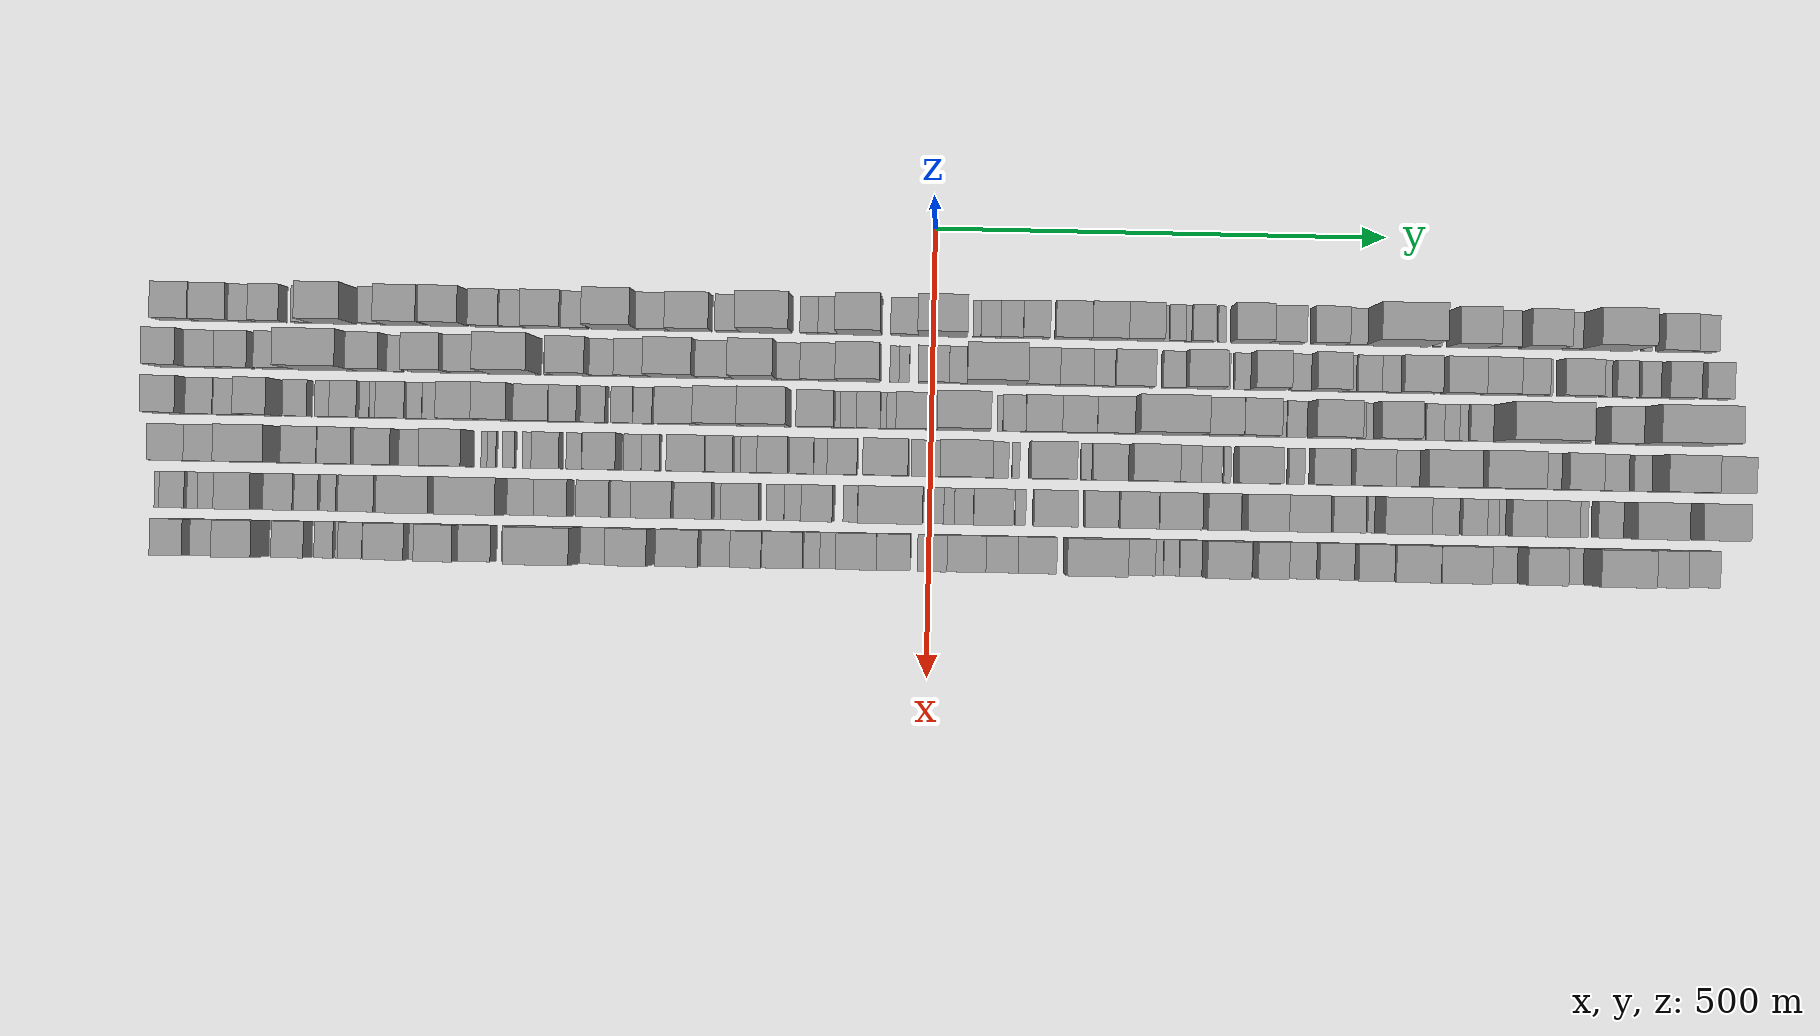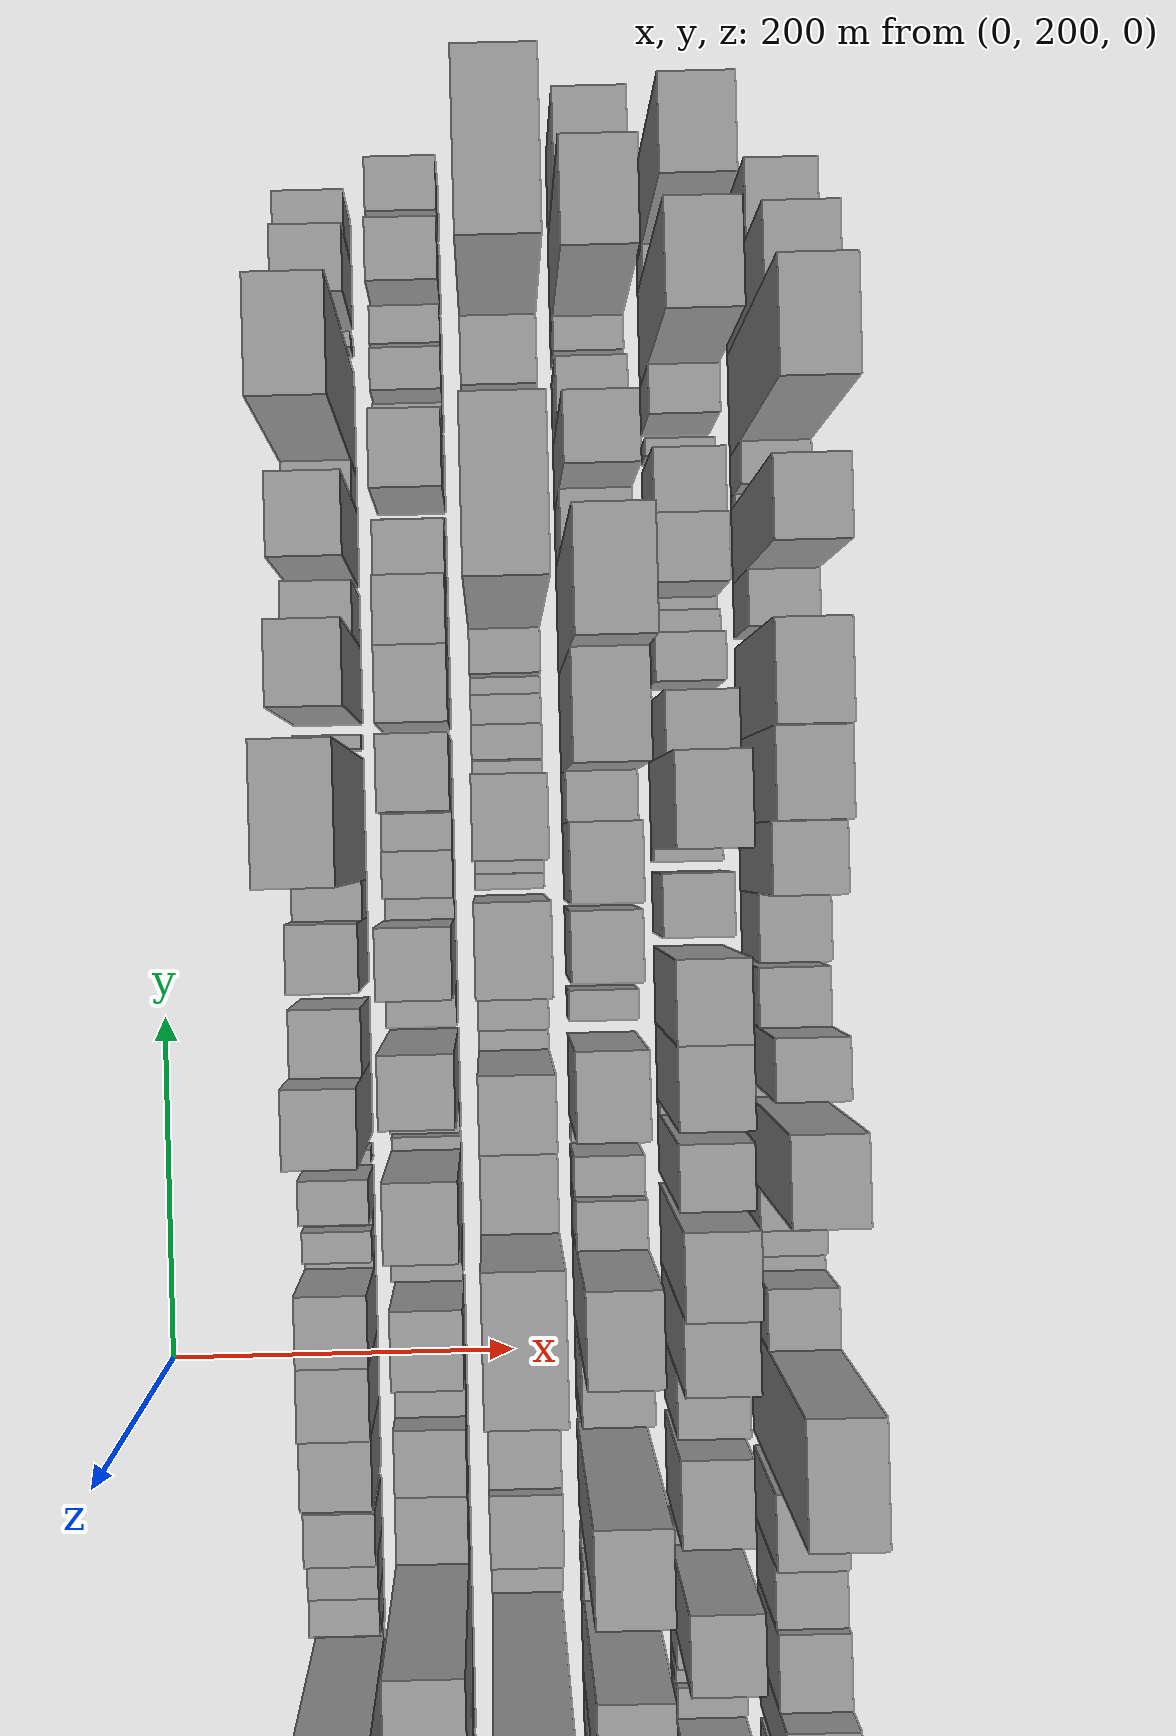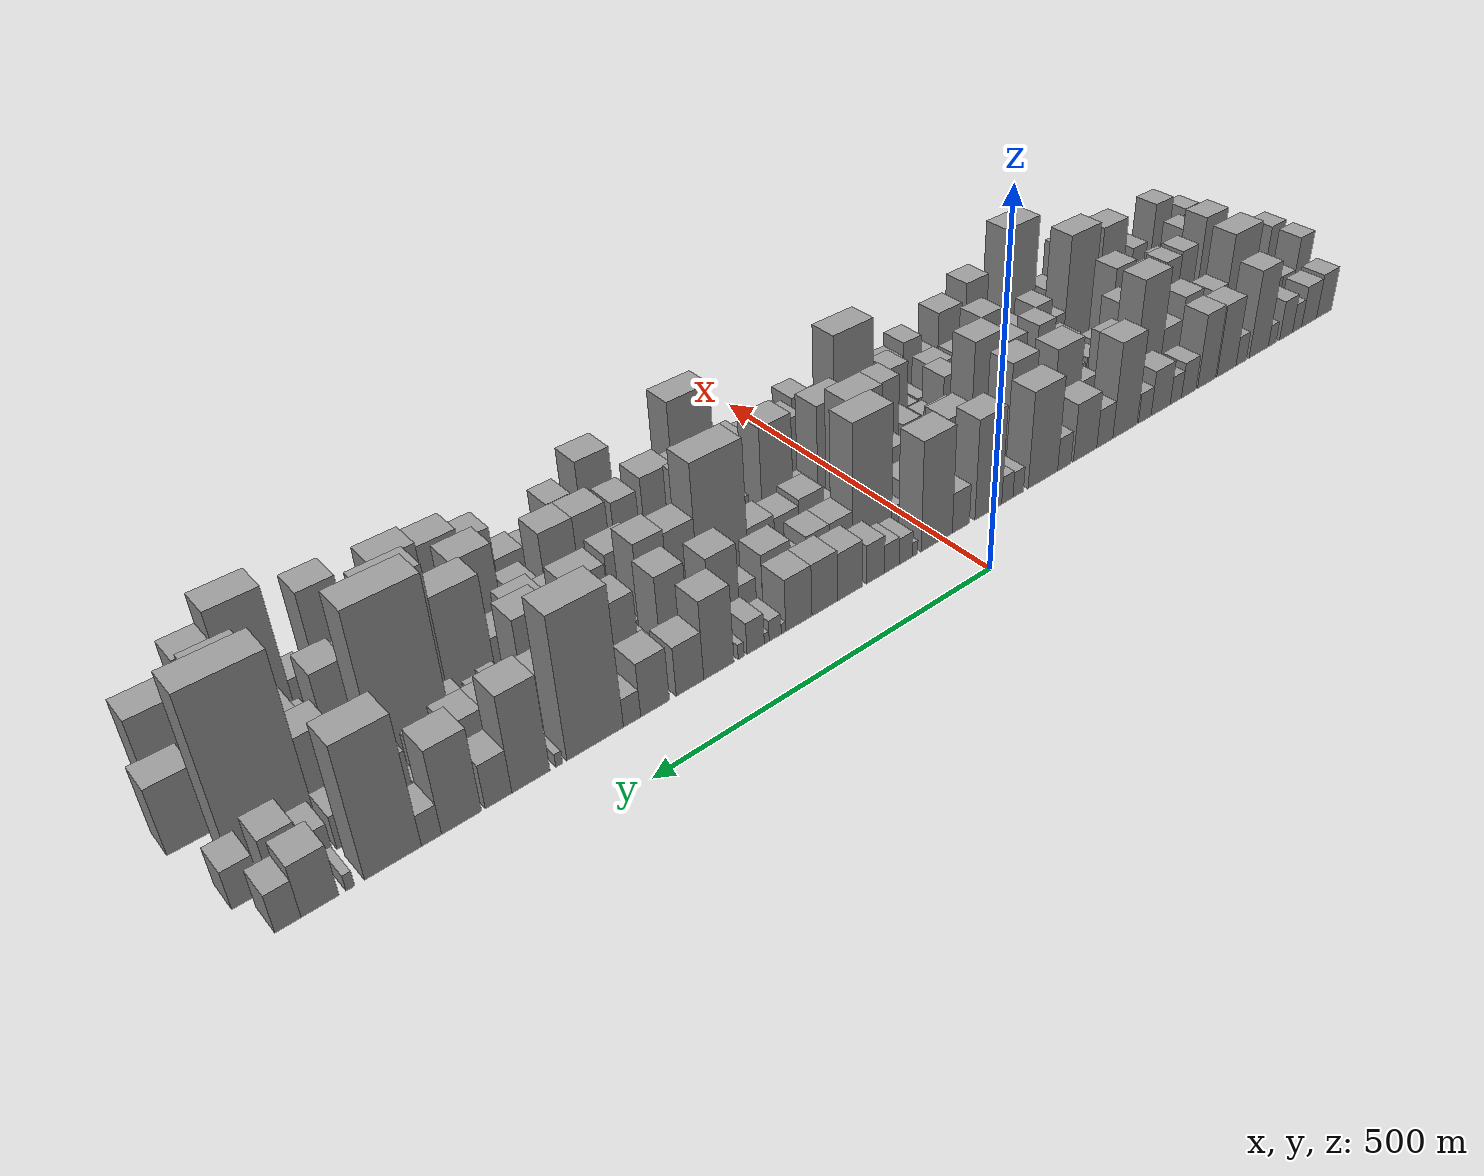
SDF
<sdf version="1.6">
 <world name="default">
  <scene>
   <sky><clouds><speed>12</speed></clouds></sky>
   <ambient>0.4 0.4 0.4 1</ambient>
   <background>0.7 0.7 0.7 1</background>
   <shadows>1</shadows>
  </scene>
  <gravity>0 0 -9.8066</gravity>
  <magnetic_field>6e-06 2.3e-05 -4.2e-05</magnetic_field>
  <physics default="0" name="default_physics" type="ode">
   <ode>
    <solver>
     <type>quick</type>
     <iters>10</iters>
     <sor>1.0</sor>
     <use_dynamic_moi_rescaling>0</use_dynamic_moi_rescaling>
    </solver>
    <constraints>
     <cfm>0</cfm>
     <erp>0.2</erp>
     <contact_max_correcting_vel>100</contact_max_correcting_vel>
     <contact_surface_layer>0.001</contact_surface_layer>
    </constraints>
   </ode>
   <max_step_size>0.004</max_step_size>
   <real_time_factor>1</real_time_factor>
   <real_time_update_rate>250</real_time_update_rate>
  </physics>
  <light name="sun" type="directional">
   <pose>0 0 10 0 0 0</pose>
   <diffuse>0.8 0.8 0.8 1</diffuse>
   <specular>0.2 0.2 0.2 1</specular>
   <attenuation>
    <range>1000</range>
    <constant>0.9</constant>
    <linear>0.01</linear>
    <quadratic>0.001</quadratic>
   </attenuation>
   <direction>-0.5 0.1 -0.9</direction>
  </light>
  <model name="building_1">
   <static>1</static>
   <pose>100.0000 -839.2656 0 0.000000 0.000000 0.000000</pose>
   <link name="link">
    <pose>0 0 37.50 0 0 0</pose>
    <collision name="collision"><geometry><box><size>40.0000 41.4688 75.0000</size></box></geometry></collision>
    <visual name="visual">
     <cast_shadows>0</cast_shadows>
     <geometry><box><size>40.0000 41.4688 75.0000</size></box></geometry>
     <material>
      <script>
       <uri>model://grey_wall/materials/scripts</uri>
       <uri>model://grey_wall/materials/textures</uri>
       <name>vrc/grey_wall</name>
      </script>
     </material>
    </visual>
   </link>
  </model>
  <model name="building_2">
   <static>1</static>
   <pose>100.0000 -798.3880 0 0.000000 0.000000 0.000000</pose>
   <link name="link">
    <pose>0 0 34.50 0 0 0</pose>
    <collision name="collision"><geometry><box><size>40.0000 40.2863 69.0000</size></box></geometry></collision>
    <visual name="visual">
     <cast_shadows>0</cast_shadows>
     <geometry><box><size>40.0000 40.2863 69.0000</size></box></geometry>
     <material>
      <script>
       <uri>model://grey_wall/materials/scripts</uri>
       <uri>model://grey_wall/materials/textures</uri>
       <name>vrc/grey_wall</name>
      </script>
     </material>
    </visual>
   </link>
  </model>
  <model name="building_3">
   <static>1</static>
   <pose>100.0000 -766.1409 0 0.000000 0.000000 0.000000</pose>
   <link name="link">
    <pose>0 0 24.00 0 0 0</pose>
    <collision name="collision"><geometry><box><size>40.0000 24.2079 48.0000</size></box></geometry></collision>
    <visual name="visual">
     <cast_shadows>0</cast_shadows>
     <geometry><box><size>40.0000 24.2079 48.0000</size></box></geometry>
     <material>
      <script>
       <uri>model://grey_wall/materials/scripts</uri>
       <uri>model://grey_wall/materials/textures</uri>
       <name>vrc/grey_wall</name>
      </script>
     </material>
    </visual>
   </link>
  </model>
  <model name="building_4">
   <static>1</static>
   <pose>100.0000 -737.0001 0 0.000000 0.000000 0.000000</pose>
   <link name="link">
    <pose>0 0 33.00 0 0 0</pose>
    <collision name="collision"><geometry><box><size>40.0000 34.0739 66.0000</size></box></geometry></collision>
    <visual name="visual">
     <cast_shadows>0</cast_shadows>
     <geometry><box><size>40.0000 34.0739 66.0000</size></box></geometry>
     <material>
      <script>
       <uri>model://grey_wall/materials/scripts</uri>
       <uri>model://grey_wall/materials/textures</uri>
       <name>vrc/grey_wall</name>
      </script>
     </material>
    </visual>
   </link>
  </model>
  <model name="building_5">
   <static>1</static>
   <pose>100.0000 -701.0439 0 0.000000 0.000000 0.000000</pose>
   <link name="link">
    <pose>0 0 18.00 0 0 0</pose>
    <collision name="collision"><geometry><box><size>40.0000 19.8385 36.0000</size></box></geometry></collision>
    <visual name="visual">
     <cast_shadows>0</cast_shadows>
     <geometry><box><size>40.0000 19.8385 36.0000</size></box></geometry>
     <material>
      <script>
       <uri>model://grey_wall/materials/scripts</uri>
       <uri>model://grey_wall/materials/textures</uri>
       <name>vrc/grey_wall</name>
      </script>
     </material>
    </visual>
   </link>
  </model>
  <model name="building_6">
   <static>1</static>
   <pose>100.0000 -666.7250 0 0.000000 0.000000 0.000000</pose>
   <link name="link">
    <pose>0 0 72.00 0 0 0</pose>
    <collision name="collision"><geometry><box><size>40.0000 48.7993 144.0000</size></box></geometry></collision>
    <visual name="visual">
     <cast_shadows>0</cast_shadows>
     <geometry><box><size>40.0000 48.7993 144.0000</size></box></geometry>
     <material>
      <script>
       <uri>model://grey_wall/materials/scripts</uri>
       <uri>model://grey_wall/materials/textures</uri>
       <name>vrc/grey_wall</name>
      </script>
     </material>
    </visual>
   </link>
  </model>
  <model name="building_7">
   <static>1</static>
   <pose>100.0000 -622.5861 0 0.000000 0.000000 0.000000</pose>
   <link name="link">
    <pose>0 0 24.00 0 0 0</pose>
    <collision name="collision"><geometry><box><size>40.0000 25.4784 48.0000</size></box></geometry></collision>
    <visual name="visual">
     <cast_shadows>0</cast_shadows>
     <geometry><box><size>40.0000 25.4784 48.0000</size></box></geometry>
     <material>
      <script>
       <uri>model://grey_wall/materials/scripts</uri>
       <uri>model://grey_wall/materials/textures</uri>
       <name>vrc/grey_wall</name>
      </script>
     </material>
    </visual>
   </link>
  </model>
  <model name="building_8">
   <static>1</static>
   <pose>100.0000 -586.5119 0 0.000000 0.000000 0.000000</pose>
   <link name="link">
    <pose>0 0 58.50 0 0 0</pose>
    <collision name="collision"><geometry><box><size>40.0000 46.6699 117.0000</size></box></geometry></collision>
    <visual name="visual">
     <cast_shadows>0</cast_shadows>
     <geometry><box><size>40.0000 46.6699 117.0000</size></box></geometry>
     <material>
      <script>
       <uri>model://grey_wall/materials/scripts</uri>
       <uri>model://grey_wall/materials/textures</uri>
       <name>vrc/grey_wall</name>
      </script>
     </material>
    </visual>
   </link>
  </model>
  <model name="building_9">
   <static>1</static>
   <pose>100.0000 -538.8416 0 0.000000 0.000000 0.000000</pose>
   <link name="link">
    <pose>0 0 60.00 0 0 0</pose>
    <collision name="collision"><geometry><box><size>40.0000 42.6708 120.0000</size></box></geometry></collision>
    <visual name="visual">
     <cast_shadows>0</cast_shadows>
     <geometry><box><size>40.0000 42.6708 120.0000</size></box></geometry>
     <material>
      <script>
       <uri>model://grey_wall/materials/scripts</uri>
       <uri>model://grey_wall/materials/textures</uri>
       <name>vrc/grey_wall</name>
      </script>
     </material>
    </visual>
   </link>
  </model>
  <model name="building_10">
   <static>1</static>
   <pose>100.0000 -496.7508 0 0.000000 0.000000 0.000000</pose>
   <link name="link">
    <pose>0 0 28.50 0 0 0</pose>
    <collision name="collision"><geometry><box><size>40.0000 33.5108 57.0000</size></box></geometry></collision>
    <visual name="visual">
     <cast_shadows>0</cast_shadows>
     <geometry><box><size>40.0000 33.5108 57.0000</size></box></geometry>
     <material>
      <script>
       <uri>model://grey_wall/materials/scripts</uri>
       <uri>model://grey_wall/materials/textures</uri>
       <name>vrc/grey_wall</name>
      </script>
     </material>
    </visual>
   </link>
  </model>
  <model name="building_11">
   <static>1</static>
   <pose>100.0000 -467.1961 0 0.000000 0.000000 0.000000</pose>
   <link name="link">
    <pose>0 0 22.50 0 0 0</pose>
    <collision name="collision"><geometry><box><size>40.0000 25.5986 45.0000</size></box></geometry></collision>
    <visual name="visual">
     <cast_shadows>0</cast_shadows>
     <geometry><box><size>40.0000 25.5986 45.0000</size></box></geometry>
     <material>
      <script>
       <uri>model://grey_wall/materials/scripts</uri>
       <uri>model://grey_wall/materials/textures</uri>
       <name>vrc/grey_wall</name>
      </script>
     </material>
    </visual>
   </link>
  </model>
  <model name="building_12">
   <static>1</static>
   <pose>100.0000 -432.8682 0 0.000000 0.000000 0.000000</pose>
   <link name="link">
    <pose>0 0 36.00 0 0 0</pose>
    <collision name="collision"><geometry><box><size>40.0000 43.0573 72.0000</size></box></geometry></collision>
    <visual name="visual">
     <cast_shadows>0</cast_shadows>
     <geometry><box><size>40.0000 43.0573 72.0000</size></box></geometry>
     <material>
      <script>
       <uri>model://grey_wall/materials/scripts</uri>
       <uri>model://grey_wall/materials/textures</uri>
       <name>vrc/grey_wall</name>
      </script>
     </material>
    </visual>
   </link>
  </model>
  <model name="building_13">
   <static>1</static>
   <pose>100.0000 -397.3391 0 0.000000 0.000000 0.000000</pose>
   <link name="link">
    <pose>0 0 24.00 0 0 0</pose>
    <collision name="collision"><geometry><box><size>40.0000 28.0010 48.0000</size></box></geometry></collision>
    <visual name="visual">
     <cast_shadows>0</cast_shadows>
     <geometry><box><size>40.0000 28.0010 48.0000</size></box></geometry>
     <material>
      <script>
       <uri>model://grey_wall/materials/scripts</uri>
       <uri>model://grey_wall/materials/textures</uri>
       <name>vrc/grey_wall</name>
      </script>
     </material>
    </visual>
   </link>
  </model>
  <model name="building_14">
   <static>1</static>
   <pose>100.0000 -354.3156 0 0.000000 0.000000 0.000000</pose>
   <link name="link">
    <pose>0 0 75.00 0 0 0</pose>
    <collision name="collision"><geometry><box><size>40.0000 52.0459 150.0000</size></box></geometry></collision>
    <visual name="visual">
     <cast_shadows>0</cast_shadows>
     <geometry><box><size>40.0000 52.0459 150.0000</size></box></geometry>
     <material>
      <script>
       <uri>model://grey_wall/materials/scripts</uri>
       <uri>model://grey_wall/materials/textures</uri>
       <name>vrc/grey_wall</name>
      </script>
     </material>
    </visual>
   </link>
  </model>
  <model name="building_15">
   <static>1</static>
   <pose>100.0000 -311.5082 0 0.000000 0.000000 0.000000</pose>
   <link name="link">
    <pose>0 0 30.00 0 0 0</pose>
    <collision name="collision"><geometry><box><size>40.0000 33.5690 60.0000</size></box></geometry></collision>
    <visual name="visual">
     <cast_shadows>0</cast_shadows>
     <geometry><box><size>40.0000 33.5690 60.0000</size></box></geometry>
     <material>
      <script>
       <uri>model://grey_wall/materials/scripts</uri>
       <uri>model://grey_wall/materials/textures</uri>
       <name>vrc/grey_wall</name>
      </script>
     </material>
    </visual>
   </link>
  </model>
  <model name="building_16">
   <static>1</static>
   <pose>100.0000 -270.7139 0 0.000000 0.000000 0.000000</pose>
   <link name="link">
    <pose>0 0 45.00 0 0 0</pose>
    <collision name="collision"><geometry><box><size>40.0000 48.0197 90.0000</size></box></geometry></collision>
    <visual name="visual">
     <cast_shadows>0</cast_shadows>
     <geometry><box><size>40.0000 48.0197 90.0000</size></box></geometry>
     <material>
      <script>
       <uri>model://grey_wall/materials/scripts</uri>
       <uri>model://grey_wall/materials/textures</uri>
       <name>vrc/grey_wall</name>
      </script>
     </material>
    </visual>
   </link>
  </model>
  <model name="building_17">
   <static>1</static>
   <pose>100.0000 -228.3283 0 0.000000 0.000000 0.000000</pose>
   <link name="link">
    <pose>0 0 25.50 0 0 0</pose>
    <collision name="collision"><geometry><box><size>40.0000 26.7515 51.0000</size></box></geometry></collision>
    <visual name="visual">
     <cast_shadows>0</cast_shadows>
     <geometry><box><size>40.0000 26.7515 51.0000</size></box></geometry>
     <material>
      <script>
       <uri>model://grey_wall/materials/scripts</uri>
       <uri>model://grey_wall/materials/textures</uri>
       <name>vrc/grey_wall</name>
      </script>
     </material>
    </visual>
   </link>
  </model>
  <model name="building_18">
   <static>1</static>
   <pose>100.0000 -186.0432 0 0.000000 0.000000 0.000000</pose>
   <link name="link">
    <pose>0 0 73.50 0 0 0</pose>
    <collision name="collision"><geometry><box><size>40.0000 57.8186 147.0000</size></box></geometry></collision>
    <visual name="visual">
     <cast_shadows>0</cast_shadows>
     <geometry><box><size>40.0000 57.8186 147.0000</size></box></geometry>
     <material>
      <script>
       <uri>model://grey_wall/materials/scripts</uri>
       <uri>model://grey_wall/materials/textures</uri>
       <name>vrc/grey_wall</name>
      </script>
     </material>
    </visual>
   </link>
  </model>
  <model name="building_19">
   <static>1</static>
   <pose>100.0000 -138.1578 0 0.000000 0.000000 0.000000</pose>
   <link name="link">
    <pose>0 0 19.50 0 0 0</pose>
    <collision name="collision"><geometry><box><size>40.0000 19.9521 39.0000</size></box></geometry></collision>
    <visual name="visual">
     <cast_shadows>0</cast_shadows>
     <geometry><box><size>40.0000 19.9521 39.0000</size></box></geometry>
     <material>
      <script>
       <uri>model://grey_wall/materials/scripts</uri>
       <uri>model://grey_wall/materials/textures</uri>
       <name>vrc/grey_wall</name>
      </script>
     </material>
    </visual>
   </link>
  </model>
  <model name="building_20">
   <static>1</static>
   <pose>100.0000 -117.5496 0 0.000000 0.000000 0.000000</pose>
   <link name="link">
    <pose>0 0 21.00 0 0 0</pose>
    <collision name="collision"><geometry><box><size>40.0000 21.2644 42.0000</size></box></geometry></collision>
    <visual name="visual">
     <cast_shadows>0</cast_shadows>
     <geometry><box><size>40.0000 21.2644 42.0000</size></box></geometry>
     <material>
      <script>
       <uri>model://grey_wall/materials/scripts</uri>
       <uri>model://grey_wall/materials/textures</uri>
       <name>vrc/grey_wall</name>
      </script>
     </material>
    </visual>
   </link>
  </model>
  <model name="building_21">
   <static>1</static>
   <pose>100.0000 -82.2609 0 0.000000 0.000000 0.000000</pose>
   <link name="link">
    <pose>0 0 75.00 0 0 0</pose>
    <collision name="collision"><geometry><box><size>40.0000 49.3131 150.0000</size></box></geometry></collision>
    <visual name="visual">
     <cast_shadows>0</cast_shadows>
     <geometry><box><size>40.0000 49.3131 150.0000</size></box></geometry>
     <material>
      <script>
       <uri>model://grey_wall/materials/scripts</uri>
       <uri>model://grey_wall/materials/textures</uri>
       <name>vrc/grey_wall</name>
      </script>
     </material>
    </visual>
   </link>
  </model>
  <model name="building_22">
   <static>1</static>
   <pose>100.0000 -32.2844 0 0.000000 0.000000 0.000000</pose>
   <link name="link">
    <pose>0 0 30.00 0 0 0</pose>
    <collision name="collision"><geometry><box><size>40.0000 30.6397 60.0000</size></box></geometry></collision>
    <visual name="visual">
     <cast_shadows>0</cast_shadows>
     <geometry><box><size>40.0000 30.6397 60.0000</size></box></geometry>
     <material>
      <script>
       <uri>model://grey_wall/materials/scripts</uri>
       <uri>model://grey_wall/materials/textures</uri>
       <name>vrc/grey_wall</name>
      </script>
     </material>
    </visual>
   </link>
  </model>
  <model name="building_23">
   <static>1</static>
   <pose>100.0000 10.1463 0 0.000000 0.000000 0.000000</pose>
   <link name="link">
    <pose>0 0 81.00 0 0 0</pose>
    <collision name="collision"><geometry><box><size>40.0000 54.2218 162.0000</size></box></geometry></collision>
    <visual name="visual">
     <cast_shadows>0</cast_shadows>
     <geometry><box><size>40.0000 54.2218 162.0000</size></box></geometry>
     <material>
      <script>
       <uri>model://grey_wall/materials/scripts</uri>
       <uri>model://grey_wall/materials/textures</uri>
       <name>vrc/grey_wall</name>
      </script>
     </material>
    </visual>
   </link>
  </model>
  <model name="building_24">
   <static>1</static>
   <pose>100.0000 47.6201 0 0.000000 0.000000 0.000000</pose>
   <link name="link">
    <pose>0 0 10.50 0 0 0</pose>
    <collision name="collision"><geometry><box><size>40.0000 8.7258 21.0000</size></box></geometry></collision>
    <visual name="visual">
     <cast_shadows>0</cast_shadows>
     <geometry><box><size>40.0000 8.7258 21.0000</size></box></geometry>
     <material>
      <script>
       <uri>model://grey_wall/materials/scripts</uri>
       <uri>model://grey_wall/materials/textures</uri>
       <name>vrc/grey_wall</name>
      </script>
     </material>
    </visual>
   </link>
  </model>
  <model name="building_25">
   <static>1</static>
   <pose>100.0000 63.0984 0 0.000000 0.000000 0.000000</pose>
   <link name="link">
    <pose>0 0 19.50 0 0 0</pose>
    <collision name="collision"><geometry><box><size>40.0000 22.2308 39.0000</size></box></geometry></collision>
    <visual name="visual">
     <cast_shadows>0</cast_shadows>
     <geometry><box><size>40.0000 22.2308 39.0000</size></box></geometry>
     <material>
      <script>
       <uri>model://grey_wall/materials/scripts</uri>
       <uri>model://grey_wall/materials/textures</uri>
       <name>vrc/grey_wall</name>
      </script>
     </material>
    </visual>
   </link>
  </model>
  <model name="building_26">
   <static>1</static>
   <pose>100.0000 86.5274 0 0.000000 0.000000 0.000000</pose>
   <link name="link">
    <pose>0 0 21.00 0 0 0</pose>
    <collision name="collision"><geometry><box><size>40.0000 24.6271 42.0000</size></box></geometry></collision>
    <visual name="visual">
     <cast_shadows>0</cast_shadows>
     <geometry><box><size>40.0000 24.6271 42.0000</size></box></geometry>
     <material>
      <script>
       <uri>model://grey_wall/materials/scripts</uri>
       <uri>model://grey_wall/materials/textures</uri>
       <name>vrc/grey_wall</name>
      </script>
     </material>
    </visual>
   </link>
  </model>
  <model name="building_27">
   <static>1</static>
   <pose>100.0000 113.6051 0 0.000000 0.000000 0.000000</pose>
   <link name="link">
    <pose>0 0 28.50 0 0 0</pose>
    <collision name="collision"><geometry><box><size>40.0000 29.5284 57.0000</size></box></geometry></collision>
    <visual name="visual">
     <cast_shadows>0</cast_shadows>
     <geometry><box><size>40.0000 29.5284 57.0000</size></box></geometry>
     <material>
      <script>
       <uri>model://grey_wall/materials/scripts</uri>
       <uri>model://grey_wall/materials/textures</uri>
       <name>vrc/grey_wall</name>
      </script>
     </material>
    </visual>
   </link>
  </model>
  <model name="building_28">
   <static>1</static>
   <pose>100.0000 154.4990 0 0.000000 0.000000 0.000000</pose>
   <link name="link">
    <pose>0 0 34.50 0 0 0</pose>
    <collision name="collision"><geometry><box><size>40.0000 40.2594 69.0000</size></box></geometry></collision>
    <visual name="visual">
     <cast_shadows>0</cast_shadows>
     <geometry><box><size>40.0000 40.2594 69.0000</size></box></geometry>
     <material>
      <script>
       <uri>model://grey_wall/materials/scripts</uri>
       <uri>model://grey_wall/materials/textures</uri>
       <name>vrc/grey_wall</name>
      </script>
     </material>
    </visual>
   </link>
  </model>
  <model name="building_29">
   <static>1</static>
   <pose>100.0000 194.5269 0 0.000000 0.000000 0.000000</pose>
   <link name="link">
    <pose>0 0 37.50 0 0 0</pose>
    <collision name="collision"><geometry><box><size>40.0000 39.7964 75.0000</size></box></geometry></collision>
    <visual name="visual">
     <cast_shadows>0</cast_shadows>
     <geometry><box><size>40.0000 39.7964 75.0000</size></box></geometry>
     <material>
      <script>
       <uri>model://grey_wall/materials/scripts</uri>
       <uri>model://grey_wall/materials/textures</uri>
       <name>vrc/grey_wall</name>
      </script>
     </material>
    </visual>
   </link>
  </model>
  <model name="building_30">
   <static>1</static>
   <pose>100.0000 234.2589 0 0.000000 0.000000 0.000000</pose>
   <link name="link">
    <pose>0 0 37.50 0 0 0</pose>
    <collision name="collision"><geometry><box><size>40.0000 39.6676 75.0000</size></box></geometry></collision>
    <visual name="visual">
     <cast_shadows>0</cast_shadows>
     <geometry><box><size>40.0000 39.6676 75.0000</size></box></geometry>
     <material>
      <script>
       <uri>model://grey_wall/materials/scripts</uri>
       <uri>model://grey_wall/materials/textures</uri>
       <name>vrc/grey_wall</name>
      </script>
     </material>
    </visual>
   </link>
  </model>
  <model name="building_31">
   <static>1</static>
   <pose>100.0000 257.5255 0 0.000000 0.000000 0.000000</pose>
   <link name="link">
    <pose>0 0 7.50 0 0 0</pose>
    <collision name="collision"><geometry><box><size>40.0000 6.8656 15.0000</size></box></geometry></collision>
    <visual name="visual">
     <cast_shadows>0</cast_shadows>
     <geometry><box><size>40.0000 6.8656 15.0000</size></box></geometry>
     <material>
      <script>
       <uri>model://grey_wall/materials/scripts</uri>
       <uri>model://grey_wall/materials/textures</uri>
       <name>vrc/grey_wall</name>
      </script>
     </material>
    </visual>
   </link>
  </model>
  <model name="building_32">
   <static>1</static>
   <pose>100.0000 269.8523 0 0.000000 0.000000 0.000000</pose>
   <link name="link">
    <pose>0 0 15.00 0 0 0</pose>
    <collision name="collision"><geometry><box><size>40.0000 17.7881 30.0000</size></box></geometry></collision>
    <visual name="visual">
     <cast_shadows>0</cast_shadows>
     <geometry><box><size>40.0000 17.7881 30.0000</size></box></geometry>
     <material>
      <script>
       <uri>model://grey_wall/materials/scripts</uri>
       <uri>model://grey_wall/materials/textures</uri>
       <name>vrc/grey_wall</name>
      </script>
     </material>
    </visual>
   </link>
  </model>
  <model name="building_33">
   <static>1</static>
   <pose>100.0000 282.3357 0 0.000000 0.000000 0.000000</pose>
   <link name="link">
    <pose>0 0 7.50 0 0 0</pose>
    <collision name="collision"><geometry><box><size>40.0000 7.1787 15.0000</size></box></geometry></collision>
    <visual name="visual">
     <cast_shadows>0</cast_shadows>
     <geometry><box><size>40.0000 7.1787 15.0000</size></box></geometry>
     <material>
      <script>
       <uri>model://grey_wall/materials/scripts</uri>
       <uri>model://grey_wall/materials/textures</uri>
       <name>vrc/grey_wall</name>
      </script>
     </material>
    </visual>
   </link>
  </model>
  <model name="building_34">
   <static>1</static>
   <pose>100.0000 298.5091 0 0.000000 0.000000 0.000000</pose>
   <link name="link">
    <pose>0 0 22.50 0 0 0</pose>
    <collision name="collision"><geometry><box><size>40.0000 25.1681 45.0000</size></box></geometry></collision>
    <visual name="visual">
     <cast_shadows>0</cast_shadows>
     <geometry><box><size>40.0000 25.1681 45.0000</size></box></geometry>
     <material>
      <script>
       <uri>model://grey_wall/materials/scripts</uri>
       <uri>model://grey_wall/materials/textures</uri>
       <name>vrc/grey_wall</name>
      </script>
     </material>
    </visual>
   </link>
  </model>
  <model name="building_35">
   <static>1</static>
   <pose>100.0000 319.3938 0 0.000000 0.000000 0.000000</pose>
   <link name="link">
    <pose>0 0 10.50 0 0 0</pose>
    <collision name="collision"><geometry><box><size>40.0000 8.6014 21.0000</size></box></geometry></collision>
    <visual name="visual">
     <cast_shadows>0</cast_shadows>
     <geometry><box><size>40.0000 8.6014 21.0000</size></box></geometry>
     <material>
      <script>
       <uri>model://grey_wall/materials/scripts</uri>
       <uri>model://grey_wall/materials/textures</uri>
       <name>vrc/grey_wall</name>
      </script>
     </material>
    </visual>
   </link>
  </model>
  <model name="building_36">
   <static>1</static>
   <pose>100.0000 350.8763 0 0.000000 0.000000 0.000000</pose>
   <link name="link">
    <pose>0 0 55.50 0 0 0</pose>
    <collision name="collision"><geometry><box><size>40.0000 42.3636 111.0000</size></box></geometry></collision>
    <visual name="visual">
     <cast_shadows>0</cast_shadows>
     <geometry><box><size>40.0000 42.3636 111.0000</size></box></geometry>
     <material>
      <script>
       <uri>model://grey_wall/materials/scripts</uri>
       <uri>model://grey_wall/materials/textures</uri>
       <name>vrc/grey_wall</name>
      </script>
     </material>
    </visual>
   </link>
  </model>
  <model name="building_37">
   <static>1</static>
   <pose>100.0000 390.8622 0 0.000000 0.000000 0.000000</pose>
   <link name="link">
    <pose>0 0 34.50 0 0 0</pose>
    <collision name="collision"><geometry><box><size>40.0000 37.6083 69.0000</size></box></geometry></collision>
    <visual name="visual">
     <cast_shadows>0</cast_shadows>
     <geometry><box><size>40.0000 37.6083 69.0000</size></box></geometry>
     <material>
      <script>
       <uri>model://grey_wall/materials/scripts</uri>
       <uri>model://grey_wall/materials/textures</uri>
       <name>vrc/grey_wall</name>
      </script>
     </material>
    </visual>
   </link>
  </model>
  <model name="building_38">
   <static>1</static>
   <pose>100.0000 437.6545 0 0.000000 0.000000 0.000000</pose>
   <link name="link">
    <pose>0 0 37.50 0 0 0</pose>
    <collision name="collision"><geometry><box><size>40.0000 37.9762 75.0000</size></box></geometry></collision>
    <visual name="visual">
     <cast_shadows>0</cast_shadows>
     <geometry><box><size>40.0000 37.9762 75.0000</size></box></geometry>
     <material>
      <script>
       <uri>model://grey_wall/materials/scripts</uri>
       <uri>model://grey_wall/materials/textures</uri>
       <name>vrc/grey_wall</name>
      </script>
     </material>
    </visual>
   </link>
  </model>
  <model name="building_39">
   <static>1</static>
   <pose>100.0000 467.8266 0 0.000000 0.000000 0.000000</pose>
   <link name="link">
    <pose>0 0 19.50 0 0 0</pose>
    <collision name="collision"><geometry><box><size>40.0000 22.3680 39.0000</size></box></geometry></collision>
    <visual name="visual">
     <cast_shadows>0</cast_shadows>
     <geometry><box><size>40.0000 22.3680 39.0000</size></box></geometry>
     <material>
      <script>
       <uri>model://grey_wall/materials/scripts</uri>
       <uri>model://grey_wall/materials/textures</uri>
       <name>vrc/grey_wall</name>
      </script>
     </material>
    </visual>
   </link>
  </model>
  <model name="building_40">
   <static>1</static>
   <pose>100.0000 514.5314 0 0.000000 0.000000 0.000000</pose>
   <link name="link">
    <pose>0 0 97.50 0 0 0</pose>
    <collision name="collision"><geometry><box><size>40.0000 71.0415 195.0000</size></box></geometry></collision>
    <visual name="visual">
     <cast_shadows>0</cast_shadows>
     <geometry><box><size>40.0000 71.0415 195.0000</size></box></geometry>
     <material>
      <script>
       <uri>model://grey_wall/materials/scripts</uri>
       <uri>model://grey_wall/materials/textures</uri>
       <name>vrc/grey_wall</name>
      </script>
     </material>
    </visual>
   </link>
  </model>
  <model name="building_41">
   <static>1</static>
   <pose>100.0000 559.1861 0 0.000000 0.000000 0.000000</pose>
   <link name="link">
    <pose>0 0 9.00 0 0 0</pose>
    <collision name="collision"><geometry><box><size>40.0000 8.2679 18.0000</size></box></geometry></collision>
    <visual name="visual">
     <cast_shadows>0</cast_shadows>
     <geometry><box><size>40.0000 8.2679 18.0000</size></box></geometry>
     <material>
      <script>
       <uri>model://grey_wall/materials/scripts</uri>
       <uri>model://grey_wall/materials/textures</uri>
       <name>vrc/grey_wall</name>
      </script>
     </material>
    </visual>
   </link>
  </model>
  <model name="building_42">
   <static>1</static>
   <pose>100.0000 592.8223 0 0.000000 0.000000 0.000000</pose>
   <link name="link">
    <pose>0 0 66.00 0 0 0</pose>
    <collision name="collision"><geometry><box><size>40.0000 45.0046 132.0000</size></box></geometry></collision>
    <visual name="visual">
     <cast_shadows>0</cast_shadows>
     <geometry><box><size>40.0000 45.0046 132.0000</size></box></geometry>
     <material>
      <script>
       <uri>model://grey_wall/materials/scripts</uri>
       <uri>model://grey_wall/materials/textures</uri>
       <name>vrc/grey_wall</name>
      </script>
     </material>
    </visual>
   </link>
  </model>
  <model name="building_43">
   <static>1</static>
   <pose>100.0000 630.7465 0 0.000000 0.000000 0.000000</pose>
   <link name="link">
    <pose>0 0 30.00 0 0 0</pose>
    <collision name="collision"><geometry><box><size>40.0000 30.8438 60.0000</size></box></geometry></collision>
    <visual name="visual">
     <cast_shadows>0</cast_shadows>
     <geometry><box><size>40.0000 30.8438 60.0000</size></box></geometry>
     <material>
      <script>
       <uri>model://grey_wall/materials/scripts</uri>
       <uri>model://grey_wall/materials/textures</uri>
       <name>vrc/grey_wall</name>
      </script>
     </material>
    </visual>
   </link>
  </model>
  <model name="building_44">
   <static>1</static>
   <pose>100.0000 672.4647 0 0.000000 0.000000 0.000000</pose>
   <link name="link">
    <pose>0 0 57.00 0 0 0</pose>
    <collision name="collision"><geometry><box><size>40.0000 44.5925 114.0000</size></box></geometry></collision>
    <visual name="visual">
     <cast_shadows>0</cast_shadows>
     <geometry><box><size>40.0000 44.5925 114.0000</size></box></geometry>
     <material>
      <script>
       <uri>model://grey_wall/materials/scripts</uri>
       <uri>model://grey_wall/materials/textures</uri>
       <name>vrc/grey_wall</name>
      </script>
     </material>
    </visual>
   </link>
  </model>
  <model name="building_45">
   <static>1</static>
   <pose>100.0000 705.6764 0 0.000000 0.000000 0.000000</pose>
   <link name="link">
    <pose>0 0 21.00 0 0 0</pose>
    <collision name="collision"><geometry><box><size>40.0000 21.8309 42.0000</size></box></geometry></collision>
    <visual name="visual">
     <cast_shadows>0</cast_shadows>
     <geometry><box><size>40.0000 21.8309 42.0000</size></box></geometry>
     <material>
      <script>
       <uri>model://grey_wall/materials/scripts</uri>
       <uri>model://grey_wall/materials/textures</uri>
       <name>vrc/grey_wall</name>
      </script>
     </material>
    </visual>
   </link>
  </model>
  <model name="building_46">
   <static>1</static>
   <pose>100.0000 746.6059 0 0.000000 0.000000 0.000000</pose>
   <link name="link">
    <pose>0 0 88.50 0 0 0</pose>
    <collision name="collision"><geometry><box><size>40.0000 60.0282 177.0000</size></box></geometry></collision>
    <visual name="visual">
     <cast_shadows>0</cast_shadows>
     <geometry><box><size>40.0000 60.0282 177.0000</size></box></geometry>
     <material>
      <script>
       <uri>model://grey_wall/materials/scripts</uri>
       <uri>model://grey_wall/materials/textures</uri>
       <name>vrc/grey_wall</name>
      </script>
     </material>
    </visual>
   </link>
  </model>
  <model name="building_47">
   <static>1</static>
   <pose>100.0000 791.1034 0 0.000000 0.000000 0.000000</pose>
   <link name="link">
    <pose>0 0 10.50 0 0 0</pose>
    <collision name="collision"><geometry><box><size>40.0000 8.9667 21.0000</size></box></geometry></collision>
    <visual name="visual">
     <cast_shadows>0</cast_shadows>
     <geometry><box><size>40.0000 8.9667 21.0000</size></box></geometry>
     <material>
      <script>
       <uri>model://grey_wall/materials/scripts</uri>
       <uri>model://grey_wall/materials/textures</uri>
       <name>vrc/grey_wall</name>
      </script>
     </material>
    </visual>
   </link>
  </model>
  <model name="building_48">
   <static>1</static>
   <pose>100.0000 821.3512 0 0.000000 0.000000 0.000000</pose>
   <link name="link">
    <pose>0 0 34.50 0 0 0</pose>
    <collision name="collision"><geometry><box><size>40.0000 37.5289 69.0000</size></box></geometry></collision>
    <visual name="visual">
     <cast_shadows>0</cast_shadows>
     <geometry><box><size>40.0000 37.5289 69.0000</size></box></geometry>
     <material>
      <script>
       <uri>model://grey_wall/materials/scripts</uri>
       <uri>model://grey_wall/materials/textures</uri>
       <name>vrc/grey_wall</name>
      </script>
     </material>
    </visual>
   </link>
  </model>
  <model name="building_49">
   <static>1</static>
   <pose>100.0000 852.9213 0 0.000000 0.000000 0.000000</pose>
   <link name="link">
    <pose>0 0 25.50 0 0 0</pose>
    <collision name="collision"><geometry><box><size>40.0000 25.6114 51.0000</size></box></geometry></collision>
    <visual name="visual">
     <cast_shadows>0</cast_shadows>
     <geometry><box><size>40.0000 25.6114 51.0000</size></box></geometry>
     <material>
      <script>
       <uri>model://grey_wall/materials/scripts</uri>
       <uri>model://grey_wall/materials/textures</uri>
       <name>vrc/grey_wall</name>
      </script>
     </material>
    </visual>
   </link>
  </model>
  <model name="building_50">
   <static>1</static>
   <pose>152.0000 -841.6361 0 0.000000 0.000000 0.000000</pose>
   <link name="link">
    <pose>0 0 58.50 0 0 0</pose>
    <collision name="collision"><geometry><box><size>40.0000 36.7278 117.0000</size></box></geometry></collision>
    <visual name="visual">
     <cast_shadows>0</cast_shadows>
     <geometry><box><size>40.0000 36.7278 117.0000</size></box></geometry>
     <material>
      <script>
       <uri>model://grey_wall/materials/scripts</uri>
       <uri>model://grey_wall/materials/textures</uri>
       <name>vrc/grey_wall</name>
      </script>
     </material>
    </visual>
   </link>
  </model>
  <model name="building_51">
   <static>1</static>
   <pose>152.0000 -806.7271 0 0.000000 0.000000 0.000000</pose>
   <link name="link">
    <pose>0 0 31.50 0 0 0</pose>
    <collision name="collision"><geometry><box><size>40.0000 33.0901 63.0000</size></box></geometry></collision>
    <visual name="visual">
     <cast_shadows>0</cast_shadows>
     <geometry><box><size>40.0000 33.0901 63.0000</size></box></geometry>
     <material>
      <script>
       <uri>model://grey_wall/materials/scripts</uri>
       <uri>model://grey_wall/materials/textures</uri>
       <name>vrc/grey_wall</name>
      </script>
     </material>
    </visual>
   </link>
  </model>
  <model name="building_52">
   <static>1</static>
   <pose>152.0000 -772.2572 0 0.000000 0.000000 0.000000</pose>
   <link name="link">
    <pose>0 0 31.50 0 0 0</pose>
    <collision name="collision"><geometry><box><size>40.0000 35.8498 63.0000</size></box></geometry></collision>
    <visual name="visual">
     <cast_shadows>0</cast_shadows>
     <geometry><box><size>40.0000 35.8498 63.0000</size></box></geometry>
     <material>
      <script>
       <uri>model://grey_wall/materials/scripts</uri>
       <uri>model://grey_wall/materials/textures</uri>
       <name>vrc/grey_wall</name>
      </script>
     </material>
    </visual>
   </link>
  </model>
  <model name="building_53">
   <static>1</static>
   <pose>152.0000 -726.2675 0 0.000000 0.000000 0.000000</pose>
   <link name="link">
    <pose>0 0 36.00 0 0 0</pose>
    <collision name="collision"><geometry><box><size>40.0000 38.1297 72.0000</size></box></geometry></collision>
    <visual name="visual">
     <cast_shadows>0</cast_shadows>
     <geometry><box><size>40.0000 38.1297 72.0000</size></box></geometry>
     <material>
      <script>
       <uri>model://grey_wall/materials/scripts</uri>
       <uri>model://grey_wall/materials/textures</uri>
       <name>vrc/grey_wall</name>
      </script>
     </material>
    </visual>
   </link>
  </model>
  <model name="building_54">
   <static>1</static>
   <pose>152.0000 -673.6526 0 0.000000 0.000000 0.000000</pose>
   <link name="link">
    <pose>0 0 91.50 0 0 0</pose>
    <collision name="collision"><geometry><box><size>40.0000 67.1001 183.0000</size></box></geometry></collision>
    <visual name="visual">
     <cast_shadows>0</cast_shadows>
     <geometry><box><size>40.0000 67.1001 183.0000</size></box></geometry>
     <material>
      <script>
       <uri>model://grey_wall/materials/scripts</uri>
       <uri>model://grey_wall/materials/textures</uri>
       <name>vrc/grey_wall</name>
      </script>
     </material>
    </visual>
   </link>
  </model>
  <model name="building_55">
   <static>1</static>
   <pose>152.0000 -622.2448 0 0.000000 0.000000 0.000000</pose>
   <link name="link">
    <pose>0 0 52.50 0 0 0</pose>
    <collision name="collision"><geometry><box><size>40.0000 35.7155 105.0000</size></box></geometry></collision>
    <visual name="visual">
     <cast_shadows>0</cast_shadows>
     <geometry><box><size>40.0000 35.7155 105.0000</size></box></geometry>
     <material>
      <script>
       <uri>model://grey_wall/materials/scripts</uri>
       <uri>model://grey_wall/materials/textures</uri>
       <name>vrc/grey_wall</name>
      </script>
     </material>
    </visual>
   </link>
  </model>
  <model name="building_56">
   <static>1</static>
   <pose>152.0000 -596.3310 0 0.000000 0.000000 0.000000</pose>
   <link name="link">
    <pose>0 0 15.00 0 0 0</pose>
    <collision name="collision"><geometry><box><size>40.0000 16.1122 30.0000</size></box></geometry></collision>
    <visual name="visual">
     <cast_shadows>0</cast_shadows>
     <geometry><box><size>40.0000 16.1122 30.0000</size></box></geometry>
     <material>
      <script>
       <uri>model://grey_wall/materials/scripts</uri>
       <uri>model://grey_wall/materials/textures</uri>
       <name>vrc/grey_wall</name>
      </script>
     </material>
    </visual>
   </link>
  </model>
  <model name="building_57">
   <static>1</static>
   <pose>152.0000 -557.2181 0 0.000000 0.000000 0.000000</pose>
   <link name="link">
    <pose>0 0 60.00 0 0 0</pose>
    <collision name="collision"><geometry><box><size>40.0000 42.1136 120.0000</size></box></geometry></collision>
    <visual name="visual">
     <cast_shadows>0</cast_shadows>
     <geometry><box><size>40.0000 42.1136 120.0000</size></box></geometry>
     <material>
      <script>
       <uri>model://grey_wall/materials/scripts</uri>
       <uri>model://grey_wall/materials/textures</uri>
       <name>vrc/grey_wall</name>
      </script>
     </material>
    </visual>
   </link>
  </model>
  <model name="building_58">
   <static>1</static>
   <pose>152.0000 -514.9470 0 0.000000 0.000000 0.000000</pose>
   <link name="link">
    <pose>0 0 42.00 0 0 0</pose>
    <collision name="collision"><geometry><box><size>40.0000 42.4287 84.0000</size></box></geometry></collision>
    <visual name="visual">
     <cast_shadows>0</cast_shadows>
     <geometry><box><size>40.0000 42.4287 84.0000</size></box></geometry>
     <material>
      <script>
       <uri>model://grey_wall/materials/scripts</uri>
       <uri>model://grey_wall/materials/textures</uri>
       <name>vrc/grey_wall</name>
      </script>
     </material>
    </visual>
   </link>
  </model>
  <model name="building_59">
   <static>1</static>
   <pose>152.0000 -464.6839 0 0.000000 0.000000 0.000000</pose>
   <link name="link">
    <pose>0 0 91.50 0 0 0</pose>
    <collision name="collision"><geometry><box><size>40.0000 58.0975 183.0000</size></box></geometry></collision>
    <visual name="visual">
     <cast_shadows>0</cast_shadows>
     <geometry><box><size>40.0000 58.0975 183.0000</size></box></geometry>
     <material>
      <script>
       <uri>model://grey_wall/materials/scripts</uri>
       <uri>model://grey_wall/materials/textures</uri>
       <name>vrc/grey_wall</name>
      </script>
     </material>
    </visual>
   </link>
  </model>
  <model name="building_60">
   <static>1</static>
   <pose>152.0000 -426.7891 0 0.000000 0.000000 0.000000</pose>
   <link name="link">
    <pose>0 0 10.50 0 0 0</pose>
    <collision name="collision"><geometry><box><size>40.0000 9.6920 21.0000</size></box></geometry></collision>
    <visual name="visual">
     <cast_shadows>0</cast_shadows>
     <geometry><box><size>40.0000 9.6920 21.0000</size></box></geometry>
     <material>
      <script>
       <uri>model://grey_wall/materials/scripts</uri>
       <uri>model://grey_wall/materials/textures</uri>
       <name>vrc/grey_wall</name>
      </script>
     </material>
    </visual>
   </link>
  </model>
  <model name="building_61">
   <static>1</static>
   <pose>152.0000 -400.5287 0 0.000000 0.000000 0.000000</pose>
   <link name="link">
    <pose>0 0 57.00 0 0 0</pose>
    <collision name="collision"><geometry><box><size>40.0000 42.8288 114.0000</size></box></geometry></collision>
    <visual name="visual">
     <cast_shadows>0</cast_shadows>
     <geometry><box><size>40.0000 42.8288 114.0000</size></box></geometry>
     <material>
      <script>
       <uri>model://grey_wall/materials/scripts</uri>
       <uri>model://grey_wall/materials/textures</uri>
       <name>vrc/grey_wall</name>
      </script>
     </material>
    </visual>
   </link>
  </model>
  <model name="building_62">
   <static>1</static>
   <pose>152.0000 -364.8588 0 0.000000 0.000000 0.000000</pose>
   <link name="link">
    <pose>0 0 24.00 0 0 0</pose>
    <collision name="collision"><geometry><box><size>40.0000 28.5111 48.0000</size></box></geometry></collision>
    <visual name="visual">
     <cast_shadows>0</cast_shadows>
     <geometry><box><size>40.0000 28.5111 48.0000</size></box></geometry>
     <material>
      <script>
       <uri>model://grey_wall/materials/scripts</uri>
       <uri>model://grey_wall/materials/textures</uri>
       <name>vrc/grey_wall</name>
      </script>
     </material>
    </visual>
   </link>
  </model>
  <model name="building_63">
   <static>1</static>
   <pose>152.0000 -332.0911 0 0.000000 0.000000 0.000000</pose>
   <link name="link">
    <pose>0 0 36.00 0 0 0</pose>
    <collision name="collision"><geometry><box><size>40.0000 37.0244 72.0000</size></box></geometry></collision>
    <visual name="visual">
     <cast_shadows>0</cast_shadows>
     <geometry><box><size>40.0000 37.0244 72.0000</size></box></geometry>
     <material>
      <script>
       <uri>model://grey_wall/materials/scripts</uri>
       <uri>model://grey_wall/materials/textures</uri>
       <name>vrc/grey_wall</name>
      </script>
     </material>
    </visual>
   </link>
  </model>
  <model name="building_64">
   <static>1</static>
   <pose>152.0000 -287.3211 0 0.000000 0.000000 0.000000</pose>
   <link name="link">
    <pose>0 0 72.00 0 0 0</pose>
    <collision name="collision"><geometry><box><size>40.0000 52.5156 144.0000</size></box></geometry></collision>
    <visual name="visual">
     <cast_shadows>0</cast_shadows>
     <geometry><box><size>40.0000 52.5156 144.0000</size></box></geometry>
     <material>
      <script>
       <uri>model://grey_wall/materials/scripts</uri>
       <uri>model://grey_wall/materials/textures</uri>
       <name>vrc/grey_wall</name>
      </script>
     </material>
    </visual>
   </link>
  </model>
  <model name="building_65">
   <static>1</static>
   <pose>152.0000 -241.3516 0 0.000000 0.000000 0.000000</pose>
   <link name="link">
    <pose>0 0 37.50 0 0 0</pose>
    <collision name="collision"><geometry><box><size>40.0000 39.4234 75.0000</size></box></geometry></collision>
    <visual name="visual">
     <cast_shadows>0</cast_shadows>
     <geometry><box><size>40.0000 39.4234 75.0000</size></box></geometry>
     <material>
      <script>
       <uri>model://grey_wall/materials/scripts</uri>
       <uri>model://grey_wall/materials/textures</uri>
       <name>vrc/grey_wall</name>
      </script>
     </material>
    </visual>
   </link>
  </model>
  <model name="building_66">
   <static>1</static>
   <pose>152.0000 -197.1437 0 0.000000 0.000000 0.000000</pose>
   <link name="link">
    <pose>0 0 79.50 0 0 0</pose>
    <collision name="collision"><geometry><box><size>40.0000 48.9924 159.0000</size></box></geometry></collision>
    <visual name="visual">
     <cast_shadows>0</cast_shadows>
     <geometry><box><size>40.0000 48.9924 159.0000</size></box></geometry>
     <material>
      <script>
       <uri>model://grey_wall/materials/scripts</uri>
       <uri>model://grey_wall/materials/textures</uri>
       <name>vrc/grey_wall</name>
      </script>
     </material>
    </visual>
   </link>
  </model>
  <model name="building_67">
   <static>1</static>
   <pose>152.0000 -159.3872 0 0.000000 0.000000 0.000000</pose>
   <link name="link">
    <pose>0 0 24.00 0 0 0</pose>
    <collision name="collision"><geometry><box><size>40.0000 26.5207 48.0000</size></box></geometry></collision>
    <visual name="visual">
     <cast_shadows>0</cast_shadows>
     <geometry><box><size>40.0000 26.5207 48.0000</size></box></geometry>
     <material>
      <script>
       <uri>model://grey_wall/materials/scripts</uri>
       <uri>model://grey_wall/materials/textures</uri>
       <name>vrc/grey_wall</name>
      </script>
     </material>
    </visual>
   </link>
  </model>
  <model name="building_68">
   <static>1</static>
   <pose>152.0000 -126.0976 0 0.000000 0.000000 0.000000</pose>
   <link name="link">
    <pose>0 0 34.50 0 0 0</pose>
    <collision name="collision"><geometry><box><size>40.0000 40.0585 69.0000</size></box></geometry></collision>
    <visual name="visual">
     <cast_shadows>0</cast_shadows>
     <geometry><box><size>40.0000 40.0585 69.0000</size></box></geometry>
     <material>
      <script>
       <uri>model://grey_wall/materials/scripts</uri>
       <uri>model://grey_wall/materials/textures</uri>
       <name>vrc/grey_wall</name>
      </script>
     </material>
    </visual>
   </link>
  </model>
  <model name="building_69">
   <static>1</static>
   <pose>152.0000 -82.0551 0 0.000000 0.000000 0.000000</pose>
   <link name="link">
    <pose>0 0 63.00 0 0 0</pose>
    <collision name="collision"><geometry><box><size>40.0000 48.0266 126.0000</size></box></geometry></collision>
    <visual name="visual">
     <cast_shadows>0</cast_shadows>
     <geometry><box><size>40.0000 48.0266 126.0000</size></box></geometry>
     <material>
      <script>
       <uri>model://grey_wall/materials/scripts</uri>
       <uri>model://grey_wall/materials/textures</uri>
       <name>vrc/grey_wall</name>
      </script>
     </material>
    </visual>
   </link>
  </model>
  <model name="building_70">
   <static>1</static>
   <pose>152.0000 -42.9014 0 0.000000 0.000000 0.000000</pose>
   <link name="link">
    <pose>0 0 10.50 0 0 0</pose>
    <collision name="collision"><geometry><box><size>40.0000 10.2807 21.0000</size></box></geometry></collision>
    <visual name="visual">
     <cast_shadows>0</cast_shadows>
     <geometry><box><size>40.0000 10.2807 21.0000</size></box></geometry>
     <material>
      <script>
       <uri>model://grey_wall/materials/scripts</uri>
       <uri>model://grey_wall/materials/textures</uri>
       <name>vrc/grey_wall</name>
      </script>
     </material>
    </visual>
   </link>
  </model>
  <model name="building_71">
   <static>1</static>
   <pose>152.0000 -31.9671 0 0.000000 0.000000 0.000000</pose>
   <link name="link">
    <pose>0 0 12.00 0 0 0</pose>
    <collision name="collision"><geometry><box><size>40.0000 11.5878 24.0000</size></box></geometry></collision>
    <visual name="visual">
     <cast_shadows>0</cast_shadows>
     <geometry><box><size>40.0000 11.5878 24.0000</size></box></geometry>
     <material>
      <script>
       <uri>model://grey_wall/materials/scripts</uri>
       <uri>model://grey_wall/materials/textures</uri>
       <name>vrc/grey_wall</name>
      </script>
     </material>
    </visual>
   </link>
  </model>
  <model name="building_72">
   <static>1</static>
   <pose>152.0000 0.9617 0 0.000000 0.000000 0.000000</pose>
   <link name="link">
    <pose>0 0 33.00 0 0 0</pose>
    <collision name="collision"><geometry><box><size>40.0000 34.2699 66.0000</size></box></geometry></collision>
    <visual name="visual">
     <cast_shadows>0</cast_shadows>
     <geometry><box><size>40.0000 34.2699 66.0000</size></box></geometry>
     <material>
      <script>
       <uri>model://grey_wall/materials/scripts</uri>
       <uri>model://grey_wall/materials/textures</uri>
       <name>vrc/grey_wall</name>
      </script>
     </material>
    </visual>
   </link>
  </model>
  <model name="building_73">
   <static>1</static>
   <pose>152.0000 27.9058 0 0.000000 0.000000 0.000000</pose>
   <link name="link">
    <pose>0 0 19.50 0 0 0</pose>
    <collision name="collision"><geometry><box><size>40.0000 19.6182 39.0000</size></box></geometry></collision>
    <visual name="visual">
     <cast_shadows>0</cast_shadows>
     <geometry><box><size>40.0000 19.6182 39.0000</size></box></geometry>
     <material>
      <script>
       <uri>model://grey_wall/materials/scripts</uri>
       <uri>model://grey_wall/materials/textures</uri>
       <name>vrc/grey_wall</name>
      </script>
     </material>
    </visual>
   </link>
  </model>
  <model name="building_74">
   <static>1</static>
   <pose>152.0000 70.4620 0 0.000000 0.000000 0.000000</pose>
   <link name="link">
    <pose>0 0 96.00 0 0 0</pose>
    <collision name="collision"><geometry><box><size>40.0000 65.4942 192.0000</size></box></geometry></collision>
    <visual name="visual">
     <cast_shadows>0</cast_shadows>
     <geometry><box><size>40.0000 65.4942 192.0000</size></box></geometry>
     <material>
      <script>
       <uri>model://grey_wall/materials/scripts</uri>
       <uri>model://grey_wall/materials/textures</uri>
       <name>vrc/grey_wall</name>
      </script>
     </material>
    </visual>
   </link>
  </model>
  <model name="building_75">
   <static>1</static>
   <pose>152.0000 121.6727 0 0.000000 0.000000 0.000000</pose>
   <link name="link">
    <pose>0 0 33.00 0 0 0</pose>
    <collision name="collision"><geometry><box><size>40.0000 36.9271 66.0000</size></box></geometry></collision>
    <visual name="visual">
     <cast_shadows>0</cast_shadows>
     <geometry><box><size>40.0000 36.9271 66.0000</size></box></geometry>
     <material>
      <script>
       <uri>model://grey_wall/materials/scripts</uri>
       <uri>model://grey_wall/materials/textures</uri>
       <name>vrc/grey_wall</name>
      </script>
     </material>
    </visual>
   </link>
  </model>
  <model name="building_76">
   <static>1</static>
   <pose>152.0000 158.5414 0 0.000000 0.000000 0.000000</pose>
   <link name="link">
    <pose>0 0 33.00 0 0 0</pose>
    <collision name="collision"><geometry><box><size>40.0000 36.8104 66.0000</size></box></geometry></collision>
    <visual name="visual">
     <cast_shadows>0</cast_shadows>
     <geometry><box><size>40.0000 36.8104 66.0000</size></box></geometry>
     <material>
      <script>
       <uri>model://grey_wall/materials/scripts</uri>
       <uri>model://grey_wall/materials/textures</uri>
       <name>vrc/grey_wall</name>
      </script>
     </material>
    </visual>
   </link>
  </model>
  <model name="building_77">
   <static>1</static>
   <pose>152.0000 189.0542 0 0.000000 0.000000 0.000000</pose>
   <link name="link">
    <pose>0 0 22.50 0 0 0</pose>
    <collision name="collision"><geometry><box><size>40.0000 24.2151 45.0000</size></box></geometry></collision>
    <visual name="visual">
     <cast_shadows>0</cast_shadows>
     <geometry><box><size>40.0000 24.2151 45.0000</size></box></geometry>
     <material>
      <script>
       <uri>model://grey_wall/materials/scripts</uri>
       <uri>model://grey_wall/materials/textures</uri>
       <name>vrc/grey_wall</name>
      </script>
     </material>
    </visual>
   </link>
  </model>
  <model name="building_78">
   <static>1</static>
   <pose>152.0000 223.0713 0 0.000000 0.000000 0.000000</pose>
   <link name="link">
    <pose>0 0 37.50 0 0 0</pose>
    <collision name="collision"><geometry><box><size>40.0000 43.8192 75.0000</size></box></geometry></collision>
    <visual name="visual">
     <cast_shadows>0</cast_shadows>
     <geometry><box><size>40.0000 43.8192 75.0000</size></box></geometry>
     <material>
      <script>
       <uri>model://grey_wall/materials/scripts</uri>
       <uri>model://grey_wall/materials/textures</uri>
       <name>vrc/grey_wall</name>
      </script>
     </material>
    </visual>
   </link>
  </model>
  <model name="building_79">
   <static>1</static>
   <pose>152.0000 266.4922 0 0.000000 0.000000 0.000000</pose>
   <link name="link">
    <pose>0 0 24.00 0 0 0</pose>
    <collision name="collision"><geometry><box><size>40.0000 25.0225 48.0000</size></box></geometry></collision>
    <visual name="visual">
     <cast_shadows>0</cast_shadows>
     <geometry><box><size>40.0000 25.0225 48.0000</size></box></geometry>
     <material>
      <script>
       <uri>model://grey_wall/materials/scripts</uri>
       <uri>model://grey_wall/materials/textures</uri>
       <name>vrc/grey_wall</name>
      </script>
     </material>
    </visual>
   </link>
  </model>
  <model name="building_80">
   <static>1</static>
   <pose>152.0000 300.5590 0 0.000000 0.000000 0.000000</pose>
   <link name="link">
    <pose>0 0 55.50 0 0 0</pose>
    <collision name="collision"><geometry><box><size>40.0000 43.1111 111.0000</size></box></geometry></collision>
    <visual name="visual">
     <cast_shadows>0</cast_shadows>
     <geometry><box><size>40.0000 43.1111 111.0000</size></box></geometry>
     <material>
      <script>
       <uri>model://grey_wall/materials/scripts</uri>
       <uri>model://grey_wall/materials/textures</uri>
       <name>vrc/grey_wall</name>
      </script>
     </material>
    </visual>
   </link>
  </model>
  <model name="building_81">
   <static>1</static>
   <pose>152.0000 325.9532 0 0.000000 0.000000 0.000000</pose>
   <link name="link">
    <pose>0 0 9.00 0 0 0</pose>
    <collision name="collision"><geometry><box><size>40.0000 7.6775 18.0000</size></box></geometry></collision>
    <visual name="visual">
     <cast_shadows>0</cast_shadows>
     <geometry><box><size>40.0000 7.6775 18.0000</size></box></geometry>
     <material>
      <script>
       <uri>model://grey_wall/materials/scripts</uri>
       <uri>model://grey_wall/materials/textures</uri>
       <name>vrc/grey_wall</name>
      </script>
     </material>
    </visual>
   </link>
  </model>
  <model name="building_82">
   <static>1</static>
   <pose>152.0000 342.5700 0 0.000000 0.000000 0.000000</pose>
   <link name="link">
    <pose>0 0 15.00 0 0 0</pose>
    <collision name="collision"><geometry><box><size>40.0000 17.5560 30.0000</size></box></geometry></collision>
    <visual name="visual">
     <cast_shadows>0</cast_shadows>
     <geometry><box><size>40.0000 17.5560 30.0000</size></box></geometry>
     <material>
      <script>
       <uri>model://grey_wall/materials/scripts</uri>
       <uri>model://grey_wall/materials/textures</uri>
       <name>vrc/grey_wall</name>
      </script>
     </material>
    </visual>
   </link>
  </model>
  <model name="building_83">
   <static>1</static>
   <pose>152.0000 370.8401 0 0.000000 0.000000 0.000000</pose>
   <link name="link">
    <pose>0 0 61.50 0 0 0</pose>
    <collision name="collision"><geometry><box><size>40.0000 38.9843 123.0000</size></box></geometry></collision>
    <visual name="visual">
     <cast_shadows>0</cast_shadows>
     <geometry><box><size>40.0000 38.9843 123.0000</size></box></geometry>
     <material>
      <script>
       <uri>model://grey_wall/materials/scripts</uri>
       <uri>model://grey_wall/materials/textures</uri>
       <name>vrc/grey_wall</name>
      </script>
     </material>
    </visual>
   </link>
  </model>
  <model name="building_84">
   <static>1</static>
   <pose>152.0000 406.5475 0 0.000000 0.000000 0.000000</pose>
   <link name="link">
    <pose>0 0 19.50 0 0 0</pose>
    <collision name="collision"><geometry><box><size>40.0000 22.4305 39.0000</size></box></geometry></collision>
    <visual name="visual">
     <cast_shadows>0</cast_shadows>
     <geometry><box><size>40.0000 22.4305 39.0000</size></box></geometry>
     <material>
      <script>
       <uri>model://grey_wall/materials/scripts</uri>
       <uri>model://grey_wall/materials/textures</uri>
       <name>vrc/grey_wall</name>
      </script>
     </material>
    </visual>
   </link>
  </model>
  <model name="building_85">
   <static>1</static>
   <pose>152.0000 436.7670 0 0.000000 0.000000 0.000000</pose>
   <link name="link">
    <pose>0 0 60.00 0 0 0</pose>
    <collision name="collision"><geometry><box><size>40.0000 38.0085 120.0000</size></box></geometry></collision>
    <visual name="visual">
     <cast_shadows>0</cast_shadows>
     <geometry><box><size>40.0000 38.0085 120.0000</size></box></geometry>
     <material>
      <script>
       <uri>model://grey_wall/materials/scripts</uri>
       <uri>model://grey_wall/materials/textures</uri>
       <name>vrc/grey_wall</name>
      </script>
     </material>
    </visual>
   </link>
  </model>
  <model name="building_86">
   <static>1</static>
   <pose>152.0000 462.1711 0 0.000000 0.000000 0.000000</pose>
   <link name="link">
    <pose>0 0 13.50 0 0 0</pose>
    <collision name="collision"><geometry><box><size>40.0000 12.7997 27.0000</size></box></geometry></collision>
    <visual name="visual">
     <cast_shadows>0</cast_shadows>
     <geometry><box><size>40.0000 12.7997 27.0000</size></box></geometry>
     <material>
      <script>
       <uri>model://grey_wall/materials/scripts</uri>
       <uri>model://grey_wall/materials/textures</uri>
       <name>vrc/grey_wall</name>
      </script>
     </material>
    </visual>
   </link>
  </model>
  <model name="building_87">
   <static>1</static>
   <pose>152.0000 481.8866 0 0.000000 0.000000 0.000000</pose>
   <link name="link">
    <pose>0 0 24.00 0 0 0</pose>
    <collision name="collision"><geometry><box><size>40.0000 26.6314 48.0000</size></box></geometry></collision>
    <visual name="visual">
     <cast_shadows>0</cast_shadows>
     <geometry><box><size>40.0000 26.6314 48.0000</size></box></geometry>
     <material>
      <script>
       <uri>model://grey_wall/materials/scripts</uri>
       <uri>model://grey_wall/materials/textures</uri>
       <name>vrc/grey_wall</name>
      </script>
     </material>
    </visual>
   </link>
  </model>
  <model name="building_88">
   <static>1</static>
   <pose>152.0000 505.8648 0 0.000000 0.000000 0.000000</pose>
   <link name="link">
    <pose>0 0 21.00 0 0 0</pose>
    <collision name="collision"><geometry><box><size>40.0000 21.3251 42.0000</size></box></geometry></collision>
    <visual name="visual">
     <cast_shadows>0</cast_shadows>
     <geometry><box><size>40.0000 21.3251 42.0000</size></box></geometry>
     <material>
      <script>
       <uri>model://grey_wall/materials/scripts</uri>
       <uri>model://grey_wall/materials/textures</uri>
       <name>vrc/grey_wall</name>
      </script>
     </material>
    </visual>
   </link>
  </model>
  <model name="building_89">
   <static>1</static>
   <pose>152.0000 537.9058 0 0.000000 0.000000 0.000000</pose>
   <link name="link">
    <pose>0 0 39.00 0 0 0</pose>
    <collision name="collision"><geometry><box><size>40.0000 42.7568 78.0000</size></box></geometry></collision>
    <visual name="visual">
     <cast_shadows>0</cast_shadows>
     <geometry><box><size>40.0000 42.7568 78.0000</size></box></geometry>
     <material>
      <script>
       <uri>model://grey_wall/materials/scripts</uri>
       <uri>model://grey_wall/materials/textures</uri>
       <name>vrc/grey_wall</name>
      </script>
     </material>
    </visual>
   </link>
  </model>
  <model name="building_90">
   <static>1</static>
   <pose>152.0000 586.5328 0 0.000000 0.000000 0.000000</pose>
   <link name="link">
    <pose>0 0 37.50 0 0 0</pose>
    <collision name="collision"><geometry><box><size>40.0000 42.4972 75.0000</size></box></geometry></collision>
    <visual name="visual">
     <cast_shadows>0</cast_shadows>
     <geometry><box><size>40.0000 42.4972 75.0000</size></box></geometry>
     <material>
      <script>
       <uri>model://grey_wall/materials/scripts</uri>
       <uri>model://grey_wall/materials/textures</uri>
       <name>vrc/grey_wall</name>
      </script>
     </material>
    </visual>
   </link>
  </model>
  <model name="building_91">
   <static>1</static>
   <pose>152.0000 626.8800 0 0.000000 0.000000 0.000000</pose>
   <link name="link">
    <pose>0 0 37.50 0 0 0</pose>
    <collision name="collision"><geometry><box><size>40.0000 38.1972 75.0000</size></box></geometry></collision>
    <visual name="visual">
     <cast_shadows>0</cast_shadows>
     <geometry><box><size>40.0000 38.1972 75.0000</size></box></geometry>
     <material>
      <script>
       <uri>model://grey_wall/materials/scripts</uri>
       <uri>model://grey_wall/materials/textures</uri>
       <name>vrc/grey_wall</name>
      </script>
     </material>
    </visual>
   </link>
  </model>
  <model name="building_92">
   <static>1</static>
   <pose>152.0000 662.4352 0 0.000000 0.000000 0.000000</pose>
   <link name="link">
    <pose>0 0 30.00 0 0 0</pose>
    <collision name="collision"><geometry><box><size>40.0000 32.9131 60.0000</size></box></geometry></collision>
    <visual name="visual">
     <cast_shadows>0</cast_shadows>
     <geometry><box><size>40.0000 32.9131 60.0000</size></box></geometry>
     <material>
      <script>
       <uri>model://grey_wall/materials/scripts</uri>
       <uri>model://grey_wall/materials/textures</uri>
       <name>vrc/grey_wall</name>
      </script>
     </material>
    </visual>
   </link>
  </model>
  <model name="building_93">
   <static>1</static>
   <pose>152.0000 683.1166 0 0.000000 0.000000 0.000000</pose>
   <link name="link">
    <pose>0 0 9.00 0 0 0</pose>
    <collision name="collision"><geometry><box><size>40.0000 8.4497 18.0000</size></box></geometry></collision>
    <visual name="visual">
     <cast_shadows>0</cast_shadows>
     <geometry><box><size>40.0000 8.4497 18.0000</size></box></geometry>
     <material>
      <script>
       <uri>model://grey_wall/materials/scripts</uri>
       <uri>model://grey_wall/materials/textures</uri>
       <name>vrc/grey_wall</name>
      </script>
     </material>
    </visual>
   </link>
  </model>
  <model name="building_94">
   <static>1</static>
   <pose>152.0000 714.8985 0 0.000000 0.000000 0.000000</pose>
   <link name="link">
    <pose>0 0 37.50 0 0 0</pose>
    <collision name="collision"><geometry><box><size>40.0000 43.1142 75.0000</size></box></geometry></collision>
    <visual name="visual">
     <cast_shadows>0</cast_shadows>
     <geometry><box><size>40.0000 43.1142 75.0000</size></box></geometry>
     <material>
      <script>
       <uri>model://grey_wall/materials/scripts</uri>
       <uri>model://grey_wall/materials/textures</uri>
       <name>vrc/grey_wall</name>
      </script>
     </material>
    </visual>
   </link>
  </model>
  <model name="building_95">
   <static>1</static>
   <pose>152.0000 746.1056 0 0.000000 0.000000 0.000000</pose>
   <link name="link">
    <pose>0 0 13.50 0 0 0</pose>
    <collision name="collision"><geometry><box><size>40.0000 11.3001 27.0000</size></box></geometry></collision>
    <visual name="visual">
     <cast_shadows>0</cast_shadows>
     <geometry><box><size>40.0000 11.3001 27.0000</size></box></geometry>
     <material>
      <script>
       <uri>model://grey_wall/materials/scripts</uri>
       <uri>model://grey_wall/materials/textures</uri>
       <name>vrc/grey_wall</name>
      </script>
     </material>
    </visual>
   </link>
  </model>
  <model name="building_96">
   <static>1</static>
   <pose>152.0000 766.6454 0 0.000000 0.000000 0.000000</pose>
   <link name="link">
    <pose>0 0 22.50 0 0 0</pose>
    <collision name="collision"><geometry><box><size>40.0000 23.7794 45.0000</size></box></geometry></collision>
    <visual name="visual">
     <cast_shadows>0</cast_shadows>
     <geometry><box><size>40.0000 23.7794 45.0000</size></box></geometry>
     <material>
      <script>
       <uri>model://grey_wall/materials/scripts</uri>
       <uri>model://grey_wall/materials/textures</uri>
       <name>vrc/grey_wall</name>
      </script>
     </material>
    </visual>
   </link>
  </model>
  <model name="building_97">
   <static>1</static>
   <pose>152.0000 793.3147 0 0.000000 0.000000 0.000000</pose>
   <link name="link">
    <pose>0 0 19.50 0 0 0</pose>
    <collision name="collision"><geometry><box><size>40.0000 21.5594 39.0000</size></box></geometry></collision>
    <visual name="visual">
     <cast_shadows>0</cast_shadows>
     <geometry><box><size>40.0000 21.5594 39.0000</size></box></geometry>
     <material>
      <script>
       <uri>model://grey_wall/materials/scripts</uri>
       <uri>model://grey_wall/materials/textures</uri>
       <name>vrc/grey_wall</name>
      </script>
     </material>
    </visual>
   </link>
  </model>
  <model name="building_98">
   <static>1</static>
   <pose>152.0000 827.5543 0 0.000000 0.000000 0.000000</pose>
   <link name="link">
    <pose>0 0 31.50 0 0 0</pose>
    <collision name="collision"><geometry><box><size>40.0000 34.9197 63.0000</size></box></geometry></collision>
    <visual name="visual">
     <cast_shadows>0</cast_shadows>
     <geometry><box><size>40.0000 34.9197 63.0000</size></box></geometry>
     <material>
      <script>
       <uri>model://grey_wall/materials/scripts</uri>
       <uri>model://grey_wall/materials/textures</uri>
       <name>vrc/grey_wall</name>
      </script>
     </material>
    </visual>
   </link>
  </model>
  <model name="building_99">
   <static>1</static>
   <pose>152.0000 868.2518 0 0.000000 0.000000 0.000000</pose>
   <link name="link">
    <pose>0 0 25.50 0 0 0</pose>
    <collision name="collision"><geometry><box><size>40.0000 30.4752 51.0000</size></box></geometry></collision>
    <visual name="visual">
     <cast_shadows>0</cast_shadows>
     <geometry><box><size>40.0000 30.4752 51.0000</size></box></geometry>
     <material>
      <script>
       <uri>model://grey_wall/materials/scripts</uri>
       <uri>model://grey_wall/materials/textures</uri>
       <name>vrc/grey_wall</name>
      </script>
     </material>
    </visual>
   </link>
  </model>
  <model name="building_100">
   <static>1</static>
   <pose>204.0000 -841.0967 0 0.000000 0.000000 0.000000</pose>
   <link name="link">
    <pose>0 0 58.50 0 0 0</pose>
    <collision name="collision"><geometry><box><size>40.0000 37.8066 117.0000</size></box></geometry></collision>
    <visual name="visual">
     <cast_shadows>0</cast_shadows>
     <geometry><box><size>40.0000 37.8066 117.0000</size></box></geometry>
     <material>
      <script>
       <uri>model://grey_wall/materials/scripts</uri>
       <uri>model://grey_wall/materials/textures</uri>
       <name>vrc/grey_wall</name>
      </script>
     </material>
    </visual>
   </link>
  </model>
  <model name="building_101">
   <static>1</static>
   <pose>204.0000 -807.2880 0 0.000000 0.000000 0.000000</pose>
   <link name="link">
    <pose>0 0 27.00 0 0 0</pose>
    <collision name="collision"><geometry><box><size>40.0000 29.8107 54.0000</size></box></geometry></collision>
    <visual name="visual">
     <cast_shadows>0</cast_shadows>
     <geometry><box><size>40.0000 29.8107 54.0000</size></box></geometry>
     <material>
      <script>
       <uri>model://grey_wall/materials/scripts</uri>
       <uri>model://grey_wall/materials/textures</uri>
       <name>vrc/grey_wall</name>
      </script>
     </material>
    </visual>
   </link>
  </model>
  <model name="building_102">
   <static>1</static>
   <pose>204.0000 -779.4804 0 0.000000 0.000000 0.000000</pose>
   <link name="link">
    <pose>0 0 24.00 0 0 0</pose>
    <collision name="collision"><geometry><box><size>40.0000 25.8045 48.0000</size></box></geometry></collision>
    <visual name="visual">
     <cast_shadows>0</cast_shadows>
     <geometry><box><size>40.0000 25.8045 48.0000</size></box></geometry>
     <material>
      <script>
       <uri>model://grey_wall/materials/scripts</uri>
       <uri>model://grey_wall/materials/textures</uri>
       <name>vrc/grey_wall</name>
      </script>
     </material>
    </visual>
   </link>
  </model>
  <model name="building_103">
   <static>1</static>
   <pose>204.0000 -741.5397 0 0.000000 0.000000 0.000000</pose>
   <link name="link">
    <pose>0 0 58.50 0 0 0</pose>
    <collision name="collision"><geometry><box><size>40.0000 36.0768 117.0000</size></box></geometry></collision>
    <visual name="visual">
     <cast_shadows>0</cast_shadows>
     <geometry><box><size>40.0000 36.0768 117.0000</size></box></geometry>
     <material>
      <script>
       <uri>model://grey_wall/materials/scripts</uri>
       <uri>model://grey_wall/materials/textures</uri>
       <name>vrc/grey_wall</name>
      </script>
     </material>
    </visual>
   </link>
  </model>
  <model name="building_104">
   <static>1</static>
   <pose>204.0000 -703.0891 0 0.000000 0.000000 0.000000</pose>
   <link name="link">
    <pose>0 0 22.50 0 0 0</pose>
    <collision name="collision"><geometry><box><size>40.0000 26.8244 45.0000</size></box></geometry></collision>
    <visual name="visual">
     <cast_shadows>0</cast_shadows>
     <geometry><box><size>40.0000 26.8244 45.0000</size></box></geometry>
     <material>
      <script>
       <uri>model://grey_wall/materials/scripts</uri>
       <uri>model://grey_wall/materials/textures</uri>
       <name>vrc/grey_wall</name>
      </script>
     </material>
    </visual>
   </link>
  </model>
  <model name="building_105">
   <static>1</static>
   <pose>204.0000 -673.4502 0 0.000000 0.000000 0.000000</pose>
   <link name="link">
    <pose>0 0 16.50 0 0 0</pose>
    <collision name="collision"><geometry><box><size>40.0000 18.4534 33.0000</size></box></geometry></collision>
    <visual name="visual">
     <cast_shadows>0</cast_shadows>
     <geometry><box><size>40.0000 18.4534 33.0000</size></box></geometry>
     <material>
      <script>
       <uri>model://grey_wall/materials/scripts</uri>
       <uri>model://grey_wall/materials/textures</uri>
       <name>vrc/grey_wall</name>
      </script>
     </material>
    </visual>
   </link>
  </model>
  <model name="building_106">
   <static>1</static>
   <pose>204.0000 -649.2735 0 0.000000 0.000000 0.000000</pose>
   <link name="link">
    <pose>0 0 25.50 0 0 0</pose>
    <collision name="collision"><geometry><box><size>40.0000 29.9001 51.0000</size></box></geometry></collision>
    <visual name="visual">
     <cast_shadows>0</cast_shadows>
     <geometry><box><size>40.0000 29.9001 51.0000</size></box></geometry>
     <material>
      <script>
       <uri>model://grey_wall/materials/scripts</uri>
       <uri>model://grey_wall/materials/textures</uri>
       <name>vrc/grey_wall</name>
      </script>
     </material>
    </visual>
   </link>
  </model>
  <model name="building_107">
   <static>1</static>
   <pose>204.0000 -628.8190 0 0.000000 0.000000 0.000000</pose>
   <link name="link">
    <pose>0 0 13.50 0 0 0</pose>
    <collision name="collision"><geometry><box><size>40.0000 11.0089 27.0000</size></box></geometry></collision>
    <visual name="visual">
     <cast_shadows>0</cast_shadows>
     <geometry><box><size>40.0000 11.0089 27.0000</size></box></geometry>
     <material>
      <script>
       <uri>model://grey_wall/materials/scripts</uri>
       <uri>model://grey_wall/materials/textures</uri>
       <name>vrc/grey_wall</name>
      </script>
     </material>
    </visual>
   </link>
  </model>
  <model name="building_108">
   <static>1</static>
   <pose>204.0000 -618.1951 0 0.000000 0.000000 0.000000</pose>
   <link name="link">
    <pose>0 0 12.00 0 0 0</pose>
    <collision name="collision"><geometry><box><size>40.0000 10.2389 24.0000</size></box></geometry></collision>
    <visual name="visual">
     <cast_shadows>0</cast_shadows>
     <geometry><box><size>40.0000 10.2389 24.0000</size></box></geometry>
     <material>
      <script>
       <uri>model://grey_wall/materials/scripts</uri>
       <uri>model://grey_wall/materials/textures</uri>
       <name>vrc/grey_wall</name>
      </script>
     </material>
    </visual>
   </link>
  </model>
  <model name="building_109">
   <static>1</static>
   <pose>204.0000 -597.1276 0 0.000000 0.000000 0.000000</pose>
   <link name="link">
    <pose>0 0 27.00 0 0 0</pose>
    <collision name="collision"><geometry><box><size>40.0000 31.8962 54.0000</size></box></geometry></collision>
    <visual name="visual">
     <cast_shadows>0</cast_shadows>
     <geometry><box><size>40.0000 31.8962 54.0000</size></box></geometry>
     <material>
      <script>
       <uri>model://grey_wall/materials/scripts</uri>
       <uri>model://grey_wall/materials/textures</uri>
       <name>vrc/grey_wall</name>
      </script>
     </material>
    </visual>
   </link>
  </model>
  <model name="building_110">
   <static>1</static>
   <pose>204.0000 -572.6764 0 0.000000 0.000000 0.000000</pose>
   <link name="link">
    <pose>0 0 16.50 0 0 0</pose>
    <collision name="collision"><geometry><box><size>40.0000 17.0060 33.0000</size></box></geometry></collision>
    <visual name="visual">
     <cast_shadows>0</cast_shadows>
     <geometry><box><size>40.0000 17.0060 33.0000</size></box></geometry>
     <material>
      <script>
       <uri>model://grey_wall/materials/scripts</uri>
       <uri>model://grey_wall/materials/textures</uri>
       <name>vrc/grey_wall</name>
      </script>
     </material>
    </visual>
   </link>
  </model>
  <model name="building_111">
   <static>1</static>
   <pose>204.0000 -556.3129 0 0.000000 0.000000 0.000000</pose>
   <link name="link">
    <pose>0 0 15.00 0 0 0</pose>
    <collision name="collision"><geometry><box><size>40.0000 15.7212 30.0000</size></box></geometry></collision>
    <visual name="visual">
     <cast_shadows>0</cast_shadows>
     <geometry><box><size>40.0000 15.7212 30.0000</size></box></geometry>
     <material>
      <script>
       <uri>model://grey_wall/materials/scripts</uri>
       <uri>model://grey_wall/materials/textures</uri>
       <name>vrc/grey_wall</name>
      </script>
     </material>
    </visual>
   </link>
  </model>
  <model name="building_112">
   <static>1</static>
   <pose>204.0000 -544.2446 0 0.000000 0.000000 0.000000</pose>
   <link name="link">
    <pose>0 0 9.00 0 0 0</pose>
    <collision name="collision"><geometry><box><size>40.0000 8.4153 18.0000</size></box></geometry></collision>
    <visual name="visual">
     <cast_shadows>0</cast_shadows>
     <geometry><box><size>40.0000 8.4153 18.0000</size></box></geometry>
     <material>
      <script>
       <uri>model://grey_wall/materials/scripts</uri>
       <uri>model://grey_wall/materials/textures</uri>
       <name>vrc/grey_wall</name>
      </script>
     </material>
    </visual>
   </link>
  </model>
  <model name="building_113">
   <static>1</static>
   <pose>204.0000 -520.7409 0 0.000000 0.000000 0.000000</pose>
   <link name="link">
    <pose>0 0 55.50 0 0 0</pose>
    <collision name="collision"><geometry><box><size>40.0000 38.5921 111.0000</size></box></geometry></collision>
    <visual name="visual">
     <cast_shadows>0</cast_shadows>
     <geometry><box><size>40.0000 38.5921 111.0000</size></box></geometry>
     <material>
      <script>
       <uri>model://grey_wall/materials/scripts</uri>
       <uri>model://grey_wall/materials/textures</uri>
       <name>vrc/grey_wall</name>
      </script>
     </material>
    </visual>
   </link>
  </model>
  <model name="building_114">
   <static>1</static>
   <pose>204.0000 -482.3023 0 0.000000 0.000000 0.000000</pose>
   <link name="link">
    <pose>0 0 57.00 0 0 0</pose>
    <collision name="collision"><geometry><box><size>40.0000 38.2851 114.0000</size></box></geometry></collision>
    <visual name="visual">
     <cast_shadows>0</cast_shadows>
     <geometry><box><size>40.0000 38.2851 114.0000</size></box></geometry>
     <material>
      <script>
       <uri>model://grey_wall/materials/scripts</uri>
       <uri>model://grey_wall/materials/textures</uri>
       <name>vrc/grey_wall</name>
      </script>
     </material>
    </visual>
   </link>
  </model>
  <model name="building_115">
   <static>1</static>
   <pose>204.0000 -441.0456 0 0.000000 0.000000 0.000000</pose>
   <link name="link">
    <pose>0 0 33.00 0 0 0</pose>
    <collision name="collision"><geometry><box><size>40.0000 38.2282 66.0000</size></box></geometry></collision>
    <visual name="visual">
     <cast_shadows>0</cast_shadows>
     <geometry><box><size>40.0000 38.2282 66.0000</size></box></geometry>
     <material>
      <script>
       <uri>model://grey_wall/materials/scripts</uri>
       <uri>model://grey_wall/materials/textures</uri>
       <name>vrc/grey_wall</name>
      </script>
     </material>
    </visual>
   </link>
  </model>
  <model name="building_116">
   <static>1</static>
   <pose>204.0000 -406.7556 0 0.000000 0.000000 0.000000</pose>
   <link name="link">
    <pose>0 0 28.50 0 0 0</pose>
    <collision name="collision"><geometry><box><size>40.0000 30.3517 57.0000</size></box></geometry></collision>
    <visual name="visual">
     <cast_shadows>0</cast_shadows>
     <geometry><box><size>40.0000 30.3517 57.0000</size></box></geometry>
     <material>
      <script>
       <uri>model://grey_wall/materials/scripts</uri>
       <uri>model://grey_wall/materials/textures</uri>
       <name>vrc/grey_wall</name>
      </script>
     </material>
    </visual>
   </link>
  </model>
  <model name="building_117">
   <static>1</static>
   <pose>204.0000 -373.9342 0 0.000000 0.000000 0.000000</pose>
   <link name="link">
    <pose>0 0 25.50 0 0 0</pose>
    <collision name="collision"><geometry><box><size>40.0000 27.2911 51.0000</size></box></geometry></collision>
    <visual name="visual">
     <cast_shadows>0</cast_shadows>
     <geometry><box><size>40.0000 27.2911 51.0000</size></box></geometry>
     <material>
      <script>
       <uri>model://grey_wall/materials/scripts</uri>
       <uri>model://grey_wall/materials/textures</uri>
       <name>vrc/grey_wall</name>
      </script>
     </material>
    </visual>
   </link>
  </model>
  <model name="building_118">
   <static>1</static>
   <pose>204.0000 -342.2730 0 0.000000 0.000000 0.000000</pose>
   <link name="link">
    <pose>0 0 24.00 0 0 0</pose>
    <collision name="collision"><geometry><box><size>40.0000 24.0312 48.0000</size></box></geometry></collision>
    <visual name="visual">
     <cast_shadows>0</cast_shadows>
     <geometry><box><size>40.0000 24.0312 48.0000</size></box></geometry>
     <material>
      <script>
       <uri>model://grey_wall/materials/scripts</uri>
       <uri>model://grey_wall/materials/textures</uri>
       <name>vrc/grey_wall</name>
      </script>
     </material>
    </visual>
   </link>
  </model>
  <model name="building_119">
   <static>1</static>
   <pose>204.0000 -319.8531 0 0.000000 0.000000 0.000000</pose>
   <link name="link">
    <pose>0 0 19.50 0 0 0</pose>
    <collision name="collision"><geometry><box><size>40.0000 20.8086 39.0000</size></box></geometry></collision>
    <visual name="visual">
     <cast_shadows>0</cast_shadows>
     <geometry><box><size>40.0000 20.8086 39.0000</size></box></geometry>
     <material>
      <script>
       <uri>model://grey_wall/materials/scripts</uri>
       <uri>model://grey_wall/materials/textures</uri>
       <name>vrc/grey_wall</name>
      </script>
     </material>
    </visual>
   </link>
  </model>
  <model name="building_120">
   <static>1</static>
   <pose>204.0000 -281.4233 0 0.000000 0.000000 0.000000</pose>
   <link name="link">
    <pose>0 0 40.50 0 0 0</pose>
    <collision name="collision"><geometry><box><size>40.0000 46.0510 81.0000</size></box></geometry></collision>
    <visual name="visual">
     <cast_shadows>0</cast_shadows>
     <geometry><box><size>40.0000 46.0510 81.0000</size></box></geometry>
     <material>
      <script>
       <uri>model://grey_wall/materials/scripts</uri>
       <uri>model://grey_wall/materials/textures</uri>
       <name>vrc/grey_wall</name>
      </script>
     </material>
    </visual>
   </link>
  </model>
  <model name="building_121">
   <static>1</static>
   <pose>204.0000 -234.1005 0 0.000000 0.000000 0.000000</pose>
   <link name="link">
    <pose>0 0 75.00 0 0 0</pose>
    <collision name="collision"><geometry><box><size>40.0000 48.5946 150.0000</size></box></geometry></collision>
    <visual name="visual">
     <cast_shadows>0</cast_shadows>
     <geometry><box><size>40.0000 48.5946 150.0000</size></box></geometry>
     <material>
      <script>
       <uri>model://grey_wall/materials/scripts</uri>
       <uri>model://grey_wall/materials/textures</uri>
       <name>vrc/grey_wall</name>
      </script>
     </material>
    </visual>
   </link>
  </model>
  <model name="building_122">
   <static>1</static>
   <pose>204.0000 -183.3602 0 0.000000 0.000000 0.000000</pose>
   <link name="link">
    <pose>0 0 87.00 0 0 0</pose>
    <collision name="collision"><geometry><box><size>40.0000 52.8860 174.0000</size></box></geometry></collision>
    <visual name="visual">
     <cast_shadows>0</cast_shadows>
     <geometry><box><size>40.0000 52.8860 174.0000</size></box></geometry>
     <material>
      <script>
       <uri>model://grey_wall/materials/scripts</uri>
       <uri>model://grey_wall/materials/textures</uri>
       <name>vrc/grey_wall</name>
      </script>
     </material>
    </visual>
   </link>
  </model>
  <model name="building_123">
   <static>1</static>
   <pose>204.0000 -128.3855 0 0.000000 0.000000 0.000000</pose>
   <link name="link">
    <pose>0 0 40.50 0 0 0</pose>
    <collision name="collision"><geometry><box><size>40.0000 41.0634 81.0000</size></box></geometry></collision>
    <visual name="visual">
     <cast_shadows>0</cast_shadows>
     <geometry><box><size>40.0000 41.0634 81.0000</size></box></geometry>
     <material>
      <script>
       <uri>model://grey_wall/materials/scripts</uri>
       <uri>model://grey_wall/materials/textures</uri>
       <name>vrc/grey_wall</name>
      </script>
     </material>
    </visual>
   </link>
  </model>
  <model name="building_124">
   <static>1</static>
   <pose>204.0000 -104.6912 0 0.000000 0.000000 0.000000</pose>
   <link name="link">
    <pose>0 0 7.50 0 0 0</pose>
    <collision name="collision"><geometry><box><size>40.0000 6.3252 15.0000</size></box></geometry></collision>
    <visual name="visual">
     <cast_shadows>0</cast_shadows>
     <geometry><box><size>40.0000 6.3252 15.0000</size></box></geometry>
     <material>
      <script>
       <uri>model://grey_wall/materials/scripts</uri>
       <uri>model://grey_wall/materials/textures</uri>
       <name>vrc/grey_wall</name>
      </script>
     </material>
    </visual>
   </link>
  </model>
  <model name="building_125">
   <static>1</static>
   <pose>204.0000 -92.4181 0 0.000000 0.000000 0.000000</pose>
   <link name="link">
    <pose>0 0 16.50 0 0 0</pose>
    <collision name="collision"><geometry><box><size>40.0000 18.2209 33.0000</size></box></geometry></collision>
    <visual name="visual">
     <cast_shadows>0</cast_shadows>
     <geometry><box><size>40.0000 18.2209 33.0000</size></box></geometry>
     <material>
      <script>
       <uri>model://grey_wall/materials/scripts</uri>
       <uri>model://grey_wall/materials/textures</uri>
       <name>vrc/grey_wall</name>
      </script>
     </material>
    </visual>
   </link>
  </model>
  <model name="building_126">
   <static>1</static>
   <pose>204.0000 -70.1956 0 0.000000 0.000000 0.000000</pose>
   <link name="link">
    <pose>0 0 25.50 0 0 0</pose>
    <collision name="collision"><geometry><box><size>40.0000 26.2242 51.0000</size></box></geometry></collision>
    <visual name="visual">
     <cast_shadows>0</cast_shadows>
     <geometry><box><size>40.0000 26.2242 51.0000</size></box></geometry>
     <material>
      <script>
       <uri>model://grey_wall/materials/scripts</uri>
       <uri>model://grey_wall/materials/textures</uri>
       <name>vrc/grey_wall</name>
      </script>
     </material>
    </visual>
   </link>
  </model>
  <model name="building_127">
   <static>1</static>
   <pose>204.0000 -53.8236 0 0.000000 0.000000 0.000000</pose>
   <link name="link">
    <pose>0 0 7.50 0 0 0</pose>
    <collision name="collision"><geometry><box><size>40.0000 6.5197 15.0000</size></box></geometry></collision>
    <visual name="visual">
     <cast_shadows>0</cast_shadows>
     <geometry><box><size>40.0000 6.5197 15.0000</size></box></geometry>
     <material>
      <script>
       <uri>model://grey_wall/materials/scripts</uri>
       <uri>model://grey_wall/materials/textures</uri>
       <name>vrc/grey_wall</name>
      </script>
     </material>
    </visual>
   </link>
  </model>
  <model name="building_128">
   <static>1</static>
   <pose>204.0000 -45.0045 0 0.000000 0.000000 0.000000</pose>
   <link name="link">
    <pose>0 0 13.50 0 0 0</pose>
    <collision name="collision"><geometry><box><size>40.0000 11.1185 27.0000</size></box></geometry></collision>
    <visual name="visual">
     <cast_shadows>0</cast_shadows>
     <geometry><box><size>40.0000 11.1185 27.0000</size></box></geometry>
     <material>
      <script>
       <uri>model://grey_wall/materials/scripts</uri>
       <uri>model://grey_wall/materials/textures</uri>
       <name>vrc/grey_wall</name>
      </script>
     </material>
    </visual>
   </link>
  </model>
  <model name="building_129">
   <static>1</static>
   <pose>204.0000 -16.6995 0 0.000000 0.000000 0.000000</pose>
   <link name="link">
    <pose>0 0 39.00 0 0 0</pose>
    <collision name="collision"><geometry><box><size>40.0000 45.4915 78.0000</size></box></geometry></collision>
    <visual name="visual">
     <cast_shadows>0</cast_shadows>
     <geometry><box><size>40.0000 45.4915 78.0000</size></box></geometry>
     <material>
      <script>
       <uri>model://grey_wall/materials/scripts</uri>
       <uri>model://grey_wall/materials/textures</uri>
       <name>vrc/grey_wall</name>
      </script>
     </material>
    </visual>
   </link>
  </model>
  <model name="building_130">
   <static>1</static>
   <pose>204.0000 35.1344 0 0.000000 0.000000 0.000000</pose>
   <link name="link">
    <pose>0 0 90.00 0 0 0</pose>
    <collision name="collision"><geometry><box><size>40.0000 58.1763 180.0000</size></box></geometry></collision>
    <visual name="visual">
     <cast_shadows>0</cast_shadows>
     <geometry><box><size>40.0000 58.1763 180.0000</size></box></geometry>
     <material>
      <script>
       <uri>model://grey_wall/materials/scripts</uri>
       <uri>model://grey_wall/materials/textures</uri>
       <name>vrc/grey_wall</name>
      </script>
     </material>
    </visual>
   </link>
  </model>
  <model name="building_131">
   <static>1</static>
   <pose>204.0000 75.3250 0 0.000000 0.000000 0.000000</pose>
   <link name="link">
    <pose>0 0 7.50 0 0 0</pose>
    <collision name="collision"><geometry><box><size>40.0000 6.2050 15.0000</size></box></geometry></collision>
    <visual name="visual">
     <cast_shadows>0</cast_shadows>
     <geometry><box><size>40.0000 6.2050 15.0000</size></box></geometry>
     <material>
      <script>
       <uri>model://grey_wall/materials/scripts</uri>
       <uri>model://grey_wall/materials/textures</uri>
       <name>vrc/grey_wall</name>
      </script>
     </material>
    </visual>
   </link>
  </model>
  <model name="building_132">
   <static>1</static>
   <pose>204.0000 91.0033 0 0.000000 0.000000 0.000000</pose>
   <link name="link">
    <pose>0 0 24.00 0 0 0</pose>
    <collision name="collision"><geometry><box><size>40.0000 25.1514 48.0000</size></box></geometry></collision>
    <visual name="visual">
     <cast_shadows>0</cast_shadows>
     <geometry><box><size>40.0000 25.1514 48.0000</size></box></geometry>
     <material>
      <script>
       <uri>model://grey_wall/materials/scripts</uri>
       <uri>model://grey_wall/materials/textures</uri>
       <name>vrc/grey_wall</name>
      </script>
     </material>
    </visual>
   </link>
  </model>
  <model name="building_133">
   <static>1</static>
   <pose>204.0000 123.4638 0 0.000000 0.000000 0.000000</pose>
   <link name="link">
    <pose>0 0 37.50 0 0 0</pose>
    <collision name="collision"><geometry><box><size>40.0000 39.7696 75.0000</size></box></geometry></collision>
    <visual name="visual">
     <cast_shadows>0</cast_shadows>
     <geometry><box><size>40.0000 39.7696 75.0000</size></box></geometry>
     <material>
      <script>
       <uri>model://grey_wall/materials/scripts</uri>
       <uri>model://grey_wall/materials/textures</uri>
       <name>vrc/grey_wall</name>
      </script>
     </material>
    </visual>
   </link>
  </model>
  <model name="building_134">
   <static>1</static>
   <pose>204.0000 162.6106 0 0.000000 0.000000 0.000000</pose>
   <link name="link">
    <pose>0 0 33.00 0 0 0</pose>
    <collision name="collision"><geometry><box><size>40.0000 38.5240 66.0000</size></box></geometry></collision>
    <visual name="visual">
     <cast_shadows>0</cast_shadows>
     <geometry><box><size>40.0000 38.5240 66.0000</size></box></geometry>
     <material>
      <script>
       <uri>model://grey_wall/materials/scripts</uri>
       <uri>model://grey_wall/materials/textures</uri>
       <name>vrc/grey_wall</name>
      </script>
     </material>
    </visual>
   </link>
  </model>
  <model name="building_135">
   <static>1</static>
   <pose>204.0000 202.5389 0 0.000000 0.000000 0.000000</pose>
   <link name="link">
    <pose>0 0 36.00 0 0 0</pose>
    <collision name="collision"><geometry><box><size>40.0000 41.3327 72.0000</size></box></geometry></collision>
    <visual name="visual">
     <cast_shadows>0</cast_shadows>
     <geometry><box><size>40.0000 41.3327 72.0000</size></box></geometry>
     <material>
      <script>
       <uri>model://grey_wall/materials/scripts</uri>
       <uri>model://grey_wall/materials/textures</uri>
       <name>vrc/grey_wall</name>
      </script>
     </material>
    </visual>
   </link>
  </model>
  <model name="building_136">
   <static>1</static>
   <pose>204.0000 260.3291 0 0.000000 0.000000 0.000000</pose>
   <link name="link">
    <pose>0 0 100.50 0 0 0</pose>
    <collision name="collision"><geometry><box><size>40.0000 74.2478 201.0000</size></box></geometry></collision>
    <visual name="visual">
     <cast_shadows>0</cast_shadows>
     <geometry><box><size>40.0000 74.2478 201.0000</size></box></geometry>
     <material>
      <script>
       <uri>model://grey_wall/materials/scripts</uri>
       <uri>model://grey_wall/materials/textures</uri>
       <name>vrc/grey_wall</name>
      </script>
     </material>
    </visual>
   </link>
  </model>
  <model name="building_137">
   <static>1</static>
   <pose>204.0000 318.3373 0 0.000000 0.000000 0.000000</pose>
   <link name="link">
    <pose>0 0 63.00 0 0 0</pose>
    <collision name="collision"><geometry><box><size>40.0000 41.7686 126.0000</size></box></geometry></collision>
    <visual name="visual">
     <cast_shadows>0</cast_shadows>
     <geometry><box><size>40.0000 41.7686 126.0000</size></box></geometry>
     <material>
      <script>
       <uri>model://grey_wall/materials/scripts</uri>
       <uri>model://grey_wall/materials/textures</uri>
       <name>vrc/grey_wall</name>
      </script>
     </material>
    </visual>
   </link>
  </model>
  <model name="building_138">
   <static>1</static>
   <pose>204.0000 359.4949 0 0.000000 0.000000 0.000000</pose>
   <link name="link">
    <pose>0 0 66.00 0 0 0</pose>
    <collision name="collision"><geometry><box><size>40.0000 40.5465 132.0000</size></box></geometry></collision>
    <visual name="visual">
     <cast_shadows>0</cast_shadows>
     <geometry><box><size>40.0000 40.5465 132.0000</size></box></geometry>
     <material>
      <script>
       <uri>model://grey_wall/materials/scripts</uri>
       <uri>model://grey_wall/materials/textures</uri>
       <name>vrc/grey_wall</name>
      </script>
     </material>
    </visual>
   </link>
  </model>
  <model name="building_139">
   <static>1</static>
   <pose>204.0000 386.1243 0 0.000000 0.000000 0.000000</pose>
   <link name="link">
    <pose>0 0 13.50 0 0 0</pose>
    <collision name="collision"><geometry><box><size>40.0000 12.7125 27.0000</size></box></geometry></collision>
    <visual name="visual">
     <cast_shadows>0</cast_shadows>
     <geometry><box><size>40.0000 12.7125 27.0000</size></box></geometry>
     <material>
      <script>
       <uri>model://grey_wall/materials/scripts</uri>
       <uri>model://grey_wall/materials/textures</uri>
       <name>vrc/grey_wall</name>
      </script>
     </material>
    </visual>
   </link>
  </model>
  <model name="building_140">
   <static>1</static>
   <pose>204.0000 403.0860 0 0.000000 0.000000 0.000000</pose>
   <link name="link">
    <pose>0 0 19.50 0 0 0</pose>
    <collision name="collision"><geometry><box><size>40.0000 21.2110 39.0000</size></box></geometry></collision>
    <visual name="visual">
     <cast_shadows>0</cast_shadows>
     <geometry><box><size>40.0000 21.2110 39.0000</size></box></geometry>
     <material>
      <script>
       <uri>model://grey_wall/materials/scripts</uri>
       <uri>model://grey_wall/materials/textures</uri>
       <name>vrc/grey_wall</name>
      </script>
     </material>
    </visual>
   </link>
  </model>
  <model name="building_141">
   <static>1</static>
   <pose>204.0000 442.8209 0 0.000000 0.000000 0.000000</pose>
   <link name="link">
    <pose>0 0 63.00 0 0 0</pose>
    <collision name="collision"><geometry><box><size>40.0000 50.2588 126.0000</size></box></geometry></collision>
    <visual name="visual">
     <cast_shadows>0</cast_shadows>
     <geometry><box><size>40.0000 50.2588 126.0000</size></box></geometry>
     <material>
      <script>
       <uri>model://grey_wall/materials/scripts</uri>
       <uri>model://grey_wall/materials/textures</uri>
       <name>vrc/grey_wall</name>
      </script>
     </material>
    </visual>
   </link>
  </model>
  <model name="building_142">
   <static>1</static>
   <pose>204.0000 476.3809 0 0.000000 0.000000 0.000000</pose>
   <link name="link">
    <pose>0 0 10.50 0 0 0</pose>
    <collision name="collision"><geometry><box><size>40.0000 8.8613 21.0000</size></box></geometry></collision>
    <visual name="visual">
     <cast_shadows>0</cast_shadows>
     <geometry><box><size>40.0000 8.8613 21.0000</size></box></geometry>
     <material>
      <script>
       <uri>model://grey_wall/materials/scripts</uri>
       <uri>model://grey_wall/materials/textures</uri>
       <name>vrc/grey_wall</name>
      </script>
     </material>
    </visual>
   </link>
  </model>
  <model name="building_143">
   <static>1</static>
   <pose>204.0000 484.9530 0 0.000000 0.000000 0.000000</pose>
   <link name="link">
    <pose>0 0 9.00 0 0 0</pose>
    <collision name="collision"><geometry><box><size>40.0000 8.2828 18.0000</size></box></geometry></collision>
    <visual name="visual">
     <cast_shadows>0</cast_shadows>
     <geometry><box><size>40.0000 8.2828 18.0000</size></box></geometry>
     <material>
      <script>
       <uri>model://grey_wall/materials/scripts</uri>
       <uri>model://grey_wall/materials/textures</uri>
       <name>vrc/grey_wall</name>
      </script>
     </material>
    </visual>
   </link>
  </model>
  <model name="building_144">
   <static>1</static>
   <pose>204.0000 511.7699 0 0.000000 0.000000 0.000000</pose>
   <link name="link">
    <pose>0 0 57.00 0 0 0</pose>
    <collision name="collision"><geometry><box><size>40.0000 45.3511 114.0000</size></box></geometry></collision>
    <visual name="visual">
     <cast_shadows>0</cast_shadows>
     <geometry><box><size>40.0000 45.3511 114.0000</size></box></geometry>
     <material>
      <script>
       <uri>model://grey_wall/materials/scripts</uri>
       <uri>model://grey_wall/materials/textures</uri>
       <name>vrc/grey_wall</name>
      </script>
     </material>
    </visual>
   </link>
  </model>
  <model name="building_145">
   <static>1</static>
   <pose>204.0000 540.0612 0 0.000000 0.000000 0.000000</pose>
   <link name="link">
    <pose>0 0 13.50 0 0 0</pose>
    <collision name="collision"><geometry><box><size>40.0000 11.2314 27.0000</size></box></geometry></collision>
    <visual name="visual">
     <cast_shadows>0</cast_shadows>
     <geometry><box><size>40.0000 11.2314 27.0000</size></box></geometry>
     <material>
      <script>
       <uri>model://grey_wall/materials/scripts</uri>
       <uri>model://grey_wall/materials/textures</uri>
       <name>vrc/grey_wall</name>
      </script>
     </material>
    </visual>
   </link>
  </model>
  <model name="building_146">
   <static>1</static>
   <pose>204.0000 555.7243 0 0.000000 0.000000 0.000000</pose>
   <link name="link">
    <pose>0 0 19.50 0 0 0</pose>
    <collision name="collision"><geometry><box><size>40.0000 20.0949 39.0000</size></box></geometry></collision>
    <visual name="visual">
     <cast_shadows>0</cast_shadows>
     <geometry><box><size>40.0000 20.0949 39.0000</size></box></geometry>
     <material>
      <script>
       <uri>model://grey_wall/materials/scripts</uri>
       <uri>model://grey_wall/materials/textures</uri>
       <name>vrc/grey_wall</name>
      </script>
     </material>
    </visual>
   </link>
  </model>
  <model name="building_147">
   <static>1</static>
   <pose>204.0000 574.4951 0 0.000000 0.000000 0.000000</pose>
   <link name="link">
    <pose>0 0 16.50 0 0 0</pose>
    <collision name="collision"><geometry><box><size>40.0000 17.4467 33.0000</size></box></geometry></collision>
    <visual name="visual">
     <cast_shadows>0</cast_shadows>
     <geometry><box><size>40.0000 17.4467 33.0000</size></box></geometry>
     <material>
      <script>
       <uri>model://grey_wall/materials/scripts</uri>
       <uri>model://grey_wall/materials/textures</uri>
       <name>vrc/grey_wall</name>
      </script>
     </material>
    </visual>
   </link>
  </model>
  <model name="building_148">
   <static>1</static>
   <pose>204.0000 588.5521 0 0.000000 0.000000 0.000000</pose>
   <link name="link">
    <pose>0 0 12.00 0 0 0</pose>
    <collision name="collision"><geometry><box><size>40.0000 10.6672 24.0000</size></box></geometry></collision>
    <visual name="visual">
     <cast_shadows>0</cast_shadows>
     <geometry><box><size>40.0000 10.6672 24.0000</size></box></geometry>
     <material>
      <script>
       <uri>model://grey_wall/materials/scripts</uri>
       <uri>model://grey_wall/materials/textures</uri>
       <name>vrc/grey_wall</name>
      </script>
     </material>
    </visual>
   </link>
  </model>
  <model name="building_149">
   <static>1</static>
   <pose>204.0000 606.5459 0 0.000000 0.000000 0.000000</pose>
   <link name="link">
    <pose>0 0 22.50 0 0 0</pose>
    <collision name="collision"><geometry><box><size>40.0000 25.3206 45.0000</size></box></geometry></collision>
    <visual name="visual">
     <cast_shadows>0</cast_shadows>
     <geometry><box><size>40.0000 25.3206 45.0000</size></box></geometry>
     <material>
      <script>
       <uri>model://grey_wall/materials/scripts</uri>
       <uri>model://grey_wall/materials/textures</uri>
       <name>vrc/grey_wall</name>
      </script>
     </material>
    </visual>
   </link>
  </model>
  <model name="building_150">
   <static>1</static>
   <pose>204.0000 661.2460 0 0.000000 0.000000 0.000000</pose>
   <link name="link">
    <pose>0 0 112.50 0 0 0</pose>
    <collision name="collision"><geometry><box><size>40.0000 84.0797 225.0000</size></box></geometry></collision>
    <visual name="visual">
     <cast_shadows>0</cast_shadows>
     <geometry><box><size>40.0000 84.0797 225.0000</size></box></geometry>
     <material>
      <script>
       <uri>model://grey_wall/materials/scripts</uri>
       <uri>model://grey_wall/materials/textures</uri>
       <name>vrc/grey_wall</name>
      </script>
     </material>
    </visual>
   </link>
  </model>
  <model name="building_151">
   <static>1</static>
   <pose>204.0000 711.1900 0 0.000000 0.000000 0.000000</pose>
   <link name="link">
    <pose>0 0 15.00 0 0 0</pose>
    <collision name="collision"><geometry><box><size>40.0000 15.8083 30.0000</size></box></geometry></collision>
    <visual name="visual">
     <cast_shadows>0</cast_shadows>
     <geometry><box><size>40.0000 15.8083 30.0000</size></box></geometry>
     <material>
      <script>
       <uri>model://grey_wall/materials/scripts</uri>
       <uri>model://grey_wall/materials/textures</uri>
       <name>vrc/grey_wall</name>
      </script>
     </material>
    </visual>
   </link>
  </model>
  <model name="building_152">
   <static>1</static>
   <pose>204.0000 724.4413 0 0.000000 0.000000 0.000000</pose>
   <link name="link">
    <pose>0 0 12.00 0 0 0</pose>
    <collision name="collision"><geometry><box><size>40.0000 10.6942 24.0000</size></box></geometry></collision>
    <visual name="visual">
     <cast_shadows>0</cast_shadows>
     <geometry><box><size>40.0000 10.6942 24.0000</size></box></geometry>
     <material>
      <script>
       <uri>model://grey_wall/materials/scripts</uri>
       <uri>model://grey_wall/materials/textures</uri>
       <name>vrc/grey_wall</name>
      </script>
     </material>
    </visual>
   </link>
  </model>
  <model name="building_153">
   <static>1</static>
   <pose>204.0000 756.9131 0 0.000000 0.000000 0.000000</pose>
   <link name="link">
    <pose>0 0 54.00 0 0 0</pose>
    <collision name="collision"><geometry><box><size>40.0000 36.2494 108.0000</size></box></geometry></collision>
    <visual name="visual">
     <cast_shadows>0</cast_shadows>
     <geometry><box><size>40.0000 36.2494 108.0000</size></box></geometry>
     <material>
      <script>
       <uri>model://grey_wall/materials/scripts</uri>
       <uri>model://grey_wall/materials/textures</uri>
       <name>vrc/grey_wall</name>
      </script>
     </material>
    </visual>
   </link>
  </model>
  <model name="building_154">
   <static>1</static>
   <pose>204.0000 818.6888 0 0.000000 0.000000 0.000000</pose>
   <link name="link">
    <pose>0 0 111.00 0 0 0</pose>
    <collision name="collision"><geometry><box><size>40.0000 87.3019 222.0000</size></box></geometry></collision>
    <visual name="visual">
     <cast_shadows>0</cast_shadows>
     <geometry><box><size>40.0000 87.3019 222.0000</size></box></geometry>
     <material>
      <script>
       <uri>model://grey_wall/materials/scripts</uri>
       <uri>model://grey_wall/materials/textures</uri>
       <name>vrc/grey_wall</name>
      </script>
     </material>
    </visual>
   </link>
  </model>
  <model name="building_155">
   <static>1</static>
   <pose>256.0000 -839.3051 0 0.000000 0.000000 0.000000</pose>
   <link name="link">
    <pose>0 0 36.00 0 0 0</pose>
    <collision name="collision"><geometry><box><size>40.0000 41.3898 72.0000</size></box></geometry></collision>
    <visual name="visual">
     <cast_shadows>0</cast_shadows>
     <geometry><box><size>40.0000 41.3898 72.0000</size></box></geometry>
     <material>
      <script>
       <uri>model://grey_wall/materials/scripts</uri>
       <uri>model://grey_wall/materials/textures</uri>
       <name>vrc/grey_wall</name>
      </script>
     </material>
    </visual>
   </link>
  </model>
  <model name="building_156">
   <static>1</static>
   <pose>256.0000 -796.6253 0 0.000000 0.000000 0.000000</pose>
   <link name="link">
    <pose>0 0 39.00 0 0 0</pose>
    <collision name="collision"><geometry><box><size>40.0000 43.9698 78.0000</size></box></geometry></collision>
    <visual name="visual">
     <cast_shadows>0</cast_shadows>
     <geometry><box><size>40.0000 43.9698 78.0000</size></box></geometry>
     <material>
      <script>
       <uri>model://grey_wall/materials/scripts</uri>
       <uri>model://grey_wall/materials/textures</uri>
       <name>vrc/grey_wall</name>
      </script>
     </material>
    </visual>
   </link>
  </model>
  <model name="building_157">
   <static>1</static>
   <pose>256.0000 -747.5702 0 0.000000 0.000000 0.000000</pose>
   <link name="link">
    <pose>0 0 73.50 0 0 0</pose>
    <collision name="collision"><geometry><box><size>40.0000 54.1405 147.0000</size></box></geometry></collision>
    <visual name="visual">
     <cast_shadows>0</cast_shadows>
     <geometry><box><size>40.0000 54.1405 147.0000</size></box></geometry>
     <material>
      <script>
       <uri>model://grey_wall/materials/scripts</uri>
       <uri>model://grey_wall/materials/textures</uri>
       <name>vrc/grey_wall</name>
      </script>
     </material>
    </visual>
   </link>
  </model>
  <model name="building_158">
   <static>1</static>
   <pose>256.0000 -714.0960 0 0.000000 0.000000 0.000000</pose>
   <link name="link">
    <pose>0 0 13.50 0 0 0</pose>
    <collision name="collision"><geometry><box><size>40.0000 12.8079 27.0000</size></box></geometry></collision>
    <visual name="visual">
     <cast_shadows>0</cast_shadows>
     <geometry><box><size>40.0000 12.8079 27.0000</size></box></geometry>
     <material>
      <script>
       <uri>model://grey_wall/materials/scripts</uri>
       <uri>model://grey_wall/materials/textures</uri>
       <name>vrc/grey_wall</name>
      </script>
     </material>
    </visual>
   </link>
  </model>
  <model name="building_159">
   <static>1</static>
   <pose>256.0000 -688.1681 0 0.000000 0.000000 0.000000</pose>
   <link name="link">
    <pose>0 0 54.00 0 0 0</pose>
    <collision name="collision"><geometry><box><size>40.0000 39.0478 108.0000</size></box></geometry></collision>
    <visual name="visual">
     <cast_shadows>0</cast_shadows>
     <geometry><box><size>40.0000 39.0478 108.0000</size></box></geometry>
     <material>
      <script>
       <uri>model://grey_wall/materials/scripts</uri>
       <uri>model://grey_wall/materials/textures</uri>
       <name>vrc/grey_wall</name>
      </script>
     </material>
    </visual>
   </link>
  </model>
  <model name="building_160">
   <static>1</static>
   <pose>256.0000 -650.3565 0 0.000000 0.000000 0.000000</pose>
   <link name="link">
    <pose>0 0 51.00 0 0 0</pose>
    <collision name="collision"><geometry><box><size>40.0000 36.5755 102.0000</size></box></geometry></collision>
    <visual name="visual">
     <cast_shadows>0</cast_shadows>
     <geometry><box><size>40.0000 36.5755 102.0000</size></box></geometry>
     <material>
      <script>
       <uri>model://grey_wall/materials/scripts</uri>
       <uri>model://grey_wall/materials/textures</uri>
       <name>vrc/grey_wall</name>
      </script>
     </material>
    </visual>
   </link>
  </model>
  <model name="building_161">
   <static>1</static>
   <pose>256.0000 -612.3233 0 0.000000 0.000000 0.000000</pose>
   <link name="link">
    <pose>0 0 39.00 0 0 0</pose>
    <collision name="collision"><geometry><box><size>40.0000 39.4908 78.0000</size></box></geometry></collision>
    <visual name="visual">
     <cast_shadows>0</cast_shadows>
     <geometry><box><size>40.0000 39.4908 78.0000</size></box></geometry>
     <material>
      <script>
       <uri>model://grey_wall/materials/scripts</uri>
       <uri>model://grey_wall/materials/textures</uri>
       <name>vrc/grey_wall</name>
      </script>
     </material>
    </visual>
   </link>
  </model>
  <model name="building_162">
   <static>1</static>
   <pose>256.0000 -573.8085 0 0.000000 0.000000 0.000000</pose>
   <link name="link">
    <pose>0 0 24.00 0 0 0</pose>
    <collision name="collision"><geometry><box><size>40.0000 25.5390 48.0000</size></box></geometry></collision>
    <visual name="visual">
     <cast_shadows>0</cast_shadows>
     <geometry><box><size>40.0000 25.5390 48.0000</size></box></geometry>
     <material>
      <script>
       <uri>model://grey_wall/materials/scripts</uri>
       <uri>model://grey_wall/materials/textures</uri>
       <name>vrc/grey_wall</name>
      </script>
     </material>
    </visual>
   </link>
  </model>
  <model name="building_163">
   <static>1</static>
   <pose>256.0000 -557.4123 0 0.000000 0.000000 0.000000</pose>
   <link name="link">
    <pose>0 0 7.50 0 0 0</pose>
    <collision name="collision"><geometry><box><size>40.0000 7.2533 15.0000</size></box></geometry></collision>
    <visual name="visual">
     <cast_shadows>0</cast_shadows>
     <geometry><box><size>40.0000 7.2533 15.0000</size></box></geometry>
     <material>
      <script>
       <uri>model://grey_wall/materials/scripts</uri>
       <uri>model://grey_wall/materials/textures</uri>
       <name>vrc/grey_wall</name>
      </script>
     </material>
    </visual>
   </link>
  </model>
  <model name="building_164">
   <static>1</static>
   <pose>256.0000 -531.2006 0 0.000000 0.000000 0.000000</pose>
   <link name="link">
    <pose>0 0 67.50 0 0 0</pose>
    <collision name="collision"><geometry><box><size>40.0000 45.1703 135.0000</size></box></geometry></collision>
    <visual name="visual">
     <cast_shadows>0</cast_shadows>
     <geometry><box><size>40.0000 45.1703 135.0000</size></box></geometry>
     <material>
      <script>
       <uri>model://grey_wall/materials/scripts</uri>
       <uri>model://grey_wall/materials/textures</uri>
       <name>vrc/grey_wall</name>
      </script>
     </material>
    </visual>
   </link>
  </model>
  <model name="building_165">
   <static>1</static>
   <pose>256.0000 -495.9072 0 0.000000 0.000000 0.000000</pose>
   <link name="link">
    <pose>0 0 7.50 0 0 0</pose>
    <collision name="collision"><geometry><box><size>40.0000 7.4165 15.0000</size></box></geometry></collision>
    <visual name="visual">
     <cast_shadows>0</cast_shadows>
     <geometry><box><size>40.0000 7.4165 15.0000</size></box></geometry>
     <material>
      <script>
       <uri>model://grey_wall/materials/scripts</uri>
       <uri>model://grey_wall/materials/textures</uri>
       <name>vrc/grey_wall</name>
      </script>
     </material>
    </visual>
   </link>
  </model>
  <model name="building_166">
   <static>1</static>
   <pose>256.0000 -487.3966 0 0.000000 0.000000 0.000000</pose>
   <link name="link">
    <pose>0 0 10.50 0 0 0</pose>
    <collision name="collision"><geometry><box><size>40.0000 9.6047 21.0000</size></box></geometry></collision>
    <visual name="visual">
     <cast_shadows>0</cast_shadows>
     <geometry><box><size>40.0000 9.6047 21.0000</size></box></geometry>
     <material>
      <script>
       <uri>model://grey_wall/materials/scripts</uri>
       <uri>model://grey_wall/materials/textures</uri>
       <name>vrc/grey_wall</name>
      </script>
     </material>
    </visual>
   </link>
  </model>
  <model name="building_167">
   <static>1</static>
   <pose>256.0000 -468.0125 0 0.000000 0.000000 0.000000</pose>
   <link name="link">
    <pose>0 0 13.50 0 0 0</pose>
    <collision name="collision"><geometry><box><size>40.0000 13.1635 27.0000</size></box></geometry></collision>
    <visual name="visual">
     <cast_shadows>0</cast_shadows>
     <geometry><box><size>40.0000 13.1635 27.0000</size></box></geometry>
     <material>
      <script>
       <uri>model://grey_wall/materials/scripts</uri>
       <uri>model://grey_wall/materials/textures</uri>
       <name>vrc/grey_wall</name>
      </script>
     </material>
    </visual>
   </link>
  </model>
  <model name="building_168">
   <static>1</static>
   <pose>256.0000 -446.1441 0 0.000000 0.000000 0.000000</pose>
   <link name="link">
    <pose>0 0 13.50 0 0 0</pose>
    <collision name="collision"><geometry><box><size>40.0000 12.5731 27.0000</size></box></geometry></collision>
    <visual name="visual">
     <cast_shadows>0</cast_shadows>
     <geometry><box><size>40.0000 12.5731 27.0000</size></box></geometry>
     <material>
      <script>
       <uri>model://grey_wall/materials/scripts</uri>
       <uri>model://grey_wall/materials/textures</uri>
       <name>vrc/grey_wall</name>
      </script>
     </material>
    </visual>
   </link>
  </model>
  <model name="building_169">
   <static>1</static>
   <pose>256.0000 -424.7480 0 0.000000 0.000000 0.000000</pose>
   <link name="link">
    <pose>0 0 28.50 0 0 0</pose>
    <collision name="collision"><geometry><box><size>40.0000 30.2192 57.0000</size></box></geometry></collision>
    <visual name="visual">
     <cast_shadows>0</cast_shadows>
     <geometry><box><size>40.0000 30.2192 57.0000</size></box></geometry>
     <material>
      <script>
       <uri>model://grey_wall/materials/scripts</uri>
       <uri>model://grey_wall/materials/textures</uri>
       <name>vrc/grey_wall</name>
      </script>
     </material>
    </visual>
   </link>
  </model>
  <model name="building_170">
   <static>1</static>
   <pose>256.0000 -395.1983 0 0.000000 0.000000 0.000000</pose>
   <link name="link">
    <pose>0 0 16.50 0 0 0</pose>
    <collision name="collision"><geometry><box><size>40.0000 16.8802 33.0000</size></box></geometry></collision>
    <visual name="visual">
     <cast_shadows>0</cast_shadows>
     <geometry><box><size>40.0000 16.8802 33.0000</size></box></geometry>
     <material>
      <script>
       <uri>model://grey_wall/materials/scripts</uri>
       <uri>model://grey_wall/materials/textures</uri>
       <name>vrc/grey_wall</name>
      </script>
     </material>
    </visual>
   </link>
  </model>
  <model name="building_171">
   <static>1</static>
   <pose>256.0000 -361.7083 0 0.000000 0.000000 0.000000</pose>
   <link name="link">
    <pose>0 0 52.50 0 0 0</pose>
    <collision name="collision"><geometry><box><size>40.0000 36.0996 105.0000</size></box></geometry></collision>
    <visual name="visual">
     <cast_shadows>0</cast_shadows>
     <geometry><box><size>40.0000 36.0996 105.0000</size></box></geometry>
     <material>
      <script>
       <uri>model://grey_wall/materials/scripts</uri>
       <uri>model://grey_wall/materials/textures</uri>
       <name>vrc/grey_wall</name>
      </script>
     </material>
    </visual>
   </link>
  </model>
  <model name="building_172">
   <static>1</static>
   <pose>256.0000 -329.8893 0 0.000000 0.000000 0.000000</pose>
   <link name="link">
    <pose>0 0 19.50 0 0 0</pose>
    <collision name="collision"><geometry><box><size>40.0000 19.5384 39.0000</size></box></geometry></collision>
    <visual name="visual">
     <cast_shadows>0</cast_shadows>
     <geometry><box><size>40.0000 19.5384 39.0000</size></box></geometry>
     <material>
      <script>
       <uri>model://grey_wall/materials/scripts</uri>
       <uri>model://grey_wall/materials/textures</uri>
       <name>vrc/grey_wall</name>
      </script>
     </material>
    </visual>
   </link>
  </model>
  <model name="building_173">
   <static>1</static>
   <pose>256.0000 -310.1973 0 0.000000 0.000000 0.000000</pose>
   <link name="link">
    <pose>0 0 18.00 0 0 0</pose>
    <collision name="collision"><geometry><box><size>40.0000 19.8457 36.0000</size></box></geometry></collision>
    <visual name="visual">
     <cast_shadows>0</cast_shadows>
     <geometry><box><size>40.0000 19.8457 36.0000</size></box></geometry>
     <material>
      <script>
       <uri>model://grey_wall/materials/scripts</uri>
       <uri>model://grey_wall/materials/textures</uri>
       <name>vrc/grey_wall</name>
      </script>
     </material>
    </visual>
   </link>
  </model>
  <model name="building_174">
   <static>1</static>
   <pose>256.0000 -269.2125 0 0.000000 0.000000 0.000000</pose>
   <link name="link">
    <pose>0 0 37.50 0 0 0</pose>
    <collision name="collision"><geometry><box><size>40.0000 42.1239 75.0000</size></box></geometry></collision>
    <visual name="visual">
     <cast_shadows>0</cast_shadows>
     <geometry><box><size>40.0000 42.1239 75.0000</size></box></geometry>
     <material>
      <script>
       <uri>model://grey_wall/materials/scripts</uri>
       <uri>model://grey_wall/materials/textures</uri>
       <name>vrc/grey_wall</name>
      </script>
     </material>
    </visual>
   </link>
  </model>
  <model name="building_175">
   <static>1</static>
   <pose>256.0000 -233.2861 0 0.000000 0.000000 0.000000</pose>
   <link name="link">
    <pose>0 0 28.50 0 0 0</pose>
    <collision name="collision"><geometry><box><size>40.0000 29.7290 57.0000</size></box></geometry></collision>
    <visual name="visual">
     <cast_shadows>0</cast_shadows>
     <geometry><box><size>40.0000 29.7290 57.0000</size></box></geometry>
     <material>
      <script>
       <uri>model://grey_wall/materials/scripts</uri>
       <uri>model://grey_wall/materials/textures</uri>
       <name>vrc/grey_wall</name>
      </script>
     </material>
    </visual>
   </link>
  </model>
  <model name="building_176">
   <static>1</static>
   <pose>256.0000 -214.4517 0 0.000000 0.000000 0.000000</pose>
   <link name="link">
    <pose>0 0 9.00 0 0 0</pose>
    <collision name="collision"><geometry><box><size>40.0000 7.9398 18.0000</size></box></geometry></collision>
    <visual name="visual">
     <cast_shadows>0</cast_shadows>
     <geometry><box><size>40.0000 7.9398 18.0000</size></box></geometry>
     <material>
      <script>
       <uri>model://grey_wall/materials/scripts</uri>
       <uri>model://grey_wall/materials/textures</uri>
       <name>vrc/grey_wall</name>
      </script>
     </material>
    </visual>
   </link>
  </model>
  <model name="building_177">
   <static>1</static>
   <pose>256.0000 -200.1519 0 0.000000 0.000000 0.000000</pose>
   <link name="link">
    <pose>0 0 19.50 0 0 0</pose>
    <collision name="collision"><geometry><box><size>40.0000 20.6597 39.0000</size></box></geometry></collision>
    <visual name="visual">
     <cast_shadows>0</cast_shadows>
     <geometry><box><size>40.0000 20.6597 39.0000</size></box></geometry>
     <material>
      <script>
       <uri>model://grey_wall/materials/scripts</uri>
       <uri>model://grey_wall/materials/textures</uri>
       <name>vrc/grey_wall</name>
      </script>
     </material>
    </visual>
   </link>
  </model>
  <model name="building_178">
   <static>1</static>
   <pose>256.0000 -173.1680 0 0.000000 0.000000 0.000000</pose>
   <link name="link">
    <pose>0 0 49.50 0 0 0</pose>
    <collision name="collision"><geometry><box><size>40.0000 33.3081 99.0000</size></box></geometry></collision>
    <visual name="visual">
     <cast_shadows>0</cast_shadows>
     <geometry><box><size>40.0000 33.3081 99.0000</size></box></geometry>
     <material>
      <script>
       <uri>model://grey_wall/materials/scripts</uri>
       <uri>model://grey_wall/materials/textures</uri>
       <name>vrc/grey_wall</name>
      </script>
     </material>
    </visual>
   </link>
  </model>
  <model name="building_179">
   <static>1</static>
   <pose>256.0000 -143.0952 0 0.000000 0.000000 0.000000</pose>
   <link name="link">
    <pose>0 0 22.50 0 0 0</pose>
    <collision name="collision"><geometry><box><size>40.0000 26.8374 45.0000</size></box></geometry></collision>
    <visual name="visual">
     <cast_shadows>0</cast_shadows>
     <geometry><box><size>40.0000 26.8374 45.0000</size></box></geometry>
     <material>
      <script>
       <uri>model://grey_wall/materials/scripts</uri>
       <uri>model://grey_wall/materials/textures</uri>
       <name>vrc/grey_wall</name>
      </script>
     </material>
    </visual>
   </link>
  </model>
  <model name="building_180">
   <static>1</static>
   <pose>256.0000 -122.0946 0 0.000000 0.000000 0.000000</pose>
   <link name="link">
    <pose>0 0 15.00 0 0 0</pose>
    <collision name="collision"><geometry><box><size>40.0000 15.1639 30.0000</size></box></geometry></collision>
    <visual name="visual">
     <cast_shadows>0</cast_shadows>
     <geometry><box><size>40.0000 15.1639 30.0000</size></box></geometry>
     <material>
      <script>
       <uri>model://grey_wall/materials/scripts</uri>
       <uri>model://grey_wall/materials/textures</uri>
       <name>vrc/grey_wall</name>
      </script>
     </material>
    </visual>
   </link>
  </model>
  <model name="building_181">
   <static>1</static>
   <pose>256.0000 -98.0366 0 0.000000 0.000000 0.000000</pose>
   <link name="link">
    <pose>0 0 28.50 0 0 0</pose>
    <collision name="collision"><geometry><box><size>40.0000 32.9520 57.0000</size></box></geometry></collision>
    <visual name="visual">
     <cast_shadows>0</cast_shadows>
     <geometry><box><size>40.0000 32.9520 57.0000</size></box></geometry>
     <material>
      <script>
       <uri>model://grey_wall/materials/scripts</uri>
       <uri>model://grey_wall/materials/textures</uri>
       <name>vrc/grey_wall</name>
      </script>
     </material>
    </visual>
   </link>
  </model>
  <model name="building_182">
   <static>1</static>
   <pose>256.0000 -49.0887 0 0.000000 0.000000 0.000000</pose>
   <link name="link">
    <pose>0 0 69.00 0 0 0</pose>
    <collision name="collision"><geometry><box><size>40.0000 48.9437 138.0000</size></box></geometry></collision>
    <visual name="visual">
     <cast_shadows>0</cast_shadows>
     <geometry><box><size>40.0000 48.9437 138.0000</size></box></geometry>
     <material>
      <script>
       <uri>model://grey_wall/materials/scripts</uri>
       <uri>model://grey_wall/materials/textures</uri>
       <name>vrc/grey_wall</name>
      </script>
     </material>
    </visual>
   </link>
  </model>
  <model name="building_183">
   <static>1</static>
   <pose>256.0000 -5.7033 0 0.000000 0.000000 0.000000</pose>
   <link name="link">
    <pose>0 0 30.00 0 0 0</pose>
    <collision name="collision"><geometry><box><size>40.0000 31.8271 60.0000</size></box></geometry></collision>
    <visual name="visual">
     <cast_shadows>0</cast_shadows>
     <geometry><box><size>40.0000 31.8271 60.0000</size></box></geometry>
     <material>
      <script>
       <uri>model://grey_wall/materials/scripts</uri>
       <uri>model://grey_wall/materials/textures</uri>
       <name>vrc/grey_wall</name>
      </script>
     </material>
    </visual>
   </link>
  </model>
  <model name="building_184">
   <static>1</static>
   <pose>256.0000 38.7770 0 0.000000 0.000000 0.000000</pose>
   <link name="link">
    <pose>0 0 75.00 0 0 0</pose>
    <collision name="collision"><geometry><box><size>40.0000 57.1335 150.0000</size></box></geometry></collision>
    <visual name="visual">
     <cast_shadows>0</cast_shadows>
     <geometry><box><size>40.0000 57.1335 150.0000</size></box></geometry>
     <material>
      <script>
       <uri>model://grey_wall/materials/scripts</uri>
       <uri>model://grey_wall/materials/textures</uri>
       <name>vrc/grey_wall</name>
      </script>
     </material>
    </visual>
   </link>
  </model>
  <model name="building_185">
   <static>1</static>
   <pose>256.0000 76.5210 0 0.000000 0.000000 0.000000</pose>
   <link name="link">
    <pose>0 0 18.00 0 0 0</pose>
    <collision name="collision"><geometry><box><size>40.0000 18.3544 36.0000</size></box></geometry></collision>
    <visual name="visual">
     <cast_shadows>0</cast_shadows>
     <geometry><box><size>40.0000 18.3544 36.0000</size></box></geometry>
     <material>
      <script>
       <uri>model://grey_wall/materials/scripts</uri>
       <uri>model://grey_wall/materials/textures</uri>
       <name>vrc/grey_wall</name>
      </script>
     </material>
    </visual>
   </link>
  </model>
  <model name="building_186">
   <static>1</static>
   <pose>256.0000 93.9487 0 0.000000 0.000000 0.000000</pose>
   <link name="link">
    <pose>0 0 9.00 0 0 0</pose>
    <collision name="collision"><geometry><box><size>40.0000 8.5010 18.0000</size></box></geometry></collision>
    <visual name="visual">
     <cast_shadows>0</cast_shadows>
     <geometry><box><size>40.0000 8.5010 18.0000</size></box></geometry>
     <material>
      <script>
       <uri>model://grey_wall/materials/scripts</uri>
       <uri>model://grey_wall/materials/textures</uri>
       <name>vrc/grey_wall</name>
      </script>
     </material>
    </visual>
   </link>
  </model>
  <model name="building_187">
   <static>1</static>
   <pose>256.0000 133.1462 0 0.000000 0.000000 0.000000</pose>
   <link name="link">
    <pose>0 0 79.50 0 0 0</pose>
    <collision name="collision"><geometry><box><size>40.0000 49.8939 159.0000</size></box></geometry></collision>
    <visual name="visual">
     <cast_shadows>0</cast_shadows>
     <geometry><box><size>40.0000 49.8939 159.0000</size></box></geometry>
     <material>
      <script>
       <uri>model://grey_wall/materials/scripts</uri>
       <uri>model://grey_wall/materials/textures</uri>
       <name>vrc/grey_wall</name>
      </script>
     </material>
    </visual>
   </link>
  </model>
  <model name="building_188">
   <static>1</static>
   <pose>256.0000 171.9852 0 0.000000 0.000000 0.000000</pose>
   <link name="link">
    <pose>0 0 13.50 0 0 0</pose>
    <collision name="collision"><geometry><box><size>40.0000 11.7841 27.0000</size></box></geometry></collision>
    <visual name="visual">
     <cast_shadows>0</cast_shadows>
     <geometry><box><size>40.0000 11.7841 27.0000</size></box></geometry>
     <material>
      <script>
       <uri>model://grey_wall/materials/scripts</uri>
       <uri>model://grey_wall/materials/textures</uri>
       <name>vrc/grey_wall</name>
      </script>
     </material>
    </visual>
   </link>
  </model>
  <model name="building_189">
   <static>1</static>
   <pose>256.0000 197.2105 0 0.000000 0.000000 0.000000</pose>
   <link name="link">
    <pose>0 0 36.00 0 0 0</pose>
    <collision name="collision"><geometry><box><size>40.0000 38.6667 72.0000</size></box></geometry></collision>
    <visual name="visual">
     <cast_shadows>0</cast_shadows>
     <geometry><box><size>40.0000 38.6667 72.0000</size></box></geometry>
     <material>
      <script>
       <uri>model://grey_wall/materials/scripts</uri>
       <uri>model://grey_wall/materials/textures</uri>
       <name>vrc/grey_wall</name>
      </script>
     </material>
    </visual>
   </link>
  </model>
  <model name="building_190">
   <static>1</static>
   <pose>256.0000 244.8612 0 0.000000 0.000000 0.000000</pose>
   <link name="link">
    <pose>0 0 69.00 0 0 0</pose>
    <collision name="collision"><geometry><box><size>40.0000 50.6346 138.0000</size></box></geometry></collision>
    <visual name="visual">
     <cast_shadows>0</cast_shadows>
     <geometry><box><size>40.0000 50.6346 138.0000</size></box></geometry>
     <material>
      <script>
       <uri>model://grey_wall/materials/scripts</uri>
       <uri>model://grey_wall/materials/textures</uri>
       <name>vrc/grey_wall</name>
      </script>
     </material>
    </visual>
   </link>
  </model>
  <model name="building_191">
   <static>1</static>
   <pose>256.0000 283.9771 0 0.000000 0.000000 0.000000</pose>
   <link name="link">
    <pose>0 0 27.00 0 0 0</pose>
    <collision name="collision"><geometry><box><size>40.0000 27.5973 54.0000</size></box></geometry></collision>
    <visual name="visual">
     <cast_shadows>0</cast_shadows>
     <geometry><box><size>40.0000 27.5973 54.0000</size></box></geometry>
     <material>
      <script>
       <uri>model://grey_wall/materials/scripts</uri>
       <uri>model://grey_wall/materials/textures</uri>
       <name>vrc/grey_wall</name>
      </script>
     </material>
    </visual>
   </link>
  </model>
  <model name="building_192">
   <static>1</static>
   <pose>256.0000 309.2094 0 0.000000 0.000000 0.000000</pose>
   <link name="link">
    <pose>0 0 21.00 0 0 0</pose>
    <collision name="collision"><geometry><box><size>40.0000 22.8674 42.0000</size></box></geometry></collision>
    <visual name="visual">
     <cast_shadows>0</cast_shadows>
     <geometry><box><size>40.0000 22.8674 42.0000</size></box></geometry>
     <material>
      <script>
       <uri>model://grey_wall/materials/scripts</uri>
       <uri>model://grey_wall/materials/textures</uri>
       <name>vrc/grey_wall</name>
      </script>
     </material>
    </visual>
   </link>
  </model>
  <model name="building_193">
   <static>1</static>
   <pose>256.0000 328.5316 0 0.000000 0.000000 0.000000</pose>
   <link name="link">
    <pose>0 0 9.00 0 0 0</pose>
    <collision name="collision"><geometry><box><size>40.0000 7.7770 18.0000</size></box></geometry></collision>
    <visual name="visual">
     <cast_shadows>0</cast_shadows>
     <geometry><box><size>40.0000 7.7770 18.0000</size></box></geometry>
     <material>
      <script>
       <uri>model://grey_wall/materials/scripts</uri>
       <uri>model://grey_wall/materials/textures</uri>
       <name>vrc/grey_wall</name>
      </script>
     </material>
    </visual>
   </link>
  </model>
  <model name="building_194">
   <static>1</static>
   <pose>256.0000 361.0884 0 0.000000 0.000000 0.000000</pose>
   <link name="link">
    <pose>0 0 45.00 0 0 0</pose>
    <collision name="collision"><geometry><box><size>40.0000 49.3365 90.0000</size></box></geometry></collision>
    <visual name="visual">
     <cast_shadows>0</cast_shadows>
     <geometry><box><size>40.0000 49.3365 90.0000</size></box></geometry>
     <material>
      <script>
       <uri>model://grey_wall/materials/scripts</uri>
       <uri>model://grey_wall/materials/textures</uri>
       <name>vrc/grey_wall</name>
      </script>
     </material>
    </visual>
   </link>
  </model>
  <model name="building_195">
   <static>1</static>
   <pose>256.0000 404.5489 0 0.000000 0.000000 0.000000</pose>
   <link name="link">
    <pose>0 0 15.00 0 0 0</pose>
    <collision name="collision"><geometry><box><size>40.0000 17.5847 30.0000</size></box></geometry></collision>
    <visual name="visual">
     <cast_shadows>0</cast_shadows>
     <geometry><box><size>40.0000 17.5847 30.0000</size></box></geometry>
     <material>
      <script>
       <uri>model://grey_wall/materials/scripts</uri>
       <uri>model://grey_wall/materials/textures</uri>
       <name>vrc/grey_wall</name>
      </script>
     </material>
    </visual>
   </link>
  </model>
  <model name="building_196">
   <static>1</static>
   <pose>256.0000 440.3724 0 0.000000 0.000000 0.000000</pose>
   <link name="link">
    <pose>0 0 36.00 0 0 0</pose>
    <collision name="collision"><geometry><box><size>40.0000 40.0622 72.0000</size></box></geometry></collision>
    <visual name="visual">
     <cast_shadows>0</cast_shadows>
     <geometry><box><size>40.0000 40.0622 72.0000</size></box></geometry>
     <material>
      <script>
       <uri>model://grey_wall/materials/scripts</uri>
       <uri>model://grey_wall/materials/textures</uri>
       <name>vrc/grey_wall</name>
      </script>
     </material>
    </visual>
   </link>
  </model>
  <model name="building_197">
   <static>1</static>
   <pose>256.0000 486.5940 0 0.000000 0.000000 0.000000</pose>
   <link name="link">
    <pose>0 0 42.00 0 0 0</pose>
    <collision name="collision"><geometry><box><size>40.0000 44.3811 84.0000</size></box></geometry></collision>
    <visual name="visual">
     <cast_shadows>0</cast_shadows>
     <geometry><box><size>40.0000 44.3811 84.0000</size></box></geometry>
     <material>
      <script>
       <uri>model://grey_wall/materials/scripts</uri>
       <uri>model://grey_wall/materials/textures</uri>
       <name>vrc/grey_wall</name>
      </script>
     </material>
    </visual>
   </link>
  </model>
  <model name="building_198">
   <static>1</static>
   <pose>256.0000 523.1234 0 0.000000 0.000000 0.000000</pose>
   <link name="link">
    <pose>0 0 28.50 0 0 0</pose>
    <collision name="collision"><geometry><box><size>40.0000 28.6777 57.0000</size></box></geometry></collision>
    <visual name="visual">
     <cast_shadows>0</cast_shadows>
     <geometry><box><size>40.0000 28.6777 57.0000</size></box></geometry>
     <material>
      <script>
       <uri>model://grey_wall/materials/scripts</uri>
       <uri>model://grey_wall/materials/textures</uri>
       <name>vrc/grey_wall</name>
      </script>
     </material>
    </visual>
   </link>
  </model>
  <model name="building_199">
   <static>1</static>
   <pose>256.0000 566.5325 0 0.000000 0.000000 0.000000</pose>
   <link name="link">
    <pose>0 0 73.50 0 0 0</pose>
    <collision name="collision"><geometry><box><size>40.0000 58.1405 147.0000</size></box></geometry></collision>
    <visual name="visual">
     <cast_shadows>0</cast_shadows>
     <geometry><box><size>40.0000 58.1405 147.0000</size></box></geometry>
     <material>
      <script>
       <uri>model://grey_wall/materials/scripts</uri>
       <uri>model://grey_wall/materials/textures</uri>
       <name>vrc/grey_wall</name>
      </script>
     </material>
    </visual>
   </link>
  </model>
  <model name="building_200">
   <static>1</static>
   <pose>256.0000 627.1328 0 0.000000 0.000000 0.000000</pose>
   <link name="link">
    <pose>0 0 96.00 0 0 0</pose>
    <collision name="collision"><geometry><box><size>40.0000 63.0600 192.0000</size></box></geometry></collision>
    <visual name="visual">
     <cast_shadows>0</cast_shadows>
     <geometry><box><size>40.0000 63.0600 192.0000</size></box></geometry>
     <material>
      <script>
       <uri>model://grey_wall/materials/scripts</uri>
       <uri>model://grey_wall/materials/textures</uri>
       <name>vrc/grey_wall</name>
      </script>
     </material>
    </visual>
   </link>
  </model>
  <model name="building_201">
   <static>1</static>
   <pose>256.0000 675.4517 0 0.000000 0.000000 0.000000</pose>
   <link name="link">
    <pose>0 0 33.00 0 0 0</pose>
    <collision name="collision"><geometry><box><size>40.0000 33.5779 66.0000</size></box></geometry></collision>
    <visual name="visual">
     <cast_shadows>0</cast_shadows>
     <geometry><box><size>40.0000 33.5779 66.0000</size></box></geometry>
     <material>
      <script>
       <uri>model://grey_wall/materials/scripts</uri>
       <uri>model://grey_wall/materials/textures</uri>
       <name>vrc/grey_wall</name>
      </script>
     </material>
    </visual>
   </link>
  </model>
  <model name="building_202">
   <static>1</static>
   <pose>256.0000 711.1408 0 0.000000 0.000000 0.000000</pose>
   <link name="link">
    <pose>0 0 63.00 0 0 0</pose>
    <collision name="collision"><geometry><box><size>40.0000 37.8002 126.0000</size></box></geometry></collision>
    <visual name="visual">
     <cast_shadows>0</cast_shadows>
     <geometry><box><size>40.0000 37.8002 126.0000</size></box></geometry>
     <material>
      <script>
       <uri>model://grey_wall/materials/scripts</uri>
       <uri>model://grey_wall/materials/textures</uri>
       <name>vrc/grey_wall</name>
      </script>
     </material>
    </visual>
   </link>
  </model>
  <model name="building_203">
   <static>1</static>
   <pose>256.0000 733.3620 0 0.000000 0.000000 0.000000</pose>
   <link name="link">
    <pose>0 0 7.50 0 0 0</pose>
    <collision name="collision"><geometry><box><size>40.0000 6.6422 15.0000</size></box></geometry></collision>
    <visual name="visual">
     <cast_shadows>0</cast_shadows>
     <geometry><box><size>40.0000 6.6422 15.0000</size></box></geometry>
     <material>
      <script>
       <uri>model://grey_wall/materials/scripts</uri>
       <uri>model://grey_wall/materials/textures</uri>
       <name>vrc/grey_wall</name>
      </script>
     </material>
    </visual>
   </link>
  </model>
  <model name="building_204">
   <static>1</static>
   <pose>256.0000 752.2696 0 0.000000 0.000000 0.000000</pose>
   <link name="link">
    <pose>0 0 28.50 0 0 0</pose>
    <collision name="collision"><geometry><box><size>40.0000 31.1729 57.0000</size></box></geometry></collision>
    <visual name="visual">
     <cast_shadows>0</cast_shadows>
     <geometry><box><size>40.0000 31.1729 57.0000</size></box></geometry>
     <material>
      <script>
       <uri>model://grey_wall/materials/scripts</uri>
       <uri>model://grey_wall/materials/textures</uri>
       <name>vrc/grey_wall</name>
      </script>
     </material>
    </visual>
   </link>
  </model>
  <model name="building_205">
   <static>1</static>
   <pose>256.0000 786.6644 0 0.000000 0.000000 0.000000</pose>
   <link name="link">
    <pose>0 0 18.00 0 0 0</pose>
    <collision name="collision"><geometry><box><size>40.0000 19.6167 36.0000</size></box></geometry></collision>
    <visual name="visual">
     <cast_shadows>0</cast_shadows>
     <geometry><box><size>40.0000 19.6167 36.0000</size></box></geometry>
     <material>
      <script>
       <uri>model://grey_wall/materials/scripts</uri>
       <uri>model://grey_wall/materials/textures</uri>
       <name>vrc/grey_wall</name>
      </script>
     </material>
    </visual>
   </link>
  </model>
  <model name="building_206">
   <static>1</static>
   <pose>256.0000 824.4032 0 0.000000 0.000000 0.000000</pose>
   <link name="link">
    <pose>0 0 73.50 0 0 0</pose>
    <collision name="collision"><geometry><box><size>40.0000 55.8609 147.0000</size></box></geometry></collision>
    <visual name="visual">
     <cast_shadows>0</cast_shadows>
     <geometry><box><size>40.0000 55.8609 147.0000</size></box></geometry>
     <material>
      <script>
       <uri>model://grey_wall/materials/scripts</uri>
       <uri>model://grey_wall/materials/textures</uri>
       <name>vrc/grey_wall</name>
      </script>
     </material>
    </visual>
   </link>
  </model>
  <model name="building_207">
   <static>1</static>
   <pose>256.0000 878.8407 0 0.000000 0.000000 0.000000</pose>
   <link name="link">
    <pose>0 0 45.00 0 0 0</pose>
    <collision name="collision"><geometry><box><size>40.0000 47.0142 90.0000</size></box></geometry></collision>
    <visual name="visual">
     <cast_shadows>0</cast_shadows>
     <geometry><box><size>40.0000 47.0142 90.0000</size></box></geometry>
     <material>
      <script>
       <uri>model://grey_wall/materials/scripts</uri>
       <uri>model://grey_wall/materials/textures</uri>
       <name>vrc/grey_wall</name>
      </script>
     </material>
    </visual>
   </link>
  </model>
  <model name="building_208">
   <static>1</static>
   <pose>308.0000 -854.8755 0 0.000000 0.000000 0.000000</pose>
   <link name="link">
    <pose>0 0 10.50 0 0 0</pose>
    <collision name="collision"><geometry><box><size>40.0000 10.2491 21.0000</size></box></geometry></collision>
    <visual name="visual">
     <cast_shadows>0</cast_shadows>
     <geometry><box><size>40.0000 10.2491 21.0000</size></box></geometry>
     <material>
      <script>
       <uri>model://grey_wall/materials/scripts</uri>
       <uri>model://grey_wall/materials/textures</uri>
       <name>vrc/grey_wall</name>
      </script>
     </material>
    </visual>
   </link>
  </model>
  <model name="building_209">
   <static>1</static>
   <pose>308.0000 -835.9842 0 0.000000 0.000000 0.000000</pose>
   <link name="link">
    <pose>0 0 24.00 0 0 0</pose>
    <collision name="collision"><geometry><box><size>40.0000 27.5334 48.0000</size></box></geometry></collision>
    <visual name="visual">
     <cast_shadows>0</cast_shadows>
     <geometry><box><size>40.0000 27.5334 48.0000</size></box></geometry>
     <material>
      <script>
       <uri>model://grey_wall/materials/scripts</uri>
       <uri>model://grey_wall/materials/textures</uri>
       <name>vrc/grey_wall</name>
      </script>
     </material>
    </visual>
   </link>
  </model>
  <model name="building_210">
   <static>1</static>
   <pose>308.0000 -814.4880 0 0.000000 0.000000 0.000000</pose>
   <link name="link">
    <pose>0 0 15.00 0 0 0</pose>
    <collision name="collision"><geometry><box><size>40.0000 15.4591 30.0000</size></box></geometry></collision>
    <visual name="visual">
     <cast_shadows>0</cast_shadows>
     <geometry><box><size>40.0000 15.4591 30.0000</size></box></geometry>
     <material>
      <script>
       <uri>model://grey_wall/materials/scripts</uri>
       <uri>model://grey_wall/materials/textures</uri>
       <name>vrc/grey_wall</name>
      </script>
     </material>
    </visual>
   </link>
  </model>
  <model name="building_211">
   <static>1</static>
   <pose>308.0000 -793.6228 0 0.000000 0.000000 0.000000</pose>
   <link name="link">
    <pose>0 0 25.50 0 0 0</pose>
    <collision name="collision"><geometry><box><size>40.0000 26.2712 51.0000</size></box></geometry></collision>
    <visual name="visual">
     <cast_shadows>0</cast_shadows>
     <geometry><box><size>40.0000 26.2712 51.0000</size></box></geometry>
     <material>
      <script>
       <uri>model://grey_wall/materials/scripts</uri>
       <uri>model://grey_wall/materials/textures</uri>
       <name>vrc/grey_wall</name>
      </script>
     </material>
    </visual>
   </link>
  </model>
  <model name="building_212">
   <static>1</static>
   <pose>308.0000 -760.6316 0 0.000000 0.000000 0.000000</pose>
   <link name="link">
    <pose>0 0 51.00 0 0 0</pose>
    <collision name="collision"><geometry><box><size>40.0000 39.7112 102.0000</size></box></geometry></collision>
    <visual name="visual">
     <cast_shadows>0</cast_shadows>
     <geometry><box><size>40.0000 39.7112 102.0000</size></box></geometry>
     <material>
      <script>
       <uri>model://grey_wall/materials/scripts</uri>
       <uri>model://grey_wall/materials/textures</uri>
       <name>vrc/grey_wall</name>
      </script>
     </material>
    </visual>
   </link>
  </model>
  <model name="building_213">
   <static>1</static>
   <pose>308.0000 -716.6638 0 0.000000 0.000000 0.000000</pose>
   <link name="link">
    <pose>0 0 31.50 0 0 0</pose>
    <collision name="collision"><geometry><box><size>40.0000 32.2244 63.0000</size></box></geometry></collision>
    <visual name="visual">
     <cast_shadows>0</cast_shadows>
     <geometry><box><size>40.0000 32.2244 63.0000</size></box></geometry>
     <material>
      <script>
       <uri>model://grey_wall/materials/scripts</uri>
       <uri>model://grey_wall/materials/textures</uri>
       <name>vrc/grey_wall</name>
      </script>
     </material>
    </visual>
   </link>
  </model>
  <model name="building_214">
   <static>1</static>
   <pose>308.0000 -687.4688 0 0.000000 0.000000 0.000000</pose>
   <link name="link">
    <pose>0 0 25.50 0 0 0</pose>
    <collision name="collision"><geometry><box><size>40.0000 26.1656 51.0000</size></box></geometry></collision>
    <visual name="visual">
     <cast_shadows>0</cast_shadows>
     <geometry><box><size>40.0000 26.1656 51.0000</size></box></geometry>
     <material>
      <script>
       <uri>model://grey_wall/materials/scripts</uri>
       <uri>model://grey_wall/materials/textures</uri>
       <name>vrc/grey_wall</name>
      </script>
     </material>
    </visual>
   </link>
  </model>
  <model name="building_215">
   <static>1</static>
   <pose>308.0000 -665.7246 0 0.000000 0.000000 0.000000</pose>
   <link name="link">
    <pose>0 0 16.50 0 0 0</pose>
    <collision name="collision"><geometry><box><size>40.0000 17.3229 33.0000</size></box></geometry></collision>
    <visual name="visual">
     <cast_shadows>0</cast_shadows>
     <geometry><box><size>40.0000 17.3229 33.0000</size></box></geometry>
     <material>
      <script>
       <uri>model://grey_wall/materials/scripts</uri>
       <uri>model://grey_wall/materials/textures</uri>
       <name>vrc/grey_wall</name>
      </script>
     </material>
    </visual>
   </link>
  </model>
  <model name="building_216">
   <static>1</static>
   <pose>308.0000 -630.6171 0 0.000000 0.000000 0.000000</pose>
   <link name="link">
    <pose>0 0 33.00 0 0 0</pose>
    <collision name="collision"><geometry><box><size>40.0000 38.8922 66.0000</size></box></geometry></collision>
    <visual name="visual">
     <cast_shadows>0</cast_shadows>
     <geometry><box><size>40.0000 38.8922 66.0000</size></box></geometry>
     <material>
      <script>
       <uri>model://grey_wall/materials/scripts</uri>
       <uri>model://grey_wall/materials/textures</uri>
       <name>vrc/grey_wall</name>
      </script>
     </material>
    </visual>
   </link>
  </model>
  <model name="building_217">
   <static>1</static>
   <pose>308.0000 -607.0791 0 0.000000 0.000000 0.000000</pose>
   <link name="link">
    <pose>0 0 9.00 0 0 0</pose>
    <collision name="collision"><geometry><box><size>40.0000 8.1836 18.0000</size></box></geometry></collision>
    <visual name="visual">
     <cast_shadows>0</cast_shadows>
     <geometry><box><size>40.0000 8.1836 18.0000</size></box></geometry>
     <material>
      <script>
       <uri>model://grey_wall/materials/scripts</uri>
       <uri>model://grey_wall/materials/textures</uri>
       <name>vrc/grey_wall</name>
      </script>
     </material>
    </visual>
   </link>
  </model>
  <model name="building_218">
   <static>1</static>
   <pose>308.0000 -566.2835 0 0.000000 0.000000 0.000000</pose>
   <link name="link">
    <pose>0 0 85.50 0 0 0</pose>
    <collision name="collision"><geometry><box><size>40.0000 55.4077 171.0000</size></box></geometry></collision>
    <visual name="visual">
     <cast_shadows>0</cast_shadows>
     <geometry><box><size>40.0000 55.4077 171.0000</size></box></geometry>
     <material>
      <script>
       <uri>model://grey_wall/materials/scripts</uri>
       <uri>model://grey_wall/materials/textures</uri>
       <name>vrc/grey_wall</name>
      </script>
     </material>
    </visual>
   </link>
  </model>
  <model name="building_219">
   <static>1</static>
   <pose>308.0000 -497.8369 0 0.000000 0.000000 0.000000</pose>
   <link name="link">
    <pose>0 0 91.50 0 0 0</pose>
    <collision name="collision"><geometry><box><size>40.0000 65.4855 183.0000</size></box></geometry></collision>
    <visual name="visual">
     <cast_shadows>0</cast_shadows>
     <geometry><box><size>40.0000 65.4855 183.0000</size></box></geometry>
     <material>
      <script>
       <uri>model://grey_wall/materials/scripts</uri>
       <uri>model://grey_wall/materials/textures</uri>
       <name>vrc/grey_wall</name>
      </script>
     </material>
    </visual>
   </link>
  </model>
  <model name="building_220">
   <static>1</static>
   <pose>308.0000 -448.9367 0 0.000000 0.000000 0.000000</pose>
   <link name="link">
    <pose>0 0 30.00 0 0 0</pose>
    <collision name="collision"><geometry><box><size>40.0000 32.3150 60.0000</size></box></geometry></collision>
    <visual name="visual">
     <cast_shadows>0</cast_shadows>
     <geometry><box><size>40.0000 32.3150 60.0000</size></box></geometry>
     <material>
      <script>
       <uri>model://grey_wall/materials/scripts</uri>
       <uri>model://grey_wall/materials/textures</uri>
       <name>vrc/grey_wall</name>
      </script>
     </material>
    </visual>
   </link>
  </model>
  <model name="building_221">
   <static>1</static>
   <pose>308.0000 -414.6286 0 0.000000 0.000000 0.000000</pose>
   <link name="link">
    <pose>0 0 46.50 0 0 0</pose>
    <collision name="collision"><geometry><box><size>40.0000 36.3013 93.0000</size></box></geometry></collision>
    <visual name="visual">
     <cast_shadows>0</cast_shadows>
     <geometry><box><size>40.0000 36.3013 93.0000</size></box></geometry>
     <material>
      <script>
       <uri>model://grey_wall/materials/scripts</uri>
       <uri>model://grey_wall/materials/textures</uri>
       <name>vrc/grey_wall</name>
      </script>
     </material>
    </visual>
   </link>
  </model>
  <model name="building_222">
   <static>1</static>
   <pose>308.0000 -370.4463 0 0.000000 0.000000 0.000000</pose>
   <link name="link">
    <pose>0 0 36.00 0 0 0</pose>
    <collision name="collision"><geometry><box><size>40.0000 36.0632 72.0000</size></box></geometry></collision>
    <visual name="visual">
     <cast_shadows>0</cast_shadows>
     <geometry><box><size>40.0000 36.0632 72.0000</size></box></geometry>
     <material>
      <script>
       <uri>model://grey_wall/materials/scripts</uri>
       <uri>model://grey_wall/materials/textures</uri>
       <name>vrc/grey_wall</name>
      </script>
     </material>
    </visual>
   </link>
  </model>
  <model name="building_223">
   <static>1</static>
   <pose>308.0000 -340.5174 0 0.000000 0.000000 0.000000</pose>
   <link name="link">
    <pose>0 0 22.50 0 0 0</pose>
    <collision name="collision"><geometry><box><size>40.0000 23.7947 45.0000</size></box></geometry></collision>
    <visual name="visual">
     <cast_shadows>0</cast_shadows>
     <geometry><box><size>40.0000 23.7947 45.0000</size></box></geometry>
     <material>
      <script>
       <uri>model://grey_wall/materials/scripts</uri>
       <uri>model://grey_wall/materials/textures</uri>
       <name>vrc/grey_wall</name>
      </script>
     </material>
    </visual>
   </link>
  </model>
  <model name="building_224">
   <static>1</static>
   <pose>308.0000 -302.7310 0 0.000000 0.000000 0.000000</pose>
   <link name="link">
    <pose>0 0 60.00 0 0 0</pose>
    <collision name="collision"><geometry><box><size>40.0000 43.7780 120.0000</size></box></geometry></collision>
    <visual name="visual">
     <cast_shadows>0</cast_shadows>
     <geometry><box><size>40.0000 43.7780 120.0000</size></box></geometry>
     <material>
      <script>
       <uri>model://grey_wall/materials/scripts</uri>
       <uri>model://grey_wall/materials/textures</uri>
       <name>vrc/grey_wall</name>
      </script>
     </material>
    </visual>
   </link>
  </model>
  <model name="building_225">
   <static>1</static>
   <pose>308.0000 -260.1547 0 0.000000 0.000000 0.000000</pose>
   <link name="link">
    <pose>0 0 37.50 0 0 0</pose>
    <collision name="collision"><geometry><box><size>40.0000 41.3748 75.0000</size></box></geometry></collision>
    <visual name="visual">
     <cast_shadows>0</cast_shadows>
     <geometry><box><size>40.0000 41.3748 75.0000</size></box></geometry>
     <material>
      <script>
       <uri>model://grey_wall/materials/scripts</uri>
       <uri>model://grey_wall/materials/textures</uri>
       <name>vrc/grey_wall</name>
      </script>
     </material>
    </visual>
   </link>
  </model>
  <model name="building_226">
   <static>1</static>
   <pose>308.0000 -234.3838 0 0.000000 0.000000 0.000000</pose>
   <link name="link">
    <pose>0 0 10.50 0 0 0</pose>
    <collision name="collision"><geometry><box><size>40.0000 10.1671 21.0000</size></box></geometry></collision>
    <visual name="visual">
     <cast_shadows>0</cast_shadows>
     <geometry><box><size>40.0000 10.1671 21.0000</size></box></geometry>
     <material>
      <script>
       <uri>model://grey_wall/materials/scripts</uri>
       <uri>model://grey_wall/materials/textures</uri>
       <name>vrc/grey_wall</name>
      </script>
     </material>
    </visual>
   </link>
  </model>
  <model name="building_227">
   <static>1</static>
   <pose>308.0000 -208.6576 0 0.000000 0.000000 0.000000</pose>
   <link name="link">
    <pose>0 0 39.00 0 0 0</pose>
    <collision name="collision"><geometry><box><size>40.0000 41.2853 78.0000</size></box></geometry></collision>
    <visual name="visual">
     <cast_shadows>0</cast_shadows>
     <geometry><box><size>40.0000 41.2853 78.0000</size></box></geometry>
     <material>
      <script>
       <uri>model://grey_wall/materials/scripts</uri>
       <uri>model://grey_wall/materials/textures</uri>
       <name>vrc/grey_wall</name>
      </script>
     </material>
    </visual>
   </link>
  </model>
  <model name="building_228">
   <static>1</static>
   <pose>308.0000 -171.1483 0 0.000000 0.000000 0.000000</pose>
   <link name="link">
    <pose>0 0 19.50 0 0 0</pose>
    <collision name="collision"><geometry><box><size>40.0000 19.7333 39.0000</size></box></geometry></collision>
    <visual name="visual">
     <cast_shadows>0</cast_shadows>
     <geometry><box><size>40.0000 19.7333 39.0000</size></box></geometry>
     <material>
      <script>
       <uri>model://grey_wall/materials/scripts</uri>
       <uri>model://grey_wall/materials/textures</uri>
       <name>vrc/grey_wall</name>
      </script>
     </material>
    </visual>
   </link>
  </model>
  <model name="building_229">
   <static>1</static>
   <pose>308.0000 -150.7824 0 0.000000 0.000000 0.000000</pose>
   <link name="link">
    <pose>0 0 18.00 0 0 0</pose>
    <collision name="collision"><geometry><box><size>40.0000 20.9984 36.0000</size></box></geometry></collision>
    <visual name="visual">
     <cast_shadows>0</cast_shadows>
     <geometry><box><size>40.0000 20.9984 36.0000</size></box></geometry>
     <material>
      <script>
       <uri>model://grey_wall/materials/scripts</uri>
       <uri>model://grey_wall/materials/textures</uri>
       <name>vrc/grey_wall</name>
      </script>
     </material>
    </visual>
   </link>
  </model>
  <model name="building_230">
   <static>1</static>
   <pose>308.0000 -123.2971 0 0.000000 0.000000 0.000000</pose>
   <link name="link">
    <pose>0 0 54.00 0 0 0</pose>
    <collision name="collision"><geometry><box><size>40.0000 33.9723 108.0000</size></box></geometry></collision>
    <visual name="visual">
     <cast_shadows>0</cast_shadows>
     <geometry><box><size>40.0000 33.9723 108.0000</size></box></geometry>
     <material>
      <script>
       <uri>model://grey_wall/materials/scripts</uri>
       <uri>model://grey_wall/materials/textures</uri>
       <name>vrc/grey_wall</name>
      </script>
     </material>
    </visual>
   </link>
  </model>
  <model name="building_231">
   <static>1</static>
   <pose>308.0000 -88.3254 0 0.000000 0.000000 0.000000</pose>
   <link name="link">
    <pose>0 0 15.00 0 0 0</pose>
    <collision name="collision"><geometry><box><size>40.0000 15.9711 30.0000</size></box></geometry></collision>
    <visual name="visual">
     <cast_shadows>0</cast_shadows>
     <geometry><box><size>40.0000 15.9711 30.0000</size></box></geometry>
     <material>
      <script>
       <uri>model://grey_wall/materials/scripts</uri>
       <uri>model://grey_wall/materials/textures</uri>
       <name>vrc/grey_wall</name>
      </script>
     </material>
    </visual>
   </link>
  </model>
  <model name="building_232">
   <static>1</static>
   <pose>308.0000 -41.8450 0 0.000000 0.000000 0.000000</pose>
   <link name="link">
    <pose>0 0 99.00 0 0 0</pose>
    <collision name="collision"><geometry><box><size>40.0000 68.9897 198.0000</size></box></geometry></collision>
    <visual name="visual">
     <cast_shadows>0</cast_shadows>
     <geometry><box><size>40.0000 68.9897 198.0000</size></box></geometry>
     <material>
      <script>
       <uri>model://grey_wall/materials/scripts</uri>
       <uri>model://grey_wall/materials/textures</uri>
       <name>vrc/grey_wall</name>
      </script>
     </material>
    </visual>
   </link>
  </model>
  <model name="building_233">
   <static>1</static>
   <pose>308.0000 6.3272 0 0.000000 0.000000 0.000000</pose>
   <link name="link">
    <pose>0 0 16.50 0 0 0</pose>
    <collision name="collision"><geometry><box><size>40.0000 17.3547 33.0000</size></box></geometry></collision>
    <visual name="visual">
     <cast_shadows>0</cast_shadows>
     <geometry><box><size>40.0000 17.3547 33.0000</size></box></geometry>
     <material>
      <script>
       <uri>model://grey_wall/materials/scripts</uri>
       <uri>model://grey_wall/materials/textures</uri>
       <name>vrc/grey_wall</name>
      </script>
     </material>
    </visual>
   </link>
  </model>
  <model name="building_234">
   <static>1</static>
   <pose>308.0000 20.9290 0 0.000000 0.000000 0.000000</pose>
   <link name="link">
    <pose>0 0 13.50 0 0 0</pose>
    <collision name="collision"><geometry><box><size>40.0000 11.8490 27.0000</size></box></geometry></collision>
    <visual name="visual">
     <cast_shadows>0</cast_shadows>
     <geometry><box><size>40.0000 11.8490 27.0000</size></box></geometry>
     <material>
      <script>
       <uri>model://grey_wall/materials/scripts</uri>
       <uri>model://grey_wall/materials/textures</uri>
       <name>vrc/grey_wall</name>
      </script>
     </material>
    </visual>
   </link>
  </model>
  <model name="building_235">
   <static>1</static>
   <pose>308.0000 37.3823 0 0.000000 0.000000 0.000000</pose>
   <link name="link">
    <pose>0 0 18.00 0 0 0</pose>
    <collision name="collision"><geometry><box><size>40.0000 21.0576 36.0000</size></box></geometry></collision>
    <visual name="visual">
     <cast_shadows>0</cast_shadows>
     <geometry><box><size>40.0000 21.0576 36.0000</size></box></geometry>
     <material>
      <script>
       <uri>model://grey_wall/materials/scripts</uri>
       <uri>model://grey_wall/materials/textures</uri>
       <name>vrc/grey_wall</name>
      </script>
     </material>
    </visual>
   </link>
  </model>
  <model name="building_236">
   <static>1</static>
   <pose>308.0000 69.4950 0 0.000000 0.000000 0.000000</pose>
   <link name="link">
    <pose>0 0 54.00 0 0 0</pose>
    <collision name="collision"><geometry><box><size>40.0000 43.1678 108.0000</size></box></geometry></collision>
    <visual name="visual">
     <cast_shadows>0</cast_shadows>
     <geometry><box><size>40.0000 43.1678 108.0000</size></box></geometry>
     <material>
      <script>
       <uri>model://grey_wall/materials/scripts</uri>
       <uri>model://grey_wall/materials/textures</uri>
       <name>vrc/grey_wall</name>
      </script>
     </material>
    </visual>
   </link>
  </model>
  <model name="building_237">
   <static>1</static>
   <pose>308.0000 99.9679 0 0.000000 0.000000 0.000000</pose>
   <link name="link">
    <pose>0 0 13.50 0 0 0</pose>
    <collision name="collision"><geometry><box><size>40.0000 11.7781 27.0000</size></box></geometry></collision>
    <visual name="visual">
     <cast_shadows>0</cast_shadows>
     <geometry><box><size>40.0000 11.7781 27.0000</size></box></geometry>
     <material>
      <script>
       <uri>model://grey_wall/materials/scripts</uri>
       <uri>model://grey_wall/materials/textures</uri>
       <name>vrc/grey_wall</name>
      </script>
     </material>
    </visual>
   </link>
  </model>
  <model name="building_238">
   <static>1</static>
   <pose>308.0000 138.0370 0 0.000000 0.000000 0.000000</pose>
   <link name="link">
    <pose>0 0 40.50 0 0 0</pose>
    <collision name="collision"><geometry><box><size>40.0000 48.3602 81.0000</size></box></geometry></collision>
    <visual name="visual">
     <cast_shadows>0</cast_shadows>
     <geometry><box><size>40.0000 48.3602 81.0000</size></box></geometry>
     <material>
      <script>
       <uri>model://grey_wall/materials/scripts</uri>
       <uri>model://grey_wall/materials/textures</uri>
       <name>vrc/grey_wall</name>
      </script>
     </material>
    </visual>
   </link>
  </model>
  <model name="building_239">
   <static>1</static>
   <pose>308.0000 188.6569 0 0.000000 0.000000 0.000000</pose>
   <link name="link">
    <pose>0 0 36.00 0 0 0</pose>
    <collision name="collision"><geometry><box><size>40.0000 36.8795 72.0000</size></box></geometry></collision>
    <visual name="visual">
     <cast_shadows>0</cast_shadows>
     <geometry><box><size>40.0000 36.8795 72.0000</size></box></geometry>
     <material>
      <script>
       <uri>model://grey_wall/materials/scripts</uri>
       <uri>model://grey_wall/materials/textures</uri>
       <name>vrc/grey_wall</name>
      </script>
     </material>
    </visual>
   </link>
  </model>
  <model name="building_240">
   <static>1</static>
   <pose>308.0000 228.2133 0 0.000000 0.000000 0.000000</pose>
   <link name="link">
    <pose>0 0 57.00 0 0 0</pose>
    <collision name="collision"><geometry><box><size>40.0000 42.2333 114.0000</size></box></geometry></collision>
    <visual name="visual">
     <cast_shadows>0</cast_shadows>
     <geometry><box><size>40.0000 42.2333 114.0000</size></box></geometry>
     <material>
      <script>
       <uri>model://grey_wall/materials/scripts</uri>
       <uri>model://grey_wall/materials/textures</uri>
       <name>vrc/grey_wall</name>
      </script>
     </material>
    </visual>
   </link>
  </model>
  <model name="building_241">
   <static>1</static>
   <pose>308.0000 272.6473 0 0.000000 0.000000 0.000000</pose>
   <link name="link">
    <pose>0 0 63.00 0 0 0</pose>
    <collision name="collision"><geometry><box><size>40.0000 46.6345 126.0000</size></box></geometry></collision>
    <visual name="visual">
     <cast_shadows>0</cast_shadows>
     <geometry><box><size>40.0000 46.6345 126.0000</size></box></geometry>
     <material>
      <script>
       <uri>model://grey_wall/materials/scripts</uri>
       <uri>model://grey_wall/materials/textures</uri>
       <name>vrc/grey_wall</name>
      </script>
     </material>
    </visual>
   </link>
  </model>
  <model name="building_242">
   <static>1</static>
   <pose>308.0000 320.7483 0 0.000000 0.000000 0.000000</pose>
   <link name="link">
    <pose>0 0 55.50 0 0 0</pose>
    <collision name="collision"><geometry><box><size>40.0000 35.5676 111.0000</size></box></geometry></collision>
    <visual name="visual">
     <cast_shadows>0</cast_shadows>
     <geometry><box><size>40.0000 35.5676 111.0000</size></box></geometry>
     <material>
      <script>
       <uri>model://grey_wall/materials/scripts</uri>
       <uri>model://grey_wall/materials/textures</uri>
       <name>vrc/grey_wall</name>
      </script>
     </material>
    </visual>
   </link>
  </model>
  <model name="building_243">
   <static>1</static>
   <pose>308.0000 342.1087 0 0.000000 0.000000 0.000000</pose>
   <link name="link">
    <pose>0 0 7.50 0 0 0</pose>
    <collision name="collision"><geometry><box><size>40.0000 7.1532 15.0000</size></box></geometry></collision>
    <visual name="visual">
     <cast_shadows>0</cast_shadows>
     <geometry><box><size>40.0000 7.1532 15.0000</size></box></geometry>
     <material>
      <script>
       <uri>model://grey_wall/materials/scripts</uri>
       <uri>model://grey_wall/materials/textures</uri>
       <name>vrc/grey_wall</name>
      </script>
     </material>
    </visual>
   </link>
  </model>
  <model name="building_244">
   <static>1</static>
   <pose>308.0000 368.1039 0 0.000000 0.000000 0.000000</pose>
   <link name="link">
    <pose>0 0 58.50 0 0 0</pose>
    <collision name="collision"><geometry><box><size>40.0000 44.8372 117.0000</size></box></geometry></collision>
    <visual name="visual">
     <cast_shadows>0</cast_shadows>
     <geometry><box><size>40.0000 44.8372 117.0000</size></box></geometry>
     <material>
      <script>
       <uri>model://grey_wall/materials/scripts</uri>
       <uri>model://grey_wall/materials/textures</uri>
       <name>vrc/grey_wall</name>
      </script>
     </material>
    </visual>
   </link>
  </model>
  <model name="building_245">
   <static>1</static>
   <pose>308.0000 413.0731 0 0.000000 0.000000 0.000000</pose>
   <link name="link">
    <pose>0 0 58.50 0 0 0</pose>
    <collision name="collision"><geometry><box><size>40.0000 45.1012 117.0000</size></box></geometry></collision>
    <visual name="visual">
     <cast_shadows>0</cast_shadows>
     <geometry><box><size>40.0000 45.1012 117.0000</size></box></geometry>
     <material>
      <script>
       <uri>model://grey_wall/materials/scripts</uri>
       <uri>model://grey_wall/materials/textures</uri>
       <name>vrc/grey_wall</name>
      </script>
     </material>
    </visual>
   </link>
  </model>
  <model name="building_246">
   <static>1</static>
   <pose>308.0000 461.4597 0 0.000000 0.000000 0.000000</pose>
   <link name="link">
    <pose>0 0 30.00 0 0 0</pose>
    <collision name="collision"><geometry><box><size>40.0000 35.6721 60.0000</size></box></geometry></collision>
    <visual name="visual">
     <cast_shadows>0</cast_shadows>
     <geometry><box><size>40.0000 35.6721 60.0000</size></box></geometry>
     <material>
      <script>
       <uri>model://grey_wall/materials/scripts</uri>
       <uri>model://grey_wall/materials/textures</uri>
       <name>vrc/grey_wall</name>
      </script>
     </material>
    </visual>
   </link>
  </model>
  <model name="building_247">
   <static>1</static>
   <pose>308.0000 489.0661 0 0.000000 0.000000 0.000000</pose>
   <link name="link">
    <pose>0 0 9.00 0 0 0</pose>
    <collision name="collision"><geometry><box><size>40.0000 7.5407 18.0000</size></box></geometry></collision>
    <visual name="visual">
     <cast_shadows>0</cast_shadows>
     <geometry><box><size>40.0000 7.5407 18.0000</size></box></geometry>
     <material>
      <script>
       <uri>model://grey_wall/materials/scripts</uri>
       <uri>model://grey_wall/materials/textures</uri>
       <name>vrc/grey_wall</name>
      </script>
     </material>
    </visual>
   </link>
  </model>
  <model name="building_248">
   <static>1</static>
   <pose>308.0000 518.1104 0 0.000000 0.000000 0.000000</pose>
   <link name="link">
    <pose>0 0 67.50 0 0 0</pose>
    <collision name="collision"><geometry><box><size>40.0000 50.5479 135.0000</size></box></geometry></collision>
    <visual name="visual">
     <cast_shadows>0</cast_shadows>
     <geometry><box><size>40.0000 50.5479 135.0000</size></box></geometry>
     <material>
      <script>
       <uri>model://grey_wall/materials/scripts</uri>
       <uri>model://grey_wall/materials/textures</uri>
       <name>vrc/grey_wall</name>
      </script>
     </material>
    </visual>
   </link>
  </model>
  <model name="building_249">
   <static>1</static>
   <pose>308.0000 560.4203 0 0.000000 0.000000 0.000000</pose>
   <link name="link">
    <pose>0 0 48.00 0 0 0</pose>
    <collision name="collision"><geometry><box><size>40.0000 34.0718 96.0000</size></box></geometry></collision>
    <visual name="visual">
     <cast_shadows>0</cast_shadows>
     <geometry><box><size>40.0000 34.0718 96.0000</size></box></geometry>
     <material>
      <script>
       <uri>model://grey_wall/materials/scripts</uri>
       <uri>model://grey_wall/materials/textures</uri>
       <name>vrc/grey_wall</name>
      </script>
     </material>
    </visual>
   </link>
  </model>
  <model name="building_250">
   <static>1</static>
   <pose>308.0000 600.2088 0 0.000000 0.000000 0.000000</pose>
   <link name="link">
    <pose>0 0 25.50 0 0 0</pose>
    <collision name="collision"><geometry><box><size>40.0000 27.5054 51.0000</size></box></geometry></collision>
    <visual name="visual">
     <cast_shadows>0</cast_shadows>
     <geometry><box><size>40.0000 27.5054 51.0000</size></box></geometry>
     <material>
      <script>
       <uri>model://grey_wall/materials/scripts</uri>
       <uri>model://grey_wall/materials/textures</uri>
       <name>vrc/grey_wall</name>
      </script>
     </material>
    </visual>
   </link>
  </model>
  <model name="building_251">
   <static>1</static>
   <pose>308.0000 621.5898 0 0.000000 0.000000 0.000000</pose>
   <link name="link">
    <pose>0 0 15.00 0 0 0</pose>
    <collision name="collision"><geometry><box><size>40.0000 15.2565 30.0000</size></box></geometry></collision>
    <visual name="visual">
     <cast_shadows>0</cast_shadows>
     <geometry><box><size>40.0000 15.2565 30.0000</size></box></geometry>
     <material>
      <script>
       <uri>model://grey_wall/materials/scripts</uri>
       <uri>model://grey_wall/materials/textures</uri>
       <name>vrc/grey_wall</name>
      </script>
     </material>
    </visual>
   </link>
  </model>
  <model name="building_252">
   <static>1</static>
   <pose>308.0000 633.6505 0 0.000000 0.000000 0.000000</pose>
   <link name="link">
    <pose>0 0 9.00 0 0 0</pose>
    <collision name="collision"><geometry><box><size>40.0000 8.8650 18.0000</size></box></geometry></collision>
    <visual name="visual">
     <cast_shadows>0</cast_shadows>
     <geometry><box><size>40.0000 8.8650 18.0000</size></box></geometry>
     <material>
      <script>
       <uri>model://grey_wall/materials/scripts</uri>
       <uri>model://grey_wall/materials/textures</uri>
       <name>vrc/grey_wall</name>
      </script>
     </material>
    </visual>
   </link>
  </model>
  <model name="building_253">
   <static>1</static>
   <pose>308.0000 657.0427 0 0.000000 0.000000 0.000000</pose>
   <link name="link">
    <pose>0 0 37.50 0 0 0</pose>
    <collision name="collision"><geometry><box><size>40.0000 37.9195 75.0000</size></box></geometry></collision>
    <visual name="visual">
     <cast_shadows>0</cast_shadows>
     <geometry><box><size>40.0000 37.9195 75.0000</size></box></geometry>
     <material>
      <script>
       <uri>model://grey_wall/materials/scripts</uri>
       <uri>model://grey_wall/materials/textures</uri>
       <name>vrc/grey_wall</name>
      </script>
     </material>
    </visual>
   </link>
  </model>
  <model name="building_254">
   <static>1</static>
   <pose>308.0000 694.8770 0 0.000000 0.000000 0.000000</pose>
   <link name="link">
    <pose>0 0 33.00 0 0 0</pose>
    <collision name="collision"><geometry><box><size>40.0000 37.7490 66.0000</size></box></geometry></collision>
    <visual name="visual">
     <cast_shadows>0</cast_shadows>
     <geometry><box><size>40.0000 37.7490 66.0000</size></box></geometry>
     <material>
      <script>
       <uri>model://grey_wall/materials/scripts</uri>
       <uri>model://grey_wall/materials/textures</uri>
       <name>vrc/grey_wall</name>
      </script>
     </material>
    </visual>
   </link>
  </model>
  <model name="building_255">
   <static>1</static>
   <pose>308.0000 723.8777 0 0.000000 0.000000 0.000000</pose>
   <link name="link">
    <pose>0 0 12.00 0 0 0</pose>
    <collision name="collision"><geometry><box><size>40.0000 10.2525 24.0000</size></box></geometry></collision>
    <visual name="visual">
     <cast_shadows>0</cast_shadows>
     <geometry><box><size>40.0000 10.2525 24.0000</size></box></geometry>
     <material>
      <script>
       <uri>model://grey_wall/materials/scripts</uri>
       <uri>model://grey_wall/materials/textures</uri>
       <name>vrc/grey_wall</name>
      </script>
     </material>
    </visual>
   </link>
  </model>
  <model name="building_256">
   <static>1</static>
   <pose>308.0000 749.8511 0 0.000000 0.000000 0.000000</pose>
   <link name="link">
    <pose>0 0 25.50 0 0 0</pose>
    <collision name="collision"><geometry><box><size>40.0000 27.6942 51.0000</size></box></geometry></collision>
    <visual name="visual">
     <cast_shadows>0</cast_shadows>
     <geometry><box><size>40.0000 27.6942 51.0000</size></box></geometry>
     <material>
      <script>
       <uri>model://grey_wall/materials/scripts</uri>
       <uri>model://grey_wall/materials/textures</uri>
       <name>vrc/grey_wall</name>
      </script>
     </material>
    </visual>
   </link>
  </model>
  <model name="building_257">
   <static>1</static>
   <pose>308.0000 791.8852 0 0.000000 0.000000 0.000000</pose>
   <link name="link">
    <pose>0 0 73.50 0 0 0</pose>
    <collision name="collision"><geometry><box><size>40.0000 56.3741 147.0000</size></box></geometry></collision>
    <visual name="visual">
     <cast_shadows>0</cast_shadows>
     <geometry><box><size>40.0000 56.3741 147.0000</size></box></geometry>
     <material>
      <script>
       <uri>model://grey_wall/materials/scripts</uri>
       <uri>model://grey_wall/materials/textures</uri>
       <name>vrc/grey_wall</name>
      </script>
     </material>
    </visual>
   </link>
  </model>
  <model name="building_258">
   <static>1</static>
   <pose>308.0000 828.7820 0 0.000000 0.000000 0.000000</pose>
   <link name="link">
    <pose>0 0 16.50 0 0 0</pose>
    <collision name="collision"><geometry><box><size>40.0000 17.4196 33.0000</size></box></geometry></collision>
    <visual name="visual">
     <cast_shadows>0</cast_shadows>
     <geometry><box><size>40.0000 17.4196 33.0000</size></box></geometry>
     <material>
      <script>
       <uri>model://grey_wall/materials/scripts</uri>
       <uri>model://grey_wall/materials/textures</uri>
       <name>vrc/grey_wall</name>
      </script>
     </material>
    </visual>
   </link>
  </model>
  <model name="building_259">
   <static>1</static>
   <pose>308.0000 863.3975 0 0.000000 0.000000 0.000000</pose>
   <link name="link">
    <pose>0 0 66.00 0 0 0</pose>
    <collision name="collision"><geometry><box><size>40.0000 51.8114 132.0000</size></box></geometry></collision>
    <visual name="visual">
     <cast_shadows>0</cast_shadows>
     <geometry><box><size>40.0000 51.8114 132.0000</size></box></geometry>
     <material>
      <script>
       <uri>model://grey_wall/materials/scripts</uri>
       <uri>model://grey_wall/materials/textures</uri>
       <name>vrc/grey_wall</name>
      </script>
     </material>
    </visual>
   </link>
  </model>
  <model name="building_260">
   <static>1</static>
   <pose>360.0000 -855.0489 0 0.000000 0.000000 0.000000</pose>
   <link name="link">
    <pose>0 0 12.00 0 0 0</pose>
    <collision name="collision"><geometry><box><size>40.0000 9.9022 24.0000</size></box></geometry></collision>
    <visual name="visual">
     <cast_shadows>0</cast_shadows>
     <geometry><box><size>40.0000 9.9022 24.0000</size></box></geometry>
     <material>
      <script>
       <uri>model://grey_wall/materials/scripts</uri>
       <uri>model://grey_wall/materials/textures</uri>
       <name>vrc/grey_wall</name>
      </script>
     </material>
    </visual>
   </link>
  </model>
  <model name="building_261">
   <static>1</static>
   <pose>360.0000 -832.4205 0 0.000000 0.000000 0.000000</pose>
   <link name="link">
    <pose>0 0 48.00 0 0 0</pose>
    <collision name="collision"><geometry><box><size>40.0000 35.3545 96.0000</size></box></geometry></collision>
    <visual name="visual">
     <cast_shadows>0</cast_shadows>
     <geometry><box><size>40.0000 35.3545 96.0000</size></box></geometry>
     <material>
      <script>
       <uri>model://grey_wall/materials/scripts</uri>
       <uri>model://grey_wall/materials/textures</uri>
       <name>vrc/grey_wall</name>
      </script>
     </material>
    </visual>
   </link>
  </model>
  <model name="building_262">
   <static>1</static>
   <pose>360.0000 -800.4180 0 0.000000 0.000000 0.000000</pose>
   <link name="link">
    <pose>0 0 24.00 0 0 0</pose>
    <collision name="collision"><geometry><box><size>40.0000 28.6506 48.0000</size></box></geometry></collision>
    <visual name="visual">
     <cast_shadows>0</cast_shadows>
     <geometry><box><size>40.0000 28.6506 48.0000</size></box></geometry>
     <material>
      <script>
       <uri>model://grey_wall/materials/scripts</uri>
       <uri>model://grey_wall/materials/textures</uri>
       <name>vrc/grey_wall</name>
      </script>
     </material>
    </visual>
   </link>
  </model>
  <model name="building_263">
   <static>1</static>
   <pose>360.0000 -755.7320 0 0.000000 0.000000 0.000000</pose>
   <link name="link">
    <pose>0 0 64.50 0 0 0</pose>
    <collision name="collision"><geometry><box><size>40.0000 42.7213 129.0000</size></box></geometry></collision>
    <visual name="visual">
     <cast_shadows>0</cast_shadows>
     <geometry><box><size>40.0000 42.7213 129.0000</size></box></geometry>
     <material>
      <script>
       <uri>model://grey_wall/materials/scripts</uri>
       <uri>model://grey_wall/materials/textures</uri>
       <name>vrc/grey_wall</name>
      </script>
     </material>
    </visual>
   </link>
  </model>
  <model name="building_264">
   <static>1</static>
   <pose>360.0000 -725.0957 0 0.000000 0.000000 0.000000</pose>
   <link name="link">
    <pose>0 0 7.50 0 0 0</pose>
    <collision name="collision"><geometry><box><size>40.0000 6.5513 15.0000</size></box></geometry></collision>
    <visual name="visual">
     <cast_shadows>0</cast_shadows>
     <geometry><box><size>40.0000 6.5513 15.0000</size></box></geometry>
     <material>
      <script>
       <uri>model://grey_wall/materials/scripts</uri>
       <uri>model://grey_wall/materials/textures</uri>
       <name>vrc/grey_wall</name>
      </script>
     </material>
    </visual>
   </link>
  </model>
  <model name="building_265">
   <static>1</static>
   <pose>360.0000 -704.2172 0 0.000000 0.000000 0.000000</pose>
   <link name="link">
    <pose>0 0 34.50 0 0 0</pose>
    <collision name="collision"><geometry><box><size>40.0000 35.2056 69.0000</size></box></geometry></collision>
    <visual name="visual">
     <cast_shadows>0</cast_shadows>
     <geometry><box><size>40.0000 35.2056 69.0000</size></box></geometry>
     <material>
      <script>
       <uri>model://grey_wall/materials/scripts</uri>
       <uri>model://grey_wall/materials/textures</uri>
       <name>vrc/grey_wall</name>
      </script>
     </material>
    </visual>
   </link>
  </model>
  <model name="building_266">
   <static>1</static>
   <pose>360.0000 -669.2693 0 0.000000 0.000000 0.000000</pose>
   <link name="link">
    <pose>0 0 18.00 0 0 0</pose>
    <collision name="collision"><geometry><box><size>40.0000 20.6903 36.0000</size></box></geometry></collision>
    <visual name="visual">
     <cast_shadows>0</cast_shadows>
     <geometry><box><size>40.0000 20.6903 36.0000</size></box></geometry>
     <material>
      <script>
       <uri>model://grey_wall/materials/scripts</uri>
       <uri>model://grey_wall/materials/textures</uri>
       <name>vrc/grey_wall</name>
      </script>
     </material>
    </visual>
   </link>
  </model>
  <model name="building_267">
   <static>1</static>
   <pose>360.0000 -655.2728 0 0.000000 0.000000 0.000000</pose>
   <link name="link">
    <pose>0 0 9.00 0 0 0</pose>
    <collision name="collision"><geometry><box><size>40.0000 7.3026 18.0000</size></box></geometry></collision>
    <visual name="visual">
     <cast_shadows>0</cast_shadows>
     <geometry><box><size>40.0000 7.3026 18.0000</size></box></geometry>
     <material>
      <script>
       <uri>model://grey_wall/materials/scripts</uri>
       <uri>model://grey_wall/materials/textures</uri>
       <name>vrc/grey_wall</name>
      </script>
     </material>
    </visual>
   </link>
  </model>
  <model name="building_268">
   <static>1</static>
   <pose>360.0000 -638.3103 0 0.000000 0.000000 0.000000</pose>
   <link name="link">
    <pose>0 0 24.00 0 0 0</pose>
    <collision name="collision"><geometry><box><size>40.0000 26.6224 48.0000</size></box></geometry></collision>
    <visual name="visual">
     <cast_shadows>0</cast_shadows>
     <geometry><box><size>40.0000 26.6224 48.0000</size></box></geometry>
     <material>
      <script>
       <uri>model://grey_wall/materials/scripts</uri>
       <uri>model://grey_wall/materials/textures</uri>
       <name>vrc/grey_wall</name>
      </script>
     </material>
    </visual>
   </link>
  </model>
  <model name="building_269">
   <static>1</static>
   <pose>360.0000 -597.8580 0 0.000000 0.000000 0.000000</pose>
   <link name="link">
    <pose>0 0 39.00 0 0 0</pose>
    <collision name="collision"><geometry><box><size>40.0000 44.2822 78.0000</size></box></geometry></collision>
    <visual name="visual">
     <cast_shadows>0</cast_shadows>
     <geometry><box><size>40.0000 44.2822 78.0000</size></box></geometry>
     <material>
      <script>
       <uri>model://grey_wall/materials/scripts</uri>
       <uri>model://grey_wall/materials/textures</uri>
       <name>vrc/grey_wall</name>
      </script>
     </material>
    </visual>
   </link>
  </model>
  <model name="building_270">
   <static>1</static>
   <pose>360.0000 -567.1248 0 0.000000 0.000000 0.000000</pose>
   <link name="link">
    <pose>0 0 15.00 0 0 0</pose>
    <collision name="collision"><geometry><box><size>40.0000 17.1842 30.0000</size></box></geometry></collision>
    <visual name="visual">
     <cast_shadows>0</cast_shadows>
     <geometry><box><size>40.0000 17.1842 30.0000</size></box></geometry>
     <material>
      <script>
       <uri>model://grey_wall/materials/scripts</uri>
       <uri>model://grey_wall/materials/textures</uri>
       <name>vrc/grey_wall</name>
      </script>
     </material>
    </visual>
   </link>
  </model>
  <model name="building_271">
   <static>1</static>
   <pose>360.0000 -537.7908 0 0.000000 0.000000 0.000000</pose>
   <link name="link">
    <pose>0 0 63.00 0 0 0</pose>
    <collision name="collision"><geometry><box><size>40.0000 41.4837 126.0000</size></box></geometry></collision>
    <visual name="visual">
     <cast_shadows>0</cast_shadows>
     <geometry><box><size>40.0000 41.4837 126.0000</size></box></geometry>
     <material>
      <script>
       <uri>model://grey_wall/materials/scripts</uri>
       <uri>model://grey_wall/materials/textures</uri>
       <name>vrc/grey_wall</name>
      </script>
     </material>
    </visual>
   </link>
  </model>
  <model name="building_272">
   <static>1</static>
   <pose>360.0000 -499.1945 0 0.000000 0.000000 0.000000</pose>
   <link name="link">
    <pose>0 0 34.50 0 0 0</pose>
    <collision name="collision"><geometry><box><size>40.0000 35.7088 69.0000</size></box></geometry></collision>
    <visual name="visual">
     <cast_shadows>0</cast_shadows>
     <geometry><box><size>40.0000 35.7088 69.0000</size></box></geometry>
     <material>
      <script>
       <uri>model://grey_wall/materials/scripts</uri>
       <uri>model://grey_wall/materials/textures</uri>
       <name>vrc/grey_wall</name>
      </script>
     </material>
    </visual>
   </link>
  </model>
  <model name="building_273">
   <static>1</static>
   <pose>360.0000 -463.0196 0 0.000000 0.000000 0.000000</pose>
   <link name="link">
    <pose>0 0 18.00 0 0 0</pose>
    <collision name="collision"><geometry><box><size>40.0000 18.6409 36.0000</size></box></geometry></collision>
    <visual name="visual">
     <cast_shadows>0</cast_shadows>
     <geometry><box><size>40.0000 18.6409 36.0000</size></box></geometry>
     <material>
      <script>
       <uri>model://grey_wall/materials/scripts</uri>
       <uri>model://grey_wall/materials/textures</uri>
       <name>vrc/grey_wall</name>
      </script>
     </material>
    </visual>
   </link>
  </model>
  <model name="building_274">
   <static>1</static>
   <pose>360.0000 -418.7768 0 0.000000 0.000000 0.000000</pose>
   <link name="link">
    <pose>0 0 100.50 0 0 0</pose>
    <collision name="collision"><geometry><box><size>40.0000 69.8447 201.0000</size></box></geometry></collision>
    <visual name="visual">
     <cast_shadows>0</cast_shadows>
     <geometry><box><size>40.0000 69.8447 201.0000</size></box></geometry>
     <material>
      <script>
       <uri>model://grey_wall/materials/scripts</uri>
       <uri>model://grey_wall/materials/textures</uri>
       <name>vrc/grey_wall</name>
      </script>
     </material>
    </visual>
   </link>
  </model>
  <model name="building_275">
   <static>1</static>
   <pose>360.0000 -366.8244 0 0.000000 0.000000 0.000000</pose>
   <link name="link">
    <pose>0 0 28.50 0 0 0</pose>
    <collision name="collision"><geometry><box><size>40.0000 34.0600 57.0000</size></box></geometry></collision>
    <visual name="visual">
     <cast_shadows>0</cast_shadows>
     <geometry><box><size>40.0000 34.0600 57.0000</size></box></geometry>
     <material>
      <script>
       <uri>model://grey_wall/materials/scripts</uri>
       <uri>model://grey_wall/materials/textures</uri>
       <name>vrc/grey_wall</name>
      </script>
     </material>
    </visual>
   </link>
  </model>
  <model name="building_276">
   <static>1</static>
   <pose>360.0000 -327.4834 0 0.000000 0.000000 0.000000</pose>
   <link name="link">
    <pose>0 0 72.00 0 0 0</pose>
    <collision name="collision"><geometry><box><size>40.0000 44.6220 144.0000</size></box></geometry></collision>
    <visual name="visual">
     <cast_shadows>0</cast_shadows>
     <geometry><box><size>40.0000 44.6220 144.0000</size></box></geometry>
     <material>
      <script>
       <uri>model://grey_wall/materials/scripts</uri>
       <uri>model://grey_wall/materials/textures</uri>
       <name>vrc/grey_wall</name>
      </script>
     </material>
    </visual>
   </link>
  </model>
  <model name="building_277">
   <static>1</static>
   <pose>360.0000 -274.0382 0 0.000000 0.000000 0.000000</pose>
   <link name="link">
    <pose>0 0 58.50 0 0 0</pose>
    <collision name="collision"><geometry><box><size>40.0000 46.2685 117.0000</size></box></geometry></collision>
    <visual name="visual">
     <cast_shadows>0</cast_shadows>
     <geometry><box><size>40.0000 46.2685 117.0000</size></box></geometry>
     <material>
      <script>
       <uri>model://grey_wall/materials/scripts</uri>
       <uri>model://grey_wall/materials/textures</uri>
       <name>vrc/grey_wall</name>
      </script>
     </material>
    </visual>
   </link>
  </model>
  <model name="building_278">
   <static>1</static>
   <pose>360.0000 -234.0767 0 0.000000 0.000000 0.000000</pose>
   <link name="link">
    <pose>0 0 30.00 0 0 0</pose>
    <collision name="collision"><geometry><box><size>40.0000 33.6545 60.0000</size></box></geometry></collision>
    <visual name="visual">
     <cast_shadows>0</cast_shadows>
     <geometry><box><size>40.0000 33.6545 60.0000</size></box></geometry>
     <material>
      <script>
       <uri>model://grey_wall/materials/scripts</uri>
       <uri>model://grey_wall/materials/textures</uri>
       <name>vrc/grey_wall</name>
      </script>
     </material>
    </visual>
   </link>
  </model>
  <model name="building_279">
   <static>1</static>
   <pose>360.0000 -200.2490 0 0.000000 0.000000 0.000000</pose>
   <link name="link">
    <pose>0 0 48.00 0 0 0</pose>
    <collision name="collision"><geometry><box><size>40.0000 34.0009 96.0000</size></box></geometry></collision>
    <visual name="visual">
     <cast_shadows>0</cast_shadows>
     <geometry><box><size>40.0000 34.0009 96.0000</size></box></geometry>
     <material>
      <script>
       <uri>model://grey_wall/materials/scripts</uri>
       <uri>model://grey_wall/materials/textures</uri>
       <name>vrc/grey_wall</name>
      </script>
     </material>
    </visual>
   </link>
  </model>
  <model name="building_280">
   <static>1</static>
   <pose>360.0000 -160.9984 0 0.000000 0.000000 0.000000</pose>
   <link name="link">
    <pose>0 0 37.50 0 0 0</pose>
    <collision name="collision"><geometry><box><size>40.0000 44.5002 75.0000</size></box></geometry></collision>
    <visual name="visual">
     <cast_shadows>0</cast_shadows>
     <geometry><box><size>40.0000 44.5002 75.0000</size></box></geometry>
     <material>
      <script>
       <uri>model://grey_wall/materials/scripts</uri>
       <uri>model://grey_wall/materials/textures</uri>
       <name>vrc/grey_wall</name>
      </script>
     </material>
    </visual>
   </link>
  </model>
  <model name="building_281">
   <static>1</static>
   <pose>360.0000 -129.8141 0 0.000000 0.000000 0.000000</pose>
   <link name="link">
    <pose>0 0 16.50 0 0 0</pose>
    <collision name="collision"><geometry><box><size>40.0000 17.8683 33.0000</size></box></geometry></collision>
    <visual name="visual">
     <cast_shadows>0</cast_shadows>
     <geometry><box><size>40.0000 17.8683 33.0000</size></box></geometry>
     <material>
      <script>
       <uri>model://grey_wall/materials/scripts</uri>
       <uri>model://grey_wall/materials/textures</uri>
       <name>vrc/grey_wall</name>
      </script>
     </material>
    </visual>
   </link>
  </model>
  <model name="building_282">
   <static>1</static>
   <pose>360.0000 -111.6791 0 0.000000 0.000000 0.000000</pose>
   <link name="link">
    <pose>0 0 18.00 0 0 0</pose>
    <collision name="collision"><geometry><box><size>40.0000 18.4016 36.0000</size></box></geometry></collision>
    <visual name="visual">
     <cast_shadows>0</cast_shadows>
     <geometry><box><size>40.0000 18.4016 36.0000</size></box></geometry>
     <material>
      <script>
       <uri>model://grey_wall/materials/scripts</uri>
       <uri>model://grey_wall/materials/textures</uri>
       <name>vrc/grey_wall</name>
      </script>
     </material>
    </visual>
   </link>
  </model>
  <model name="building_283">
   <static>1</static>
   <pose>360.0000 -80.0749 0 0.000000 0.000000 0.000000</pose>
   <link name="link">
    <pose>0 0 37.50 0 0 0</pose>
    <collision name="collision"><geometry><box><size>40.0000 44.8068 75.0000</size></box></geometry></collision>
    <visual name="visual">
     <cast_shadows>0</cast_shadows>
     <geometry><box><size>40.0000 44.8068 75.0000</size></box></geometry>
     <material>
      <script>
       <uri>model://grey_wall/materials/scripts</uri>
       <uri>model://grey_wall/materials/textures</uri>
       <name>vrc/grey_wall</name>
      </script>
     </material>
    </visual>
   </link>
  </model>
  <model name="building_284">
   <static>1</static>
   <pose>360.0000 -39.0827 0 0.000000 0.000000 0.000000</pose>
   <link name="link">
    <pose>0 0 33.00 0 0 0</pose>
    <collision name="collision"><geometry><box><size>40.0000 37.1777 66.0000</size></box></geometry></collision>
    <visual name="visual">
     <cast_shadows>0</cast_shadows>
     <geometry><box><size>40.0000 37.1777 66.0000</size></box></geometry>
     <material>
      <script>
       <uri>model://grey_wall/materials/scripts</uri>
       <uri>model://grey_wall/materials/textures</uri>
       <name>vrc/grey_wall</name>
      </script>
     </material>
    </visual>
   </link>
  </model>
  <model name="building_285">
   <static>1</static>
   <pose>360.0000 3.6284 0 0.000000 0.000000 0.000000</pose>
   <link name="link">
    <pose>0 0 46.50 0 0 0</pose>
    <collision name="collision"><geometry><box><size>40.0000 32.2446 93.0000</size></box></geometry></collision>
    <visual name="visual">
     <cast_shadows>0</cast_shadows>
     <geometry><box><size>40.0000 32.2446 93.0000</size></box></geometry>
     <material>
      <script>
       <uri>model://grey_wall/materials/scripts</uri>
       <uri>model://grey_wall/materials/textures</uri>
       <name>vrc/grey_wall</name>
      </script>
     </material>
    </visual>
   </link>
  </model>
  <model name="building_286">
   <static>1</static>
   <pose>360.0000 41.1493 0 0.000000 0.000000 0.000000</pose>
   <link name="link">
    <pose>0 0 36.00 0 0 0</pose>
    <collision name="collision"><geometry><box><size>40.0000 42.7971 72.0000</size></box></geometry></collision>
    <visual name="visual">
     <cast_shadows>0</cast_shadows>
     <geometry><box><size>40.0000 42.7971 72.0000</size></box></geometry>
     <material>
      <script>
       <uri>model://grey_wall/materials/scripts</uri>
       <uri>model://grey_wall/materials/textures</uri>
       <name>vrc/grey_wall</name>
      </script>
     </material>
    </visual>
   </link>
  </model>
  <model name="building_287">
   <static>1</static>
   <pose>360.0000 80.2276 0 0.000000 0.000000 0.000000</pose>
   <link name="link">
    <pose>0 0 33.00 0 0 0</pose>
    <collision name="collision"><geometry><box><size>40.0000 35.3597 66.0000</size></box></geometry></collision>
    <visual name="visual">
     <cast_shadows>0</cast_shadows>
     <geometry><box><size>40.0000 35.3597 66.0000</size></box></geometry>
     <material>
      <script>
       <uri>model://grey_wall/materials/scripts</uri>
       <uri>model://grey_wall/materials/textures</uri>
       <name>vrc/grey_wall</name>
      </script>
     </material>
    </visual>
   </link>
  </model>
  <model name="building_288">
   <static>1</static>
   <pose>360.0000 118.9986 0 0.000000 0.000000 0.000000</pose>
   <link name="link">
    <pose>0 0 37.50 0 0 0</pose>
    <collision name="collision"><geometry><box><size>40.0000 42.1823 75.0000</size></box></geometry></collision>
    <visual name="visual">
     <cast_shadows>0</cast_shadows>
     <geometry><box><size>40.0000 42.1823 75.0000</size></box></geometry>
     <material>
      <script>
       <uri>model://grey_wall/materials/scripts</uri>
       <uri>model://grey_wall/materials/textures</uri>
       <name>vrc/grey_wall</name>
      </script>
     </material>
    </visual>
   </link>
  </model>
  <model name="building_289">
   <static>1</static>
   <pose>360.0000 181.8647 0 0.000000 0.000000 0.000000</pose>
   <link name="link">
    <pose>0 0 85.50 0 0 0</pose>
    <collision name="collision"><geometry><box><size>40.0000 65.5498 171.0000</size></box></geometry></collision>
    <visual name="visual">
     <cast_shadows>0</cast_shadows>
     <geometry><box><size>40.0000 65.5498 171.0000</size></box></geometry>
     <material>
      <script>
       <uri>model://grey_wall/materials/scripts</uri>
       <uri>model://grey_wall/materials/textures</uri>
       <name>vrc/grey_wall</name>
      </script>
     </material>
    </visual>
   </link>
  </model>
  <model name="building_290">
   <static>1</static>
   <pose>360.0000 231.7349 0 0.000000 0.000000 0.000000</pose>
   <link name="link">
    <pose>0 0 31.50 0 0 0</pose>
    <collision name="collision"><geometry><box><size>40.0000 34.1907 63.0000</size></box></geometry></collision>
    <visual name="visual">
     <cast_shadows>0</cast_shadows>
     <geometry><box><size>40.0000 34.1907 63.0000</size></box></geometry>
     <material>
      <script>
       <uri>model://grey_wall/materials/scripts</uri>
       <uri>model://grey_wall/materials/textures</uri>
       <name>vrc/grey_wall</name>
      </script>
     </material>
    </visual>
   </link>
  </model>
  <model name="building_291">
   <static>1</static>
   <pose>360.0000 254.0948 0 0.000000 0.000000 0.000000</pose>
   <link name="link">
    <pose>0 0 12.00 0 0 0</pose>
    <collision name="collision"><geometry><box><size>40.0000 10.5290 24.0000</size></box></geometry></collision>
    <visual name="visual">
     <cast_shadows>0</cast_shadows>
     <geometry><box><size>40.0000 10.5290 24.0000</size></box></geometry>
     <material>
      <script>
       <uri>model://grey_wall/materials/scripts</uri>
       <uri>model://grey_wall/materials/textures</uri>
       <name>vrc/grey_wall</name>
      </script>
     </material>
    </visual>
   </link>
  </model>
  <model name="building_292">
   <static>1</static>
   <pose>360.0000 267.9495 0 0.000000 0.000000 0.000000</pose>
   <link name="link">
    <pose>0 0 16.50 0 0 0</pose>
    <collision name="collision"><geometry><box><size>40.0000 17.1804 33.0000</size></box></geometry></collision>
    <visual name="visual">
     <cast_shadows>0</cast_shadows>
     <geometry><box><size>40.0000 17.1804 33.0000</size></box></geometry>
     <material>
      <script>
       <uri>model://grey_wall/materials/scripts</uri>
       <uri>model://grey_wall/materials/textures</uri>
       <name>vrc/grey_wall</name>
      </script>
     </material>
    </visual>
   </link>
  </model>
  <model name="building_293">
   <static>1</static>
   <pose>360.0000 288.6792 0 0.000000 0.000000 0.000000</pose>
   <link name="link">
    <pose>0 0 22.50 0 0 0</pose>
    <collision name="collision"><geometry><box><size>40.0000 24.2791 45.0000</size></box></geometry></collision>
    <visual name="visual">
     <cast_shadows>0</cast_shadows>
     <geometry><box><size>40.0000 24.2791 45.0000</size></box></geometry>
     <material>
      <script>
       <uri>model://grey_wall/materials/scripts</uri>
       <uri>model://grey_wall/materials/textures</uri>
       <name>vrc/grey_wall</name>
      </script>
     </material>
    </visual>
   </link>
  </model>
  <model name="building_294">
   <static>1</static>
   <pose>360.0000 324.6608 0 0.000000 0.000000 0.000000</pose>
   <link name="link">
    <pose>0 0 73.50 0 0 0</pose>
    <collision name="collision"><geometry><box><size>40.0000 47.6840 147.0000</size></box></geometry></collision>
    <visual name="visual">
     <cast_shadows>0</cast_shadows>
     <geometry><box><size>40.0000 47.6840 147.0000</size></box></geometry>
     <material>
      <script>
       <uri>model://grey_wall/materials/scripts</uri>
       <uri>model://grey_wall/materials/textures</uri>
       <name>vrc/grey_wall</name>
      </script>
     </material>
    </visual>
   </link>
  </model>
  <model name="building_295">
   <static>1</static>
   <pose>360.0000 353.5257 0 0.000000 0.000000 0.000000</pose>
   <link name="link">
    <pose>0 0 10.50 0 0 0</pose>
    <collision name="collision"><geometry><box><size>40.0000 10.0459 21.0000</size></box></geometry></collision>
    <visual name="visual">
     <cast_shadows>0</cast_shadows>
     <geometry><box><size>40.0000 10.0459 21.0000</size></box></geometry>
     <material>
      <script>
       <uri>model://grey_wall/materials/scripts</uri>
       <uri>model://grey_wall/materials/textures</uri>
       <name>vrc/grey_wall</name>
      </script>
     </material>
    </visual>
   </link>
  </model>
  <model name="building_296">
   <static>1</static>
   <pose>360.0000 375.4853 0 0.000000 0.000000 0.000000</pose>
   <link name="link">
    <pose>0 0 54.00 0 0 0</pose>
    <collision name="collision"><geometry><box><size>40.0000 33.8733 108.0000</size></box></geometry></collision>
    <visual name="visual">
     <cast_shadows>0</cast_shadows>
     <geometry><box><size>40.0000 33.8733 108.0000</size></box></geometry>
     <material>
      <script>
       <uri>model://grey_wall/materials/scripts</uri>
       <uri>model://grey_wall/materials/textures</uri>
       <name>vrc/grey_wall</name>
      </script>
     </material>
    </visual>
   </link>
  </model>
  <model name="building_297">
   <static>1</static>
   <pose>360.0000 409.1896 0 0.000000 0.000000 0.000000</pose>
   <link name="link">
    <pose>0 0 30.00 0 0 0</pose>
    <collision name="collision"><geometry><box><size>40.0000 33.5354 60.0000</size></box></geometry></collision>
    <visual name="visual">
     <cast_shadows>0</cast_shadows>
     <geometry><box><size>40.0000 33.5354 60.0000</size></box></geometry>
     <material>
      <script>
       <uri>model://grey_wall/materials/scripts</uri>
       <uri>model://grey_wall/materials/textures</uri>
       <name>vrc/grey_wall</name>
      </script>
     </material>
    </visual>
   </link>
  </model>
  <model name="building_298">
   <static>1</static>
   <pose>360.0000 448.0773 0 0.000000 0.000000 0.000000</pose>
   <link name="link">
    <pose>0 0 33.00 0 0 0</pose>
    <collision name="collision"><geometry><box><size>40.0000 38.2400 66.0000</size></box></geometry></collision>
    <visual name="visual">
     <cast_shadows>0</cast_shadows>
     <geometry><box><size>40.0000 38.2400 66.0000</size></box></geometry>
     <material>
      <script>
       <uri>model://grey_wall/materials/scripts</uri>
       <uri>model://grey_wall/materials/textures</uri>
       <name>vrc/grey_wall</name>
      </script>
     </material>
    </visual>
   </link>
  </model>
  <model name="building_299">
   <static>1</static>
   <pose>360.0000 486.6608 0 0.000000 0.000000 0.000000</pose>
   <link name="link">
    <pose>0 0 57.00 0 0 0</pose>
    <collision name="collision"><geometry><box><size>40.0000 38.9271 114.0000</size></box></geometry></collision>
    <visual name="visual">
     <cast_shadows>0</cast_shadows>
     <geometry><box><size>40.0000 38.9271 114.0000</size></box></geometry>
     <material>
      <script>
       <uri>model://grey_wall/materials/scripts</uri>
       <uri>model://grey_wall/materials/textures</uri>
       <name>vrc/grey_wall</name>
      </script>
     </material>
    </visual>
   </link>
  </model>
  <model name="building_300">
   <static>1</static>
   <pose>360.0000 530.4611 0 0.000000 0.000000 0.000000</pose>
   <link name="link">
    <pose>0 0 66.00 0 0 0</pose>
    <collision name="collision"><geometry><box><size>40.0000 48.6735 132.0000</size></box></geometry></collision>
    <visual name="visual">
     <cast_shadows>0</cast_shadows>
     <geometry><box><size>40.0000 48.6735 132.0000</size></box></geometry>
     <material>
      <script>
       <uri>model://grey_wall/materials/scripts</uri>
       <uri>model://grey_wall/materials/textures</uri>
       <name>vrc/grey_wall</name>
      </script>
     </material>
    </visual>
   </link>
  </model>
  <model name="building_301">
   <static>1</static>
   <pose>360.0000 582.0130 0 0.000000 0.000000 0.000000</pose>
   <link name="link">
    <pose>0 0 69.00 0 0 0</pose>
    <collision name="collision"><geometry><box><size>40.0000 54.4303 138.0000</size></box></geometry></collision>
    <visual name="visual">
     <cast_shadows>0</cast_shadows>
     <geometry><box><size>40.0000 54.4303 138.0000</size></box></geometry>
     <material>
      <script>
       <uri>model://grey_wall/materials/scripts</uri>
       <uri>model://grey_wall/materials/textures</uri>
       <name>vrc/grey_wall</name>
      </script>
     </material>
    </visual>
   </link>
  </model>
  <model name="building_302">
   <static>1</static>
   <pose>360.0000 631.0882 0 0.000000 0.000000 0.000000</pose>
   <link name="link">
    <pose>0 0 28.50 0 0 0</pose>
    <collision name="collision"><geometry><box><size>40.0000 31.7201 57.0000</size></box></geometry></collision>
    <visual name="visual">
     <cast_shadows>0</cast_shadows>
     <geometry><box><size>40.0000 31.7201 57.0000</size></box></geometry>
     <material>
      <script>
       <uri>model://grey_wall/materials/scripts</uri>
       <uri>model://grey_wall/materials/textures</uri>
       <name>vrc/grey_wall</name>
      </script>
     </material>
    </visual>
   </link>
  </model>
  <model name="building_303">
   <static>1</static>
   <pose>360.0000 668.8309 0 0.000000 0.000000 0.000000</pose>
   <link name="link">
    <pose>0 0 72.00 0 0 0</pose>
    <collision name="collision"><geometry><box><size>40.0000 43.7654 144.0000</size></box></geometry></collision>
    <visual name="visual">
     <cast_shadows>0</cast_shadows>
     <geometry><box><size>40.0000 43.7654 144.0000</size></box></geometry>
     <material>
      <script>
       <uri>model://grey_wall/materials/scripts</uri>
       <uri>model://grey_wall/materials/textures</uri>
       <name>vrc/grey_wall</name>
      </script>
     </material>
    </visual>
   </link>
  </model>
  <model name="building_304">
   <static>1</static>
   <pose>360.0000 694.0509 0 0.000000 0.000000 0.000000</pose>
   <link name="link">
    <pose>0 0 7.50 0 0 0</pose>
    <collision name="collision"><geometry><box><size>40.0000 6.6745 15.0000</size></box></geometry></collision>
    <visual name="visual">
     <cast_shadows>0</cast_shadows>
     <geometry><box><size>40.0000 6.6745 15.0000</size></box></geometry>
     <material>
      <script>
       <uri>model://grey_wall/materials/scripts</uri>
       <uri>model://grey_wall/materials/textures</uri>
       <name>vrc/grey_wall</name>
      </script>
     </material>
    </visual>
   </link>
  </model>
  <model name="building_305">
   <static>1</static>
   <pose>360.0000 709.5860 0 0.000000 0.000000 0.000000</pose>
   <link name="link">
    <pose>0 0 21.00 0 0 0</pose>
    <collision name="collision"><geometry><box><size>40.0000 24.3957 42.0000</size></box></geometry></collision>
    <visual name="visual">
     <cast_shadows>0</cast_shadows>
     <geometry><box><size>40.0000 24.3957 42.0000</size></box></geometry>
     <material>
      <script>
       <uri>model://grey_wall/materials/scripts</uri>
       <uri>model://grey_wall/materials/textures</uri>
       <name>vrc/grey_wall</name>
      </script>
     </material>
    </visual>
   </link>
  </model>
  <model name="building_306">
   <static>1</static>
   <pose>360.0000 751.8294 0 0.000000 0.000000 0.000000</pose>
   <link name="link">
    <pose>0 0 85.50 0 0 0</pose>
    <collision name="collision"><geometry><box><size>40.0000 60.0911 171.0000</size></box></geometry></collision>
    <visual name="visual">
     <cast_shadows>0</cast_shadows>
     <geometry><box><size>40.0000 60.0911 171.0000</size></box></geometry>
     <material>
      <script>
       <uri>model://grey_wall/materials/scripts</uri>
       <uri>model://grey_wall/materials/textures</uri>
       <name>vrc/grey_wall</name>
      </script>
     </material>
    </visual>
   </link>
  </model>
  <model name="building_307">
   <static>1</static>
   <pose>360.0000 802.1121 0 0.000000 0.000000 0.000000</pose>
   <link name="link">
    <pose>0 0 66.00 0 0 0</pose>
    <collision name="collision"><geometry><box><size>40.0000 40.4744 132.0000</size></box></geometry></collision>
    <visual name="visual">
     <cast_shadows>0</cast_shadows>
     <geometry><box><size>40.0000 40.4744 132.0000</size></box></geometry>
     <material>
      <script>
       <uri>model://grey_wall/materials/scripts</uri>
       <uri>model://grey_wall/materials/textures</uri>
       <name>vrc/grey_wall</name>
      </script>
     </material>
    </visual>
   </link>
  </model>
  <model name="building_308">
   <static>1</static>
   <pose>360.0000 844.4854 0 0.000000 0.000000 0.000000</pose>
   <link name="link">
    <pose>0 0 39.00 0 0 0</pose>
    <collision name="collision"><geometry><box><size>40.0000 44.2722 78.0000</size></box></geometry></collision>
    <visual name="visual">
     <cast_shadows>0</cast_shadows>
     <geometry><box><size>40.0000 44.2722 78.0000</size></box></geometry>
     <material>
      <script>
       <uri>model://grey_wall/materials/scripts</uri>
       <uri>model://grey_wall/materials/textures</uri>
       <name>vrc/grey_wall</name>
      </script>
     </material>
    </visual>
   </link>
  </model>
 </world>
</sdf>
